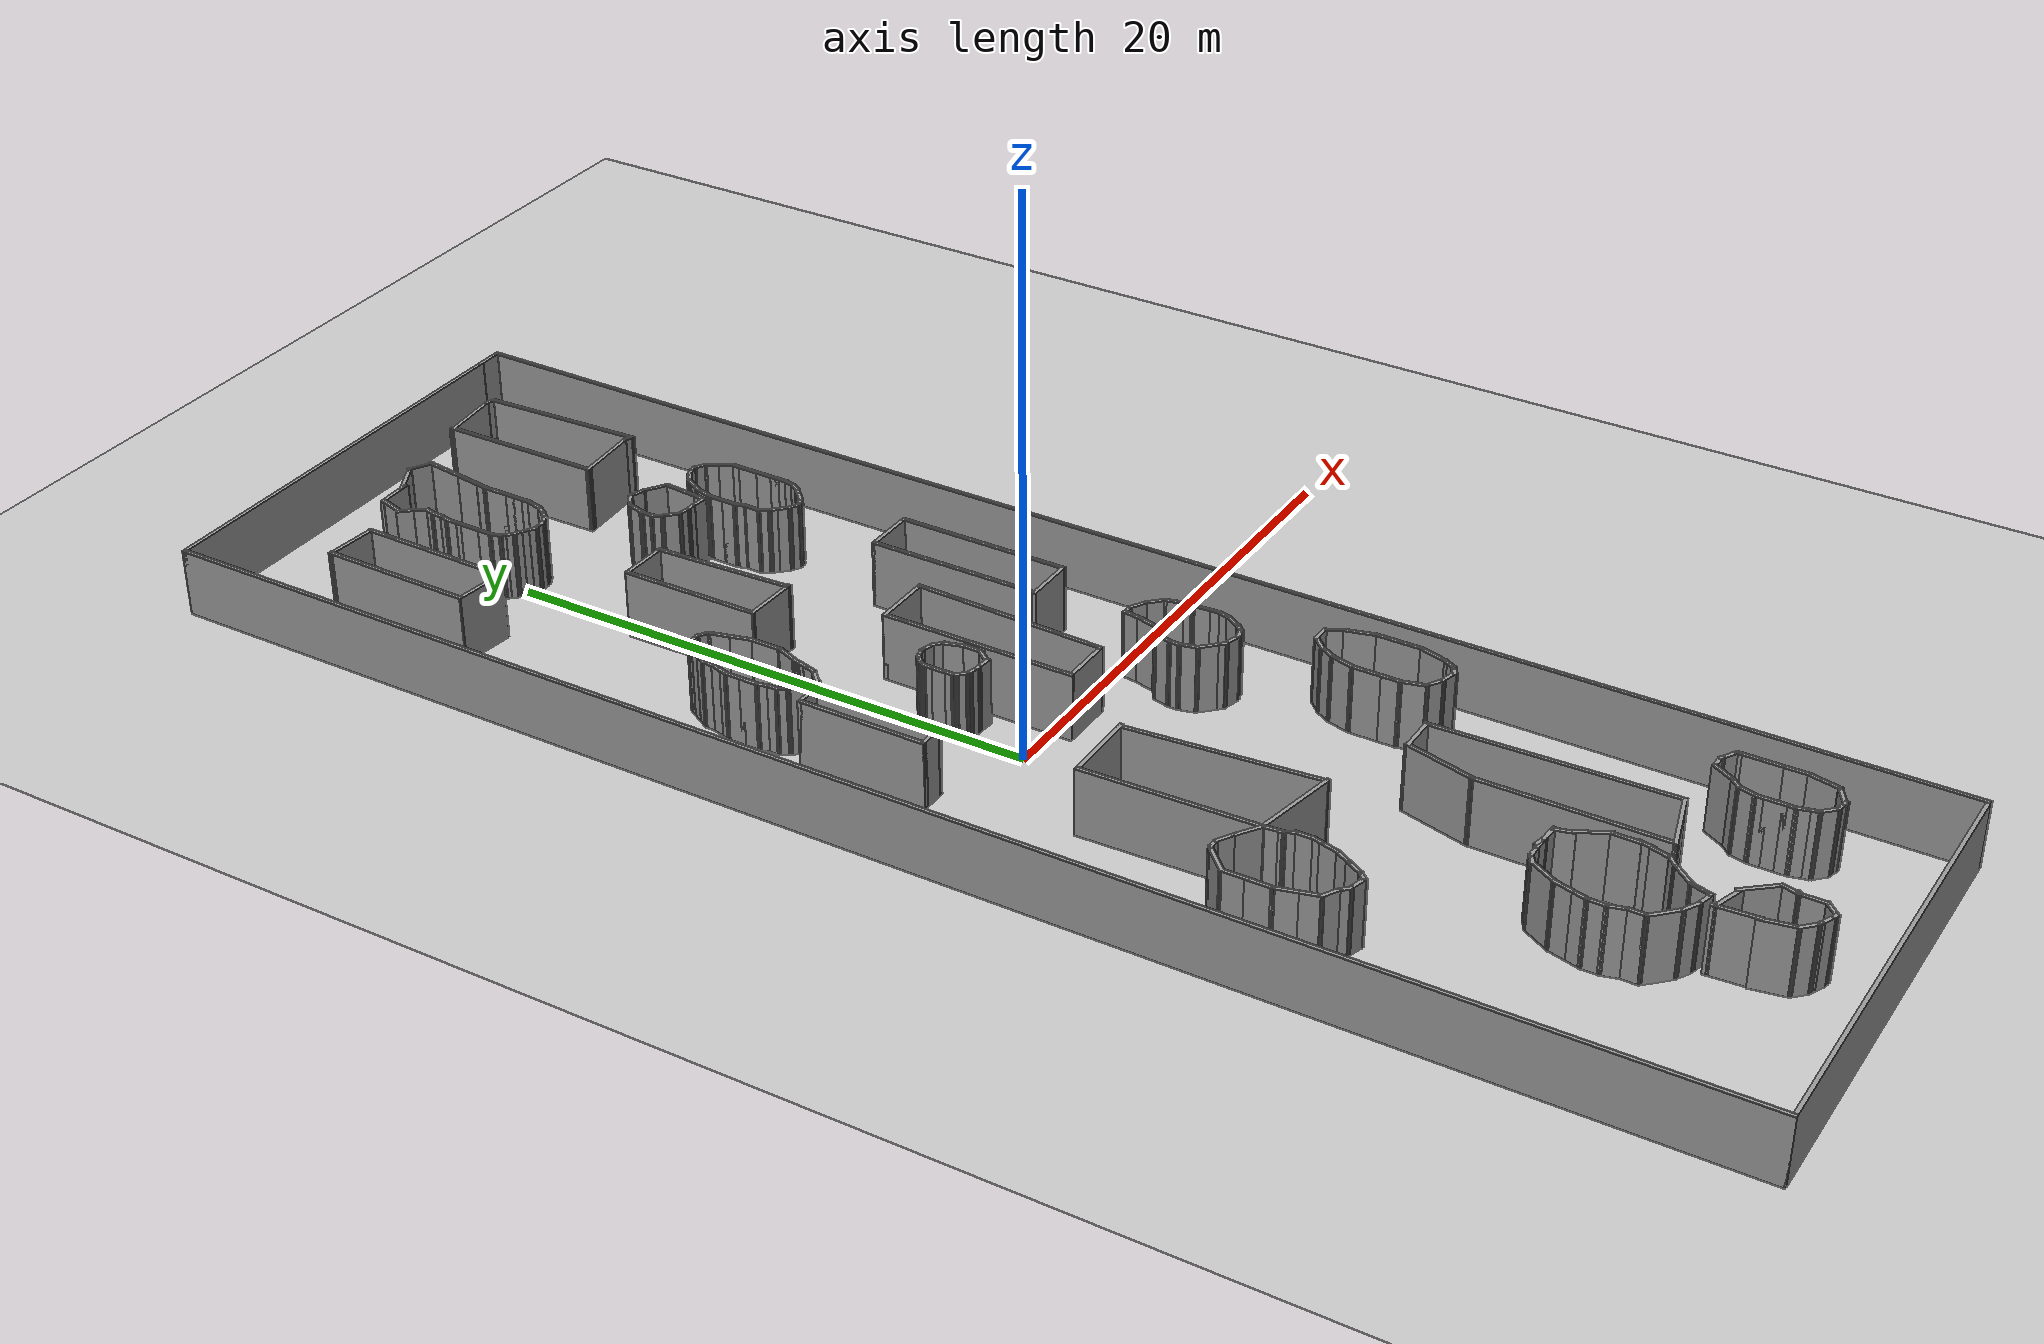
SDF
<sdf version="1.7">
 <world name="default">
  <light name="sun" type="directional">
   <pose>0 0 10 0 -0 0</pose>
   <diffuse>0.8 0.8 0.8 1</diffuse>
   <specular>0.2 0.2 0.2 1</specular>
   <attenuation>
    <range>1000</range>
    <constant>0.9</constant>
    <linear>0.01</linear>
    <quadratic>0.001</quadratic>
   </attenuation>
   <direction>-0.5 0.1 -0.9</direction>
   <spot><inner_angle>0</inner_angle><outer_angle>0</outer_angle><falloff>0</falloff></spot>
  </light>
  <model name="ground_plane">
   <static>1</static>
   <link name="link">
    <collision name="collision">
     <geometry><plane><normal>0 0 1</normal><size>100 100</size></plane></geometry>
     <surface><friction><ode><mu>100</mu><mu2>50</mu2></ode></friction></surface>
    </collision>
    <visual name="visual">
     <cast_shadows>0</cast_shadows>
     <geometry><plane><normal>0 0 1</normal><size>100 100</size></plane></geometry>
     <material>
      <script><uri>file://media/materials/scripts/gazebo.material</uri><name>Gazebo/Grey</name></script>
     </material>
    </visual>
   </link>
  </model>
  <gravity>0 0 -9.8</gravity>
  <magnetic_field>6e-06 2.3e-05 -4.2e-05</magnetic_field>
  <atmosphere type="adiabatic"/>
  <physics type="ode">
   <max_step_size>0.001</max_step_size>
   <real_time_factor>1</real_time_factor>
   <real_time_update_rate>1000</real_time_update_rate>
  </physics>
  <scene><ambient>0.4 0.4 0.4 1</ambient><background>0.7 0.7 0.7 1</background><shadows>1</shadows></scene>
  <spherical_coordinates>
   <surface_model>EARTH_WGS84</surface_model>
   <latitude_deg>0</latitude_deg>
   <longitude_deg>0</longitude_deg>
   <elevation>0</elevation>
   <heading_deg>0</heading_deg>
  </spherical_coordinates>
  <model name="complex_wall">
   <pose>1.5 0.5 0 0 0 -1.5708</pose>
   <link name="Wall_100">
    <collision name="Wall_100_Collision">
     <geometry><box><size>0.5 0.15 2.5</size></box></geometry>
     <pose>0 0 1.25 0 -0 0</pose>
    </collision>
    <visual name="Wall_100_Visual">
     <pose>0 0 1.25 0 -0 0</pose>
     <geometry><box><size>0.5 0.15 2.5</size></box></geometry>
     <material>
      <script><uri>file://media/materials/scripts/gazebo.material</uri><name>Gazebo/Grey</name></script>
      <ambient>1 1 1 1</ambient>
     </material>
     <meta><layer>0</layer></meta>
    </visual>
    <pose>-19.3948 -0.52786 0 0 -0 2.0944</pose>
   </link>
   <link name="Wall_101">
    <collision name="Wall_101_Collision">
     <geometry><box><size>0.5 0.15 2.5</size></box></geometry>
     <pose>0 0 1.25 0 -0 0</pose>
    </collision>
    <visual name="Wall_101_Visual">
     <pose>0 0 1.25 0 -0 0</pose>
     <geometry><box><size>0.5 0.15 2.5</size></box></geometry>
     <material>
      <script><uri>file://media/materials/scripts/gazebo.material</uri><name>Gazebo/Grey</name></script>
      <ambient>1 1 1 1</ambient>
     </material>
     <meta><layer>0</layer></meta>
    </visual>
    <pose>-19.606 -0.252562 0 0 -0 2.35619</pose>
   </link>
   <link name="Wall_102">
    <collision name="Wall_102_Collision">
     <geometry><box><size>0.5 0.15 2.5</size></box></geometry>
     <pose>0 0 1.25 0 -0 0</pose>
    </collision>
    <visual name="Wall_102_Visual">
     <pose>0 0 1.25 0 -0 0</pose>
     <geometry><box><size>0.5 0.15 2.5</size></box></geometry>
     <material>
      <script><uri>file://media/materials/scripts/gazebo.material</uri><name>Gazebo/Grey</name></script>
      <ambient>1 1 1 1</ambient>
     </material>
     <meta><layer>0</layer></meta>
    </visual>
    <pose>-19.8813 -0.041319 0 0 -0 2.61799</pose>
   </link>
   <link name="Wall_103">
    <collision name="Wall_103_Collision">
     <geometry><box><size>0.75 0.15 2.5</size></box></geometry>
     <pose>0 0 1.25 0 -0 0</pose>
    </collision>
    <visual name="Wall_103_Visual">
     <pose>0 0 1.25 0 -0 0</pose>
     <geometry><box><size>0.75 0.15 2.5</size></box></geometry>
     <material>
      <script><uri>file://media/materials/scripts/gazebo.material</uri><name>Gazebo/Grey</name></script>
      <ambient>1 1 1 1</ambient>
     </material>
     <meta><layer>0</layer></meta>
    </visual>
    <pose>-20.3227 0.123827 0 0 -0 2.87979</pose>
   </link>
   <link name="Wall_104">
    <collision name="Wall_104_Collision">
     <geometry><box><size>0.5 0.15 2.5</size></box></geometry>
     <pose>0 0 1.25 0 -0 0</pose>
    </collision>
    <visual name="Wall_104_Visual">
     <pose>0 0 1.25 0 -0 0</pose>
     <geometry><box><size>0.5 0.15 2.5</size></box></geometry>
     <material>
      <script><uri>file://media/materials/scripts/gazebo.material</uri><name>Gazebo/Grey</name></script>
      <ambient>1 1 1 1</ambient>
     </material>
     <meta><layer>0</layer></meta>
    </visual>
    <pose>-20.7874 0.201473 0 0 -0 3.14159</pose>
   </link>
   <link name="Wall_105">
    <collision name="Wall_105_Collision">
     <geometry><box><size>0.5 0.15 2.5</size></box></geometry>
     <pose>0 0 1.25 0 -0 0</pose>
    </collision>
    <visual name="Wall_105_Visual">
     <pose>0 0 1.25 0 -0 0</pose>
     <geometry><box><size>0.5 0.15 2.5</size></box></geometry>
     <material>
      <script><uri>file://media/materials/scripts/gazebo.material</uri><name>Gazebo/Grey</name></script>
      <ambient>1 1 1 1</ambient>
     </material>
     <meta><layer>0</layer></meta>
    </visual>
    <pose>-21.1374 0.201473 0 0 -0 3.14159</pose>
   </link>
   <link name="Wall_106">
    <collision name="Wall_106_Collision">
     <geometry><box><size>0.5 0.15 2.5</size></box></geometry>
     <pose>0 0 1.25 0 -0 0</pose>
    </collision>
    <visual name="Wall_106_Visual">
     <pose>0 0 1.25 0 -0 0</pose>
     <geometry><box><size>0.5 0.15 2.5</size></box></geometry>
     <material>
      <script><uri>file://media/materials/scripts/gazebo.material</uri><name>Gazebo/Grey</name></script>
      <ambient>1 1 1 1</ambient>
     </material>
     <meta><layer>0</layer></meta>
    </visual>
    <pose>-21.4874 0.201473 0 0 -0 3.14159</pose>
   </link>
   <link name="Wall_107">
    <collision name="Wall_107_Collision">
     <geometry><box><size>1 0.15 2.5</size></box></geometry>
     <pose>0 0 1.25 0 -0 0</pose>
    </collision>
    <visual name="Wall_107_Visual">
     <pose>0 0 1.25 0 -0 0</pose>
     <geometry><box><size>1 0.15 2.5</size></box></geometry>
     <material>
      <script><uri>file://media/materials/scripts/gazebo.material</uri><name>Gazebo/Grey</name></script>
      <ambient>1 1 1 1</ambient>
     </material>
     <meta><layer>0</layer></meta>
    </visual>
    <pose>-22.0874 0.201473 0 0 -0 3.14159</pose>
   </link>
   <link name="Wall_111">
    <collision name="Wall_111_Collision">
     <geometry><box><size>1.61529 0.15 2.5</size></box></geometry>
     <pose>0 0 1.25 0 -0 0</pose>
    </collision>
    <visual name="Wall_111_Visual">
     <pose>0 0 1.25 0 -0 0</pose>
     <geometry><box><size>1.61529 0.15 2.5</size></box></geometry>
     <material>
      <script><uri>file://media/materials/scripts/gazebo.material</uri><name>Gazebo/Grey</name></script>
      <ambient>1 1 1 1</ambient>
     </material>
     <meta><layer>0</layer></meta>
    </visual>
    <pose>-24.5927 0.497103 0 0 -0 3.00766</pose>
   </link>
   <link name="Wall_112">
    <collision name="Wall_112_Collision">
     <geometry><box><size>0.15 0.15 2.5</size></box></geometry>
     <pose>0 0 1.25 0 -0 0</pose>
    </collision>
    <visual name="Wall_112_Visual">
     <pose>0 0 1.25 0 -0 0</pose>
     <geometry><box><size>0.15 0.15 2.5</size></box></geometry>
     <material>
      <script><uri>file://media/materials/scripts/gazebo.material</uri><name>Gazebo/Grey</name></script>
      <ambient>1 1 1 1</ambient>
     </material>
     <meta><layer>0</layer></meta>
    </visual>
    <pose>-25.3187 0.594936 0 0 -0 0</pose>
   </link>
   <link name="Wall_113">
    <collision name="Wall_113_Collision">
     <geometry><box><size>1 0.15 2.5</size></box></geometry>
     <pose>0 0 1.25 0 -0 0</pose>
    </collision>
    <visual name="Wall_113_Visual">
     <pose>0 0 1.25 0 -0 0</pose>
     <geometry><box><size>1 0.15 2.5</size></box></geometry>
     <material>
      <script><uri>file://media/materials/scripts/gazebo.material</uri><name>Gazebo/Grey</name></script>
      <ambient>1 1 1 1</ambient>
     </material>
     <meta><layer>0</layer></meta>
    </visual>
    <pose>-25.4386 0.226876 0 0 -0 -2.0944</pose>
   </link>
   <link name="Wall_114">
    <collision name="Wall_114_Collision">
     <geometry><box><size>1.44528 0.15 2.5</size></box></geometry>
     <pose>0 0 1.25 0 -0 0</pose>
    </collision>
    <visual name="Wall_114_Visual">
     <pose>0 0 1.25 0 -0 0</pose>
     <geometry><box><size>1.44528 0.15 2.5</size></box></geometry>
     <material>
      <script><uri>file://media/materials/scripts/gazebo.material</uri><name>Gazebo/Grey</name></script>
      <ambient>1 1 1 1</ambient>
     </material>
     <meta><layer>0</layer></meta>
    </visual>
    <pose>-25.3438 -0.711293 0 0 -0 -1.07646</pose>
   </link>
   <link name="Wall_117">
    <collision name="Wall_117_Collision">
     <geometry><box><size>1.34808 0.15 2.5</size></box></geometry>
     <pose>0 0 1.25 0 -0 0</pose>
    </collision>
    <visual name="Wall_117_Visual">
     <pose>0 0 1.25 0 -0 0</pose>
     <geometry><box><size>1.34808 0.15 2.5</size></box></geometry>
     <material>
      <script><uri>file://media/materials/scripts/gazebo.material</uri><name>Gazebo/Grey</name></script>
      <ambient>1 1 1 1</ambient>
     </material>
     <meta><layer>0</layer></meta>
    </visual>
    <pose>-24.9902 -1.76917 0 0 -0 -1.55537</pose>
   </link>
   <link name="Wall_118">
    <collision name="Wall_118_Collision">
     <geometry><box><size>1.09701 0.15 2.5</size></box></geometry>
     <pose>0 0 1.25 0 -0 0</pose>
    </collision>
    <visual name="Wall_118_Visual">
     <pose>0 0 1.25 0 -0 0</pose>
     <geometry><box><size>1.09701 0.15 2.5</size></box></geometry>
     <material>
      <script><uri>file://media/materials/scripts/gazebo.material</uri><name>Gazebo/Grey</name></script>
      <ambient>1 1 1 1</ambient>
     </material>
     <meta><layer>0</layer></meta>
    </visual>
    <pose>-24.5284 -2.47011 0 0 -0 -0.298026</pose>
   </link>
   <link name="Wall_120">
    <collision name="Wall_120_Collision">
     <geometry><box><size>1.91735 0.15 2.5</size></box></geometry>
     <pose>0 0 1.25 0 -0 0</pose>
    </collision>
    <visual name="Wall_120_Visual">
     <pose>0 0 1.25 0 -0 0</pose>
     <geometry><box><size>1.91735 0.15 2.5</size></box></geometry>
     <material>
      <script><uri>file://media/materials/scripts/gazebo.material</uri><name>Gazebo/Grey</name></script>
      <ambient>1 1 1 1</ambient>
     </material>
     <meta><layer>0</layer></meta>
    </visual>
    <pose>-14.791 -0.964174 0 0 -0 -1.59854</pose>
   </link>
   <link name="Wall_121">
    <collision name="Wall_121_Collision">
     <geometry><box><size>5.20588 0.15 2.5</size></box></geometry>
     <pose>0 0 1.25 0 -0 0</pose>
    </collision>
    <visual name="Wall_121_Visual">
     <pose>0 0 1.25 0 -0 0</pose>
     <geometry><box><size>5.20588 0.15 2.5</size></box></geometry>
     <material>
      <script><uri>file://media/materials/scripts/gazebo.material</uri><name>Gazebo/Grey</name></script>
      <ambient>1 1 1 1</ambient>
     </material>
     <meta><layer>0</layer></meta>
    </visual>
    <pose>-12.2631 -1.84751 0 0 -0 0.009695</pose>
   </link>
   <link name="Wall_122">
    <collision name="Wall_122_Collision">
     <geometry><box><size>2.16727 0.15 2.5</size></box></geometry>
     <pose>0 0 1.25 0 -0 0</pose>
    </collision>
    <visual name="Wall_122_Visual">
     <pose>0 0 1.25 0 -0 0</pose>
     <geometry><box><size>2.16727 0.15 2.5</size></box></geometry>
     <material>
      <script><uri>file://media/materials/scripts/gazebo.material</uri><name>Gazebo/Grey</name></script>
      <ambient>1 1 1 1</ambient>
     </material>
     <meta><layer>0</layer></meta>
    </visual>
    <pose>-9.7106 -0.814664 0 0 -0 1.54649</pose>
   </link>
   <link name="Wall_123">
    <collision name="Wall_123_Collision">
     <geometry><box><size>5.21205 0.15 2.5</size></box></geometry>
     <pose>0 0 1.25 0 -0 0</pose>
    </collision>
    <visual name="Wall_123_Visual">
     <pose>0 0 1.25 0 -0 0</pose>
     <geometry><box><size>5.21205 0.15 2.5</size></box></geometry>
     <material>
      <script><uri>file://media/materials/scripts/gazebo.material</uri><name>Gazebo/Grey</name></script>
      <ambient>1 1 1 1</ambient>
     </material>
     <meta><layer>0</layer></meta>
    </visual>
    <pose>-12.214 0.019653 0 0 -0 -3.09219</pose>
   </link>
   <link name="Wall_129">
    <collision name="Wall_129_Collision">
     <geometry><box><size>0.25 0.15 2.5</size></box></geometry>
     <pose>0 0 1.25 0 -0 0</pose>
    </collision>
    <visual name="Wall_129_Visual">
     <pose>0 0 1.25 0 -0 0</pose>
     <geometry><box><size>0.25 0.15 2.5</size></box></geometry>
     <material>
      <script><uri>file://media/materials/scripts/gazebo.material</uri><name>Gazebo/Grey</name></script>
      <ambient>1 1 1 1</ambient>
     </material>
     <meta><layer>0</layer></meta>
    </visual>
    <pose>-17.8126 2.40032 0 0 -0 -1.5708</pose>
   </link>
   <link name="Wall_130">
    <collision name="Wall_130_Collision">
     <geometry><box><size>0.5 0.15 2.5</size></box></geometry>
     <pose>0 0 1.25 0 -0 0</pose>
    </collision>
    <visual name="Wall_130_Visual">
     <pose>0 0 1.25 0 -0 0</pose>
     <geometry><box><size>0.5 0.15 2.5</size></box></geometry>
     <material>
      <script><uri>file://media/materials/scripts/gazebo.material</uri><name>Gazebo/Grey</name></script>
      <ambient>1 1 1 1</ambient>
     </material>
     <meta><layer>0</layer></meta>
    </visual>
    <pose>-17.7251 2.19877 0 0 -0 -1.0472</pose>
   </link>
   <link name="Wall_131">
    <collision name="Wall_131_Collision">
     <geometry><box><size>0.5 0.15 2.5</size></box></geometry>
     <pose>0 0 1.25 0 -0 0</pose>
    </collision>
    <visual name="Wall_131_Visual">
     <pose>0 0 1.25 0 -0 0</pose>
     <geometry><box><size>0.5 0.15 2.5</size></box></geometry>
     <material>
      <script><uri>file://media/materials/scripts/gazebo.material</uri><name>Gazebo/Grey</name></script>
      <ambient>1 1 1 1</ambient>
     </material>
     <meta><layer>0</layer></meta>
    </visual>
    <pose>-17.5139 1.92347 0 0 -0 -0.785398</pose>
   </link>
   <link name="Wall_132">
    <collision name="Wall_132_Collision">
     <geometry><box><size>0.75 0.15 2.5</size></box></geometry>
     <pose>0 0 1.25 0 -0 0</pose>
    </collision>
    <visual name="Wall_132_Visual">
     <pose>0 0 1.25 0 -0 0</pose>
     <geometry><box><size>0.75 0.15 2.5</size></box></geometry>
     <material>
      <script><uri>file://media/materials/scripts/gazebo.material</uri><name>Gazebo/Grey</name></script>
      <ambient>1 1 1 1</ambient>
     </material>
     <meta><layer>0</layer></meta>
    </visual>
    <pose>-17.1003 1.72208 0 0 -0 -0.261799</pose>
   </link>
   <link name="Wall_133">
    <collision name="Wall_133_Collision">
     <geometry><box><size>0.25 0.15 2.5</size></box></geometry>
     <pose>0 0 1.25 0 -0 0</pose>
    </collision>
    <visual name="Wall_133_Visual">
     <pose>0 0 1.25 0 -0 0</pose>
     <geometry><box><size>0.25 0.15 2.5</size></box></geometry>
     <material>
      <script><uri>file://media/materials/scripts/gazebo.material</uri><name>Gazebo/Grey</name></script>
      <ambient>1 1 1 1</ambient>
     </material>
     <meta><layer>0</layer></meta>
    </visual>
    <pose>-16.7623 1.63149 0 0 -0 -0.261799</pose>
   </link>
   <link name="Wall_134">
    <collision name="Wall_134_Collision">
     <geometry><box><size>0.5 0.15 2.5</size></box></geometry>
     <pose>0 0 1.25 0 -0 0</pose>
    </collision>
    <visual name="Wall_134_Visual">
     <pose>0 0 1.25 0 -0 0</pose>
     <geometry><box><size>0.5 0.15 2.5</size></box></geometry>
     <material>
      <script><uri>file://media/materials/scripts/gazebo.material</uri><name>Gazebo/Grey</name></script>
      <ambient>1 1 1 1</ambient>
     </material>
     <meta><layer>0</layer></meta>
    </visual>
    <pose>-16.539 1.61855 0 0 -0 0</pose>
   </link>
   <link name="Wall_135">
    <collision name="Wall_135_Collision">
     <geometry><box><size>0.5 0.15 2.5</size></box></geometry>
     <pose>0 0 1.25 0 -0 0</pose>
    </collision>
    <visual name="Wall_135_Visual">
     <pose>0 0 1.25 0 -0 0</pose>
     <geometry><box><size>0.5 0.15 2.5</size></box></geometry>
     <material>
      <script><uri>file://media/materials/scripts/gazebo.material</uri><name>Gazebo/Grey</name></script>
      <ambient>1 1 1 1</ambient>
     </material>
     <meta><layer>0</layer></meta>
    </visual>
    <pose>-16.2124 1.70606 0 0 -0 0.523599</pose>
   </link>
   <link name="Wall_136">
    <collision name="Wall_136_Collision">
     <geometry><box><size>0.75 0.15 2.5</size></box></geometry>
     <pose>0 0 1.25 0 -0 0</pose>
    </collision>
    <visual name="Wall_136_Visual">
     <pose>0 0 1.25 0 -0 0</pose>
     <geometry><box><size>0.75 0.15 2.5</size></box></geometry>
     <material>
      <script><uri>file://media/materials/scripts/gazebo.material</uri><name>Gazebo/Grey</name></script>
      <ambient>1 1 1 1</ambient>
     </material>
     <meta><layer>0</layer></meta>
    </visual>
    <pose>-15.8487 2.00569 0 0 -0 0.785398</pose>
   </link>
   <link name="Wall_137">
    <collision name="Wall_137_Collision">
     <geometry><box><size>0.5 0.15 2.5</size></box></geometry>
     <pose>0 0 1.25 0 -0 0</pose>
    </collision>
    <visual name="Wall_137_Visual">
     <pose>0 0 1.25 0 -0 0</pose>
     <geometry><box><size>0.5 0.15 2.5</size></box></geometry>
     <material>
      <script><uri>file://media/materials/scripts/gazebo.material</uri><name>Gazebo/Grey</name></script>
      <ambient>1 1 1 1</ambient>
     </material>
     <meta><layer>0</layer></meta>
    </visual>
    <pose>-15.5913 2.38686 0 0 -0 1.309</pose>
   </link>
   <link name="Wall_138">
    <collision name="Wall_138_Collision">
     <geometry><box><size>0.5 0.15 2.5</size></box></geometry>
     <pose>0 0 1.25 0 -0 0</pose>
    </collision>
    <visual name="Wall_138_Visual">
     <pose>0 0 1.25 0 -0 0</pose>
     <geometry><box><size>0.5 0.15 2.5</size></box></geometry>
     <material>
      <script><uri>file://media/materials/scripts/gazebo.material</uri><name>Gazebo/Grey</name></script>
      <ambient>1 1 1 1</ambient>
     </material>
     <meta><layer>0</layer></meta>
    </visual>
    <pose>-15.546 2.73089 0 0 -0 1.5708</pose>
   </link>
   <link name="Wall_139">
    <collision name="Wall_139_Collision">
     <geometry><box><size>0.661181 0.15 2.5</size></box></geometry>
     <pose>0 0 1.25 0 -0 0</pose>
    </collision>
    <visual name="Wall_139_Visual">
     <pose>0 0 1.25 0 -0 0</pose>
     <geometry><box><size>0.661181 0.15 2.5</size></box></geometry>
     <material>
      <script><uri>file://media/materials/scripts/gazebo.material</uri><name>Gazebo/Grey</name></script>
      <ambient>1 1 1 1</ambient>
     </material>
     <meta><layer>0</layer></meta>
    </visual>
    <pose>-15.5203 3.16018 0 0 -0 1.46988</pose>
   </link>
   <link name="Wall_140">
    <collision name="Wall_140_Collision">
     <geometry><box><size>0.521727 0.15 2.5</size></box></geometry>
     <pose>0 0 1.25 0 -0 0</pose>
    </collision>
    <visual name="Wall_140_Visual">
     <pose>0 0 1.25 0 -0 0</pose>
     <geometry><box><size>0.521727 0.15 2.5</size></box></geometry>
     <material>
      <script><uri>file://media/materials/scripts/gazebo.material</uri><name>Gazebo/Grey</name></script>
      <ambient>1 1 1 1</ambient>
     </material>
     <meta><layer>0</layer></meta>
    </visual>
    <pose>-15.7062 3.47397 0 0 -0 2.97356</pose>
   </link>
   <link name="Wall_144">
    <collision name="Wall_144_Collision">
     <geometry><box><size>0.15 0.15 2.5</size></box></geometry>
     <pose>0 0 1.25 0 -0 0</pose>
    </collision>
    <visual name="Wall_144_Visual">
     <pose>0 0 1.25 0 -0 0</pose>
     <geometry><box><size>0.15 0.15 2.5</size></box></geometry>
     <material>
      <script><uri>file://media/materials/scripts/gazebo.material</uri><name>Gazebo/Grey</name></script>
      <ambient>1 1 1 1</ambient>
     </material>
     <meta><layer>0</layer></meta>
    </visual>
    <pose>-17.1676 3.6136 0 0 -0 0</pose>
   </link>
   <link name="Wall_148">
    <collision name="Wall_148_Collision">
     <geometry><box><size>2.29146 0.15 2.5</size></box></geometry>
     <pose>0 0 1.25 0 -0 0</pose>
    </collision>
    <visual name="Wall_148_Visual">
     <pose>0 0 1.25 0 -0 0</pose>
     <geometry><box><size>2.29146 0.15 2.5</size></box></geometry>
     <material>
      <script><uri>file://media/materials/scripts/gazebo.material</uri><name>Gazebo/Grey</name></script>
      <ambient>1 1 1 1</ambient>
     </material>
     <meta><layer>0</layer></meta>
    </visual>
    <pose>-26.3129 4.07044 0 0 -0 -1.46971</pose>
   </link>
   <link name="Wall_149">
    <collision name="Wall_149_Collision">
     <geometry><box><size>6.21671 0.15 2.5</size></box></geometry>
     <pose>0 0 1.25 0 -0 0</pose>
    </collision>
    <visual name="Wall_149_Visual">
     <pose>0 0 1.25 0 -0 0</pose>
     <geometry><box><size>6.21671 0.15 2.5</size></box></geometry>
     <material>
      <script><uri>file://media/materials/scripts/gazebo.material</uri><name>Gazebo/Grey</name></script>
      <ambient>1 1 1 1</ambient>
     </material>
     <meta><layer>0</layer></meta>
    </visual>
    <pose>-23.2582 3.04839 0 0 -0 0.014249</pose>
   </link>
   <link name="Wall_150">
    <collision name="Wall_150_Collision">
     <geometry><box><size>2.51228 0.15 2.5</size></box></geometry>
     <pose>0 0 1.25 0 -0 0</pose>
    </collision>
    <visual name="Wall_150_Visual">
     <pose>0 0 1.25 0 -0 0</pose>
     <geometry><box><size>2.51228 0.15 2.5</size></box></geometry>
     <material>
      <script><uri>file://media/materials/scripts/gazebo.material</uri><name>Gazebo/Grey</name></script>
      <ambient>1 1 1 1</ambient>
     </material>
     <meta><layer>0</layer></meta>
    </visual>
    <pose>-20.3116 4.26959 0 0 -0 1.64404</pose>
   </link>
   <link name="Wall_151">
    <collision name="Wall_151_Collision">
     <geometry><box><size>6.18095 0.15 2.5</size></box></geometry>
     <pose>0 0 1.25 0 -0 0</pose>
    </collision>
    <visual name="Wall_151_Visual">
     <pose>0 0 1.25 0 -0 0</pose>
     <geometry><box><size>6.18095 0.15 2.5</size></box></geometry>
     <material>
      <script><uri>file://media/materials/scripts/gazebo.material</uri><name>Gazebo/Grey</name></script>
      <ambient>1 1 1 1</ambient>
     </material>
     <meta><layer>0</layer></meta>
    </visual>
    <pose>-23.3231 5.59417 0 0 -0 -3.08986</pose>
   </link>
   <link name="Wall_153">
    <collision name="Wall_153_Collision">
     <geometry><box><size>0.5 0.15 2.5</size></box></geometry>
     <pose>0 0 1.25 0 -0 0</pose>
    </collision>
    <visual name="Wall_153_Visual">
     <pose>0 0 1.25 0 -0 0</pose>
     <geometry><box><size>0.5 0.15 2.5</size></box></geometry>
     <material>
      <script><uri>file://media/materials/scripts/gazebo.material</uri><name>Gazebo/Grey</name></script>
      <ambient>1 1 1 1</ambient>
     </material>
     <meta><layer>0</layer></meta>
    </visual>
    <pose>-16.5234 4.17445 0 0 -0 -0.523599</pose>
   </link>
   <link name="Wall_154">
    <collision name="Wall_154_Collision">
     <geometry><box><size>0.5 0.15 2.5</size></box></geometry>
     <pose>0 0 1.25 0 -0 0</pose>
    </collision>
    <visual name="Wall_154_Visual">
     <pose>0 0 1.25 0 -0 0</pose>
     <geometry><box><size>0.5 0.15 2.5</size></box></geometry>
     <material>
      <script><uri>file://media/materials/scripts/gazebo.material</uri><name>Gazebo/Grey</name></script>
      <ambient>1 1 1 1</ambient>
     </material>
     <meta><layer>0</layer></meta>
    </visual>
    <pose>-16.2203 3.99945 0 0 -0 -0.523599</pose>
   </link>
   <link name="Wall_155">
    <collision name="Wall_155_Collision">
     <geometry><box><size>0.75 0.15 2.5</size></box></geometry>
     <pose>0 0 1.25 0 -0 0</pose>
    </collision>
    <visual name="Wall_155_Visual">
     <pose>0 0 1.25 0 -0 0</pose>
     <geometry><box><size>0.75 0.15 2.5</size></box></geometry>
     <material>
      <script><uri>file://media/materials/scripts/gazebo.material</uri><name>Gazebo/Grey</name></script>
      <ambient>1 1 1 1</ambient>
     </material>
     <meta><layer>0</layer></meta>
    </visual>
    <pose>-15.7789 3.83431 0 0 -0 -0.261799</pose>
   </link>
   <link name="Wall_156">
    <collision name="Wall_156_Collision">
     <geometry><box><size>0.25 0.15 2.5</size></box></geometry>
     <pose>0 0 1.25 0 -0 0</pose>
    </collision>
    <visual name="Wall_156_Visual">
     <pose>0 0 1.25 0 -0 0</pose>
     <geometry><box><size>0.25 0.15 2.5</size></box></geometry>
     <material>
      <script><uri>file://media/materials/scripts/gazebo.material</uri><name>Gazebo/Grey</name></script>
      <ambient>1 1 1 1</ambient>
     </material>
     <meta><layer>0</layer></meta>
    </visual>
    <pose>-15.4408 3.74372 0 0 -0 -0.261799</pose>
   </link>
   <link name="Wall_157">
    <collision name="Wall_157_Collision">
     <geometry><box><size>0.75 0.15 2.5</size></box></geometry>
     <pose>0 0 1.25 0 -0 0</pose>
    </collision>
    <visual name="Wall_157_Visual">
     <pose>0 0 1.25 0 -0 0</pose>
     <geometry><box><size>0.75 0.15 2.5</size></box></geometry>
     <material>
      <script><uri>file://media/materials/scripts/gazebo.material</uri><name>Gazebo/Grey</name></script>
      <ambient>1 1 1 1</ambient>
     </material>
     <meta><layer>0</layer></meta>
    </visual>
    <pose>-15.0926 3.73078 0 0 -0 0</pose>
   </link>
   <link name="Wall_158">
    <collision name="Wall_158_Collision">
     <geometry><box><size>0.5 0.15 2.5</size></box></geometry>
     <pose>0 0 1.25 0 -0 0</pose>
    </collision>
    <visual name="Wall_158_Visual">
     <pose>0 0 1.25 0 -0 0</pose>
     <geometry><box><size>0.5 0.15 2.5</size></box></geometry>
     <material>
      <script><uri>file://media/materials/scripts/gazebo.material</uri><name>Gazebo/Grey</name></script>
      <ambient>1 1 1 1</ambient>
     </material>
     <meta><layer>0</layer></meta>
    </visual>
    <pose>-14.6176 3.73078 0 0 -0 0</pose>
   </link>
   <link name="Wall_159">
    <collision name="Wall_159_Collision">
     <geometry><box><size>0.25 0.15 2.5</size></box></geometry>
     <pose>0 0 1.25 0 -0 0</pose>
    </collision>
    <visual name="Wall_159_Visual">
     <pose>0 0 1.25 0 -0 0</pose>
     <geometry><box><size>0.25 0.15 2.5</size></box></geometry>
     <material>
      <script><uri>file://media/materials/scripts/gazebo.material</uri><name>Gazebo/Grey</name></script>
      <ambient>1 1 1 1</ambient>
     </material>
     <meta><layer>0</layer></meta>
    </visual>
    <pose>-14.3926 3.73078 0 0 -0 0</pose>
   </link>
   <link name="Wall_160">
    <collision name="Wall_160_Collision">
     <geometry><box><size>0.5 0.15 2.5</size></box></geometry>
     <pose>0 0 1.25 0 -0 0</pose>
    </collision>
    <visual name="Wall_160_Visual">
     <pose>0 0 1.25 0 -0 0</pose>
     <geometry><box><size>0.5 0.15 2.5</size></box></geometry>
     <material>
      <script><uri>file://media/materials/scripts/gazebo.material</uri><name>Gazebo/Grey</name></script>
      <ambient>1 1 1 1</ambient>
     </material>
     <meta><layer>0</layer></meta>
    </visual>
    <pose>-14.1735 3.77607 0 0 -0 0.261799</pose>
   </link>
   <link name="Wall_161">
    <collision name="Wall_161_Collision">
     <geometry><box><size>0.15 0.15 2.5</size></box></geometry>
     <pose>0 0 1.25 0 -0 0</pose>
    </collision>
    <visual name="Wall_161_Visual">
     <pose>0 0 1.25 0 -0 0</pose>
     <geometry><box><size>0.15 0.15 2.5</size></box></geometry>
     <material>
      <script><uri>file://media/materials/scripts/gazebo.material</uri><name>Gazebo/Grey</name></script>
      <ambient>1 1 1 1</ambient>
     </material>
     <meta><layer>0</layer></meta>
    </visual>
    <pose>-14.0045 3.82137 0 0 -0 0</pose>
   </link>
   <link name="Wall_162">
    <collision name="Wall_162_Collision">
     <geometry><box><size>0.75 0.15 2.5</size></box></geometry>
     <pose>0 0 1.25 0 -0 0</pose>
    </collision>
    <visual name="Wall_162_Visual">
     <pose>0 0 1.25 0 -0 0</pose>
     <geometry><box><size>0.75 0.15 2.5</size></box></geometry>
     <material>
      <script><uri>file://media/materials/scripts/gazebo.material</uri><name>Gazebo/Grey</name></script>
      <ambient>1 1 1 1</ambient>
     </material>
     <meta><layer>0</layer></meta>
    </visual>
    <pose>-13.7045 3.82137 0 0 -0 0</pose>
   </link>
   <link name="Wall_163">
    <collision name="Wall_163_Collision">
     <geometry><box><size>0.5 0.15 2.5</size></box></geometry>
     <pose>0 0 1.25 0 -0 0</pose>
    </collision>
    <visual name="Wall_163_Visual">
     <pose>0 0 1.25 0 -0 0</pose>
     <geometry><box><size>0.5 0.15 2.5</size></box></geometry>
     <material>
      <script><uri>file://media/materials/scripts/gazebo.material</uri><name>Gazebo/Grey</name></script>
      <ambient>1 1 1 1</ambient>
     </material>
     <meta><layer>0</layer></meta>
    </visual>
    <pose>-13.2529 3.90887 0 0 -0 0.523599</pose>
   </link>
   <link name="Wall_164">
    <collision name="Wall_164_Collision">
     <geometry><box><size>0.5 0.15 2.5</size></box></geometry>
     <pose>0 0 1.25 0 -0 0</pose>
    </collision>
    <visual name="Wall_164_Visual">
     <pose>0 0 1.25 0 -0 0</pose>
     <geometry><box><size>0.5 0.15 2.5</size></box></geometry>
     <material>
      <script><uri>file://media/materials/scripts/gazebo.material</uri><name>Gazebo/Grey</name></script>
      <ambient>1 1 1 1</ambient>
     </material>
     <meta><layer>0</layer></meta>
    </visual>
    <pose>-12.9776 4.12011 0 0 -0 0.785398</pose>
   </link>
   <link name="Wall_165">
    <collision name="Wall_165_Collision">
     <geometry><box><size>0.5 0.15 2.5</size></box></geometry>
     <pose>0 0 1.25 0 -0 0</pose>
    </collision>
    <visual name="Wall_165_Visual">
     <pose>0 0 1.25 0 -0 0</pose>
     <geometry><box><size>0.5 0.15 2.5</size></box></geometry>
     <material>
      <script><uri>file://media/materials/scripts/gazebo.material</uri><name>Gazebo/Grey</name></script>
      <ambient>1 1 1 1</ambient>
     </material>
     <meta><layer>0</layer></meta>
    </visual>
    <pose>-12.7301 4.3676 0 0 -0 0.785398</pose>
   </link>
   <link name="Wall_166">
    <collision name="Wall_166_Collision">
     <geometry><box><size>0.5 0.15 2.5</size></box></geometry>
     <pose>0 0 1.25 0 -0 0</pose>
    </collision>
    <visual name="Wall_166_Visual">
     <pose>0 0 1.25 0 -0 0</pose>
     <geometry><box><size>0.5 0.15 2.5</size></box></geometry>
     <material>
      <script><uri>file://media/materials/scripts/gazebo.material</uri><name>Gazebo/Grey</name></script>
      <ambient>1 1 1 1</ambient>
     </material>
     <meta><layer>0</layer></meta>
    </visual>
    <pose>-12.5189 4.6429 0 0 -0 1.0472</pose>
   </link>
   <link name="Wall_167">
    <collision name="Wall_167_Collision">
     <geometry><box><size>0.25 0.15 2.5</size></box></geometry>
     <pose>0 0 1.25 0 -0 0</pose>
    </collision>
    <visual name="Wall_167_Visual">
     <pose>0 0 1.25 0 -0 0</pose>
     <geometry><box><size>0.25 0.15 2.5</size></box></geometry>
     <material>
      <script><uri>file://media/materials/scripts/gazebo.material</uri><name>Gazebo/Grey</name></script>
      <ambient>1 1 1 1</ambient>
     </material>
     <meta><layer>0</layer></meta>
    </visual>
    <pose>-12.4314 4.84445 0 0 -0 1.5708</pose>
   </link>
   <link name="Wall_168">
    <collision name="Wall_168_Collision">
     <geometry><box><size>0.5 0.15 2.5</size></box></geometry>
     <pose>0 0 1.25 0 -0 0</pose>
    </collision>
    <visual name="Wall_168_Visual">
     <pose>0 0 1.25 0 -0 0</pose>
     <geometry><box><size>0.5 0.15 2.5</size></box></geometry>
     <material>
      <script><uri>file://media/materials/scripts/gazebo.material</uri><name>Gazebo/Grey</name></script>
      <ambient>1 1 1 1</ambient>
     </material>
     <meta><layer>0</layer></meta>
    </visual>
    <pose>-12.5189 5.04601 0 0 -0 2.0944</pose>
   </link>
   <link name="Wall_169">
    <collision name="Wall_169_Collision">
     <geometry><box><size>0.5 0.15 2.5</size></box></geometry>
     <pose>0 0 1.25 0 -0 0</pose>
    </collision>
    <visual name="Wall_169_Visual">
     <pose>0 0 1.25 0 -0 0</pose>
     <geometry><box><size>0.5 0.15 2.5</size></box></geometry>
     <material>
      <script><uri>file://media/materials/scripts/gazebo.material</uri><name>Gazebo/Grey</name></script>
      <ambient>1 1 1 1</ambient>
     </material>
     <meta><layer>0</layer></meta>
    </visual>
    <pose>-12.7301 5.3213 0 0 -0 2.35619</pose>
   </link>
   <link name="Wall_170">
    <collision name="Wall_170_Collision">
     <geometry><box><size>0.5 0.15 2.5</size></box></geometry>
     <pose>0 0 1.25 0 -0 0</pose>
    </collision>
    <visual name="Wall_170_Visual">
     <pose>0 0 1.25 0 -0 0</pose>
     <geometry><box><size>0.5 0.15 2.5</size></box></geometry>
     <material>
      <script><uri>file://media/materials/scripts/gazebo.material</uri><name>Gazebo/Grey</name></script>
      <ambient>1 1 1 1</ambient>
     </material>
     <meta><layer>0</layer></meta>
    </visual>
    <pose>-12.9776 5.56879 0 0 -0 2.35619</pose>
   </link>
   <link name="Wall_171">
    <collision name="Wall_171_Collision">
     <geometry><box><size>0.5 0.15 2.5</size></box></geometry>
     <pose>0 0 1.25 0 -0 0</pose>
    </collision>
    <visual name="Wall_171_Visual">
     <pose>0 0 1.25 0 -0 0</pose>
     <geometry><box><size>0.5 0.15 2.5</size></box></geometry>
     <material>
      <script><uri>file://media/materials/scripts/gazebo.material</uri><name>Gazebo/Grey</name></script>
      <ambient>1 1 1 1</ambient>
     </material>
     <meta><layer>0</layer></meta>
    </visual>
    <pose>-13.2529 5.78003 0 0 -0 2.61799</pose>
   </link>
   <link name="Wall_172">
    <collision name="Wall_172_Collision">
     <geometry><box><size>0.5 0.15 2.5</size></box></geometry>
     <pose>0 0 1.25 0 -0 0</pose>
    </collision>
    <visual name="Wall_172_Visual">
     <pose>0 0 1.25 0 -0 0</pose>
     <geometry><box><size>0.5 0.15 2.5</size></box></geometry>
     <material>
      <script><uri>file://media/materials/scripts/gazebo.material</uri><name>Gazebo/Grey</name></script>
      <ambient>1 1 1 1</ambient>
     </material>
     <meta><layer>0</layer></meta>
    </visual>
    <pose>-13.5735 5.91283 0 0 -0 2.87979</pose>
   </link>
   <link name="Wall_173">
    <collision name="Wall_173_Collision">
     <geometry><box><size>0.5 0.15 2.5</size></box></geometry>
     <pose>0 0 1.25 0 -0 0</pose>
    </collision>
    <visual name="Wall_173_Visual">
     <pose>0 0 1.25 0 -0 0</pose>
     <geometry><box><size>0.5 0.15 2.5</size></box></geometry>
     <material>
      <script><uri>file://media/materials/scripts/gazebo.material</uri><name>Gazebo/Grey</name></script>
      <ambient>1 1 1 1</ambient>
     </material>
     <meta><layer>0</layer></meta>
    </visual>
    <pose>-13.9176 5.95812 0 0 -0 3.14159</pose>
   </link>
   <link name="Wall_174">
    <collision name="Wall_174_Collision">
     <geometry><box><size>0.5 0.15 2.5</size></box></geometry>
     <pose>0 0 1.25 0 -0 0</pose>
    </collision>
    <visual name="Wall_174_Visual">
     <pose>0 0 1.25 0 -0 0</pose>
     <geometry><box><size>0.5 0.15 2.5</size></box></geometry>
     <material>
      <script><uri>file://media/materials/scripts/gazebo.material</uri><name>Gazebo/Grey</name></script>
      <ambient>1 1 1 1</ambient>
     </material>
     <meta><layer>0</layer></meta>
    </visual>
    <pose>-14.2676 5.95812 0 0 -0 3.14159</pose>
   </link>
   <link name="Wall_175">
    <collision name="Wall_175_Collision">
     <geometry><box><size>0.75 0.15 2.5</size></box></geometry>
     <pose>0 0 1.25 0 -0 0</pose>
    </collision>
    <visual name="Wall_175_Visual">
     <pose>0 0 1.25 0 -0 0</pose>
     <geometry><box><size>0.75 0.15 2.5</size></box></geometry>
     <material>
      <script><uri>file://media/materials/scripts/gazebo.material</uri><name>Gazebo/Grey</name></script>
      <ambient>1 1 1 1</ambient>
     </material>
     <meta><layer>0</layer></meta>
    </visual>
    <pose>-14.7426 5.95812 0 0 -0 3.14159</pose>
   </link>
   <link name="Wall_176">
    <collision name="Wall_176_Collision">
     <geometry><box><size>0.75 0.15 2.5</size></box></geometry>
     <pose>0 0 1.25 0 -0 0</pose>
    </collision>
    <visual name="Wall_176_Visual">
     <pose>0 0 1.25 0 -0 0</pose>
     <geometry><box><size>0.75 0.15 2.5</size></box></geometry>
     <material>
      <script><uri>file://media/materials/scripts/gazebo.material</uri><name>Gazebo/Grey</name></script>
      <ambient>1 1 1 1</ambient>
     </material>
     <meta><layer>0</layer></meta>
    </visual>
    <pose>-15.3426 5.95812 0 0 -0 3.14159</pose>
   </link>
   <link name="Wall_177">
    <collision name="Wall_177_Collision">
     <geometry><box><size>0.5 0.15 2.5</size></box></geometry>
     <pose>0 0 1.25 0 -0 0</pose>
    </collision>
    <visual name="Wall_177_Visual">
     <pose>0 0 1.25 0 -0 0</pose>
     <geometry><box><size>0.5 0.15 2.5</size></box></geometry>
     <material>
      <script><uri>file://media/materials/scripts/gazebo.material</uri><name>Gazebo/Grey</name></script>
      <ambient>1 1 1 1</ambient>
     </material>
     <meta><layer>0</layer></meta>
    </visual>
    <pose>-15.8176 5.95812 0 0 -0 3.14159</pose>
   </link>
   <link name="Wall_178">
    <collision name="Wall_178_Collision">
     <geometry><box><size>0.75 0.15 2.5</size></box></geometry>
     <pose>0 0 1.25 0 -0 0</pose>
    </collision>
    <visual name="Wall_178_Visual">
     <pose>0 0 1.25 0 -0 0</pose>
     <geometry><box><size>0.75 0.15 2.5</size></box></geometry>
     <material>
      <script><uri>file://media/materials/scripts/gazebo.material</uri><name>Gazebo/Grey</name></script>
      <ambient>1 1 1 1</ambient>
     </material>
     <meta><layer>0</layer></meta>
    </visual>
    <pose>-16.2524 5.80812 0 0 -0 -2.61799</pose>
   </link>
   <link name="Wall_179">
    <collision name="Wall_179_Collision">
     <geometry><box><size>0.5 0.15 2.5</size></box></geometry>
     <pose>0 0 1.25 0 -0 0</pose>
    </collision>
    <visual name="Wall_179_Visual">
     <pose>0 0 1.25 0 -0 0</pose>
     <geometry><box><size>0.5 0.15 2.5</size></box></geometry>
     <material>
      <script><uri>file://media/materials/scripts/gazebo.material</uri><name>Gazebo/Grey</name></script>
      <ambient>1 1 1 1</ambient>
     </material>
     <meta><layer>0</layer></meta>
    </visual>
    <pose>-16.6637 5.57062 0 0 -0 -2.61799</pose>
   </link>
   <link name="Wall_180">
    <collision name="Wall_180_Collision">
     <geometry><box><size>0.25 0.15 2.5</size></box></geometry>
     <pose>0 0 1.25 0 -0 0</pose>
    </collision>
    <visual name="Wall_180_Visual">
     <pose>0 0 1.25 0 -0 0</pose>
     <geometry><box><size>0.25 0.15 2.5</size></box></geometry>
     <material>
      <script><uri>file://media/materials/scripts/gazebo.material</uri><name>Gazebo/Grey</name></script>
      <ambient>1 1 1 1</ambient>
     </material>
     <meta><layer>0</layer></meta>
    </visual>
    <pose>-16.8506 5.44777 0 0 -0 -2.35619</pose>
   </link>
   <link name="Wall_181">
    <collision name="Wall_181_Collision">
     <geometry><box><size>0.5 0.15 2.5</size></box></geometry>
     <pose>0 0 1.25 0 -0 0</pose>
    </collision>
    <visual name="Wall_181_Visual">
     <pose>0 0 1.25 0 -0 0</pose>
     <geometry><box><size>0.5 0.15 2.5</size></box></geometry>
     <material>
      <script><uri>file://media/materials/scripts/gazebo.material</uri><name>Gazebo/Grey</name></script>
      <ambient>1 1 1 1</ambient>
     </material>
     <meta><layer>0</layer></meta>
    </visual>
    <pose>-16.9735 5.26086 0 0 -0 -2.0944</pose>
   </link>
   <link name="Wall_182">
    <collision name="Wall_182_Collision">
     <geometry><box><size>0.15 0.15 2.5</size></box></geometry>
     <pose>0 0 1.25 0 -0 0</pose>
    </collision>
    <visual name="Wall_182_Visual">
     <pose>0 0 1.25 0 -0 0</pose>
     <geometry><box><size>0.15 0.15 2.5</size></box></geometry>
     <material>
      <script><uri>file://media/materials/scripts/gazebo.material</uri><name>Gazebo/Grey</name></script>
      <ambient>1 1 1 1</ambient>
     </material>
     <meta><layer>0</layer></meta>
    </visual>
    <pose>-17.061 5.1093 0 0 -0 0</pose>
   </link>
   <link name="Wall_183">
    <collision name="Wall_183_Collision">
     <geometry><box><size>0.25 0.15 2.5</size></box></geometry>
     <pose>0 0 1.25 0 -0 0</pose>
    </collision>
    <visual name="Wall_183_Visual">
     <pose>0 0 1.25 0 -0 0</pose>
     <geometry><box><size>0.25 0.15 2.5</size></box></geometry>
     <material>
      <script><uri>file://media/materials/scripts/gazebo.material</uri><name>Gazebo/Grey</name></script>
      <ambient>1 1 1 1</ambient>
     </material>
     <meta><layer>0</layer></meta>
    </visual>
    <pose>-17.061 5.0593 0 0 -0 -1.5708</pose>
   </link>
   <link name="Wall_184">
    <collision name="Wall_184_Collision">
     <geometry><box><size>0.5 0.15 2.5</size></box></geometry>
     <pose>0 0 1.25 0 -0 0</pose>
    </collision>
    <visual name="Wall_184_Visual">
     <pose>0 0 1.25 0 -0 0</pose>
     <geometry><box><size>0.5 0.15 2.5</size></box></geometry>
     <material>
      <script><uri>file://media/materials/scripts/gazebo.material</uri><name>Gazebo/Grey</name></script>
      <ambient>1 1 1 1</ambient>
     </material>
     <meta><layer>0</layer></meta>
    </visual>
    <pose>-17.0157 4.84026 0 0 -0 -1.309</pose>
   </link>
   <link name="Wall_185">
    <collision name="Wall_185_Collision">
     <geometry><box><size>0.654792 0.15 2.5</size></box></geometry>
     <pose>0 0 1.25 0 -0 0</pose>
    </collision>
    <visual name="Wall_185_Visual">
     <pose>0 0 1.25 0 -0 0</pose>
     <geometry><box><size>0.654792 0.15 2.5</size></box></geometry>
     <material>
      <script><uri>file://media/materials/scripts/gazebo.material</uri><name>Gazebo/Grey</name></script>
      <ambient>1 1 1 1</ambient>
     </material>
     <meta><layer>0</layer></meta>
    </visual>
    <pose>-16.8227 4.46659 0 0 -0 -0.945479</pose>
   </link>
   <link name="Wall_187">
    <collision name="Wall_187_Collision">
     <geometry><box><size>2 0.15 2.5</size></box></geometry>
     <pose>0 0 1.25 0 -0 0</pose>
    </collision>
    <visual name="Wall_187_Visual">
     <pose>0 0 1.25 0 -0 0</pose>
     <geometry><box><size>2 0.15 2.5</size></box></geometry>
     <material>
      <script><uri>file://media/materials/scripts/gazebo.material</uri><name>Gazebo/Grey</name></script>
      <ambient>1 1 1 1</ambient>
     </material>
     <meta><layer>0</layer></meta>
    </visual>
    <pose>-8.7492 4.94555 0 0 -0 -1.5708</pose>
   </link>
   <link name="Wall_188">
    <collision name="Wall_188_Collision">
     <geometry><box><size>6.5 0.15 2.5</size></box></geometry>
     <pose>0 0 1.25 0 -0 0</pose>
    </collision>
    <visual name="Wall_188_Visual">
     <pose>0 0 1.25 0 -0 0</pose>
     <geometry><box><size>6.5 0.15 2.5</size></box></geometry>
     <material>
      <script><uri>file://media/materials/scripts/gazebo.material</uri><name>Gazebo/Grey</name></script>
      <ambient>1 1 1 1</ambient>
     </material>
     <meta><layer>0</layer></meta>
    </visual>
    <pose>-5.5742 4.02055 0 0 -0 0</pose>
   </link>
   <link name="Wall_189">
    <collision name="Wall_189_Collision">
     <geometry><box><size>2 0.15 2.5</size></box></geometry>
     <pose>0 0 1.25 0 -0 0</pose>
    </collision>
    <visual name="Wall_189_Visual">
     <pose>0 0 1.25 0 -0 0</pose>
     <geometry><box><size>2 0.15 2.5</size></box></geometry>
     <material>
      <script><uri>file://media/materials/scripts/gazebo.material</uri><name>Gazebo/Grey</name></script>
      <ambient>1 1 1 1</ambient>
     </material>
     <meta><layer>0</layer></meta>
    </visual>
    <pose>-2.3992 4.94555 0 0 -0 1.5708</pose>
   </link>
   <link name="Wall_190">
    <collision name="Wall_190_Collision">
     <geometry><box><size>6.5 0.15 2.5</size></box></geometry>
     <pose>0 0 1.25 0 -0 0</pose>
    </collision>
    <visual name="Wall_190_Visual">
     <pose>0 0 1.25 0 -0 0</pose>
     <geometry><box><size>6.5 0.15 2.5</size></box></geometry>
     <material>
      <script><uri>file://media/materials/scripts/gazebo.material</uri><name>Gazebo/Grey</name></script>
      <ambient>1 1 1 1</ambient>
     </material>
     <meta><layer>0</layer></meta>
    </visual>
    <pose>-5.5742 5.87056 0 0 -0 3.14159</pose>
   </link>
   <link name="Wall_192">
    <collision name="Wall_192_Collision">
     <geometry><box><size>2.25149 0.15 2.5</size></box></geometry>
     <pose>0 0 1.25 0 -0 0</pose>
    </collision>
    <visual name="Wall_192_Visual">
     <pose>0 0 1.25 0 -0 0</pose>
     <geometry><box><size>2.25149 0.15 2.5</size></box></geometry>
     <material>
      <script><uri>file://media/materials/scripts/gazebo.material</uri><name>Gazebo/Grey</name></script>
      <ambient>1 1 1 1</ambient>
     </material>
     <meta><layer>0</layer></meta>
    </visual>
    <pose>-5.91739 1.3541 0 0 -0 -1.5708</pose>
   </link>
   <link name="Wall_193">
    <collision name="Wall_193_Collision">
     <geometry><box><size>7.25 0.15 2.5</size></box></geometry>
     <pose>0 0 1.25 0 -0 0</pose>
    </collision>
    <visual name="Wall_193_Visual">
     <pose>0 0 1.25 0 -0 0</pose>
     <geometry><box><size>7.25 0.15 2.5</size></box></geometry>
     <material>
      <script><uri>file://media/materials/scripts/gazebo.material</uri><name>Gazebo/Grey</name></script>
      <ambient>1 1 1 1</ambient>
     </material>
     <meta><layer>0</layer></meta>
    </visual>
    <pose>-2.36739 0.303352 0 0 -0 0</pose>
   </link>
   <link name="Wall_194">
    <collision name="Wall_194_Collision">
     <geometry><box><size>2.00149 0.15 2.5</size></box></geometry>
     <pose>0 0 1.25 0 -0 0</pose>
    </collision>
    <visual name="Wall_194_Visual">
     <pose>0 0 1.25 0 -0 0</pose>
     <geometry><box><size>2.00149 0.15 2.5</size></box></geometry>
     <material>
      <script><uri>file://media/materials/scripts/gazebo.material</uri><name>Gazebo/Grey</name></script>
      <ambient>1 1 1 1</ambient>
     </material>
     <meta><layer>0</layer></meta>
    </visual>
    <pose>1.18261 1.2291 0 0 -0 1.5708</pose>
   </link>
   <link name="Wall_195">
    <collision name="Wall_195_Collision">
     <geometry><box><size>7.2544 0.15 2.5</size></box></geometry>
     <pose>0 0 1.25 0 -0 0</pose>
    </collision>
    <visual name="Wall_195_Visual">
     <pose>0 0 1.25 0 -0 0</pose>
     <geometry><box><size>7.2544 0.15 2.5</size></box></geometry>
     <material>
      <script><uri>file://media/materials/scripts/gazebo.material</uri><name>Gazebo/Grey</name></script>
      <ambient>1 1 1 1</ambient>
     </material>
     <meta><layer>0</layer></meta>
    </visual>
    <pose>-2.36739 2.30469 0 0 -0 3.1064</pose>
   </link>
   <link name="Wall_197">
    <collision name="Wall_197_Collision">
     <geometry><box><size>0.835395 0.15 2.5</size></box></geometry>
     <pose>0 0 1.25 0 -0 0</pose>
    </collision>
    <visual name="Wall_197_Visual">
     <pose>0 0 1.25 0 -0 0</pose>
     <geometry><box><size>0.835395 0.15 2.5</size></box></geometry>
     <material>
      <script><uri>file://media/materials/scripts/gazebo.material</uri><name>Gazebo/Grey</name></script>
      <ambient>1 1 1 1</ambient>
     </material>
     <meta><layer>0</layer></meta>
    </visual>
    <pose>-3.01908 -0.08228 0 0 -0 -2.8381</pose>
   </link>
   <link name="Wall_198">
    <collision name="Wall_198_Collision">
     <geometry><box><size>0.524368 0.15 2.5</size></box></geometry>
     <pose>0 0 1.25 0 -0 0</pose>
    </collision>
    <visual name="Wall_198_Visual">
     <pose>0 0 1.25 0 -0 0</pose>
     <geometry><box><size>0.524368 0.15 2.5</size></box></geometry>
     <material>
      <script><uri>file://media/materials/scripts/gazebo.material</uri><name>Gazebo/Grey</name></script>
      <ambient>1 1 1 1</ambient>
     </material>
     <meta><layer>0</layer></meta>
    </visual>
    <pose>-3.47894 -0.315381 0 0 -0 -2.27135</pose>
   </link>
   <link name="Wall_199">
    <collision name="Wall_199_Collision">
     <geometry><box><size>0.5 0.15 2.5</size></box></geometry>
     <pose>0 0 1.25 0 -0 0</pose>
    </collision>
    <visual name="Wall_199_Visual">
     <pose>0 0 1.25 0 -0 0</pose>
     <geometry><box><size>0.5 0.15 2.5</size></box></geometry>
     <material>
      <script><uri>file://media/materials/scripts/gazebo.material</uri><name>Gazebo/Grey</name></script>
      <ambient>1 1 1 1</ambient>
     </material>
     <meta><layer>0</layer></meta>
    </visual>
    <pose>-3.6449 -0.627518 0 0 -0 -1.8326</pose>
   </link>
   <link name="Wall_200">
    <collision name="Wall_200_Collision">
     <geometry><box><size>0.25 0.15 2.5</size></box></geometry>
     <pose>0 0 1.25 0 -0 0</pose>
    </collision>
    <visual name="Wall_200_Visual">
     <pose>0 0 1.25 0 -0 0</pose>
     <geometry><box><size>0.25 0.15 2.5</size></box></geometry>
     <material>
      <script><uri>file://media/materials/scripts/gazebo.material</uri><name>Gazebo/Grey</name></script>
      <ambient>1 1 1 1</ambient>
     </material>
     <meta><layer>0</layer></meta>
    </visual>
    <pose>-3.70314 -0.844851 0 0 -0 -1.8326</pose>
   </link>
   <link name="Wall_201">
    <collision name="Wall_201_Collision">
     <geometry><box><size>0.5 0.15 2.5</size></box></geometry>
     <pose>0 0 1.25 0 -0 0</pose>
    </collision>
    <visual name="Wall_201_Visual">
     <pose>0 0 1.25 0 -0 0</pose>
     <geometry><box><size>0.5 0.15 2.5</size></box></geometry>
     <material>
      <script><uri>file://media/materials/scripts/gazebo.material</uri><name>Gazebo/Grey</name></script>
      <ambient>1 1 1 1</ambient>
     </material>
     <meta><layer>0</layer></meta>
    </visual>
    <pose>-3.67078 -1.06218 0 0 -0 -1.309</pose>
   </link>
   <link name="Wall_202">
    <collision name="Wall_202_Collision">
     <geometry><box><size>0.25 0.15 2.5</size></box></geometry>
     <pose>0 0 1.25 0 -0 0</pose>
    </collision>
    <visual name="Wall_202_Visual">
     <pose>0 0 1.25 0 -0 0</pose>
     <geometry><box><size>0.25 0.15 2.5</size></box></geometry>
     <material>
      <script><uri>file://media/materials/scripts/gazebo.material</uri><name>Gazebo/Grey</name></script>
      <ambient>1 1 1 1</ambient>
     </material>
     <meta><layer>0</layer></meta>
    </visual>
    <pose>-3.60049 -1.27452 0 0 -0 -1.0472</pose>
   </link>
   <link name="Wall_203">
    <collision name="Wall_203_Collision">
     <geometry><box><size>0.5 0.15 2.5</size></box></geometry>
     <pose>0 0 1.25 0 -0 0</pose>
    </collision>
    <visual name="Wall_203_Visual">
     <pose>0 0 1.25 0 -0 0</pose>
     <geometry><box><size>0.5 0.15 2.5</size></box></geometry>
     <material>
      <script><uri>file://media/materials/scripts/gazebo.material</uri><name>Gazebo/Grey</name></script>
      <ambient>1 1 1 1</ambient>
     </material>
     <meta><layer>0</layer></meta>
    </visual>
    <pose>-3.45175 -1.44157 0 0 -0 -0.785398</pose>
   </link>
   <link name="Wall_204">
    <collision name="Wall_204_Collision">
     <geometry><box><size>0.25 0.15 2.5</size></box></geometry>
     <pose>0 0 1.25 0 -0 0</pose>
    </collision>
    <visual name="Wall_204_Visual">
     <pose>0 0 1.25 0 -0 0</pose>
     <geometry><box><size>0.25 0.15 2.5</size></box></geometry>
     <material>
      <script><uri>file://media/materials/scripts/gazebo.material</uri><name>Gazebo/Grey</name></script>
      <ambient>1 1 1 1</ambient>
     </material>
     <meta><layer>0</layer></meta>
    </visual>
    <pose>-3.27971 -1.57825 0 0 -0 -0.261799</pose>
   </link>
   <link name="Wall_205">
    <collision name="Wall_205_Collision">
     <geometry><box><size>0.25 0.15 2.5</size></box></geometry>
     <pose>0 0 1.25 0 -0 0</pose>
    </collision>
    <visual name="Wall_205_Visual">
     <pose>0 0 1.25 0 -0 0</pose>
     <geometry><box><size>0.25 0.15 2.5</size></box></geometry>
     <material>
      <script><uri>file://media/materials/scripts/gazebo.material</uri><name>Gazebo/Grey</name></script>
      <ambient>1 1 1 1</ambient>
     </material>
     <meta><layer>0</layer></meta>
    </visual>
    <pose>-3.18311 -1.60413 0 0 -0 -0.261799</pose>
   </link>
   <link name="Wall_206">
    <collision name="Wall_206_Collision">
     <geometry><box><size>0.5 0.15 2.5</size></box></geometry>
     <pose>0 0 1.25 0 -0 0</pose>
    </collision>
    <visual name="Wall_206_Visual">
     <pose>0 0 1.25 0 -0 0</pose>
     <geometry><box><size>0.5 0.15 2.5</size></box></geometry>
     <material>
      <script><uri>file://media/materials/scripts/gazebo.material</uri><name>Gazebo/Grey</name></script>
      <ambient>1 1 1 1</ambient>
     </material>
     <meta><layer>0</layer></meta>
    </visual>
    <pose>-2.95982 -1.61708 0 0 -0 0</pose>
   </link>
   <link name="Wall_207">
    <collision name="Wall_207_Collision">
     <geometry><box><size>0.5 0.15 2.5</size></box></geometry>
     <pose>0 0 1.25 0 -0 0</pose>
    </collision>
    <visual name="Wall_207_Visual">
     <pose>0 0 1.25 0 -0 0</pose>
     <geometry><box><size>0.5 0.15 2.5</size></box></geometry>
     <material>
      <script><uri>file://media/materials/scripts/gazebo.material</uri><name>Gazebo/Grey</name></script>
      <ambient>1 1 1 1</ambient>
     </material>
     <meta><layer>0</layer></meta>
    </visual>
    <pose>-2.60982 -1.61708 0 0 -0 0</pose>
   </link>
   <link name="Wall_208">
    <collision name="Wall_208_Collision">
     <geometry><box><size>0.5 0.15 2.5</size></box></geometry>
     <pose>0 0 1.25 0 -0 0</pose>
    </collision>
    <visual name="Wall_208_Visual">
     <pose>0 0 1.25 0 -0 0</pose>
     <geometry><box><size>0.5 0.15 2.5</size></box></geometry>
     <material>
      <script><uri>file://media/materials/scripts/gazebo.material</uri><name>Gazebo/Grey</name></script>
      <ambient>1 1 1 1</ambient>
     </material>
     <meta><layer>0</layer></meta>
    </visual>
    <pose>-2.25982 -1.61708 0 0 -0 0</pose>
   </link>
   <link name="Wall_209">
    <collision name="Wall_209_Collision">
     <geometry><box><size>0.25 0.15 2.5</size></box></geometry>
     <pose>0 0 1.25 0 -0 0</pose>
    </collision>
    <visual name="Wall_209_Visual">
     <pose>0 0 1.25 0 -0 0</pose>
     <geometry><box><size>0.25 0.15 2.5</size></box></geometry>
     <material>
      <script><uri>file://media/materials/scripts/gazebo.material</uri><name>Gazebo/Grey</name></script>
      <ambient>1 1 1 1</ambient>
     </material>
     <meta><layer>0</layer></meta>
    </visual>
    <pose>-2.04152 -1.59207 0 0 -0 0.523599</pose>
   </link>
   <link name="Wall_210">
    <collision name="Wall_210_Collision">
     <geometry><box><size>0.5 0.15 2.5</size></box></geometry>
     <pose>0 0 1.25 0 -0 0</pose>
    </collision>
    <visual name="Wall_210_Visual">
     <pose>0 0 1.25 0 -0 0</pose>
     <geometry><box><size>0.5 0.15 2.5</size></box></geometry>
     <material>
      <script><uri>file://media/materials/scripts/gazebo.material</uri><name>Gazebo/Grey</name></script>
      <ambient>1 1 1 1</ambient>
     </material>
     <meta><layer>0</layer></meta>
    </visual>
    <pose>-1.87447 -1.44333 0 0 -0 0.785398</pose>
   </link>
   <link name="Wall_211">
    <collision name="Wall_211_Collision">
     <geometry><box><size>0.25 0.15 2.5</size></box></geometry>
     <pose>0 0 1.25 0 -0 0</pose>
    </collision>
    <visual name="Wall_211_Visual">
     <pose>0 0 1.25 0 -0 0</pose>
     <geometry><box><size>0.25 0.15 2.5</size></box></geometry>
     <material>
      <script><uri>file://media/materials/scripts/gazebo.material</uri><name>Gazebo/Grey</name></script>
      <ambient>1 1 1 1</ambient>
     </material>
     <meta><layer>0</layer></meta>
    </visual>
    <pose>-1.72573 -1.27629 0 0 -0 1.0472</pose>
   </link>
   <link name="Wall_212">
    <collision name="Wall_212_Collision">
     <geometry><box><size>0.5 0.15 2.5</size></box></geometry>
     <pose>0 0 1.25 0 -0 0</pose>
    </collision>
    <visual name="Wall_212_Visual">
     <pose>0 0 1.25 0 -0 0</pose>
     <geometry><box><size>0.5 0.15 2.5</size></box></geometry>
     <material>
      <script><uri>file://media/materials/scripts/gazebo.material</uri><name>Gazebo/Grey</name></script>
      <ambient>1 1 1 1</ambient>
     </material>
     <meta><layer>0</layer></meta>
    </visual>
    <pose>-1.65543 -1.06395 0 0 -0 1.309</pose>
   </link>
   <link name="Wall_213">
    <collision name="Wall_213_Collision">
     <geometry><box><size>0.15 0.15 2.5</size></box></geometry>
     <pose>0 0 1.25 0 -0 0</pose>
    </collision>
    <visual name="Wall_213_Visual">
     <pose>0 0 1.25 0 -0 0</pose>
     <geometry><box><size>0.15 0.15 2.5</size></box></geometry>
     <material>
      <script><uri>file://media/materials/scripts/gazebo.material</uri><name>Gazebo/Grey</name></script>
      <ambient>1 1 1 1</ambient>
     </material>
     <meta><layer>0</layer></meta>
    </visual>
    <pose>-1.61014 -0.894911 0 0 -0 0</pose>
   </link>
   <link name="Wall_214">
    <collision name="Wall_214_Collision">
     <geometry><box><size>0.25 0.15 2.5</size></box></geometry>
     <pose>0 0 1.25 0 -0 0</pose>
    </collision>
    <visual name="Wall_214_Visual">
     <pose>0 0 1.25 0 -0 0</pose>
     <geometry><box><size>0.25 0.15 2.5</size></box></geometry>
     <material>
      <script><uri>file://media/materials/scripts/gazebo.material</uri><name>Gazebo/Grey</name></script>
      <ambient>1 1 1 1</ambient>
     </material>
     <meta><layer>0</layer></meta>
    </visual>
    <pose>-1.61014 -0.844911 0 0 -0 1.5708</pose>
   </link>
   <link name="Wall_215">
    <collision name="Wall_215_Collision">
     <geometry><box><size>0.612805 0.15 2.5</size></box></geometry>
     <pose>0 0 1.25 0 -0 0</pose>
    </collision>
    <visual name="Wall_215_Visual">
     <pose>0 0 1.25 0 -0 0</pose>
     <geometry><box><size>0.612805 0.15 2.5</size></box></geometry>
     <material>
      <script><uri>file://media/materials/scripts/gazebo.material</uri><name>Gazebo/Grey</name></script>
      <ambient>1 1 1 1</ambient>
     </material>
     <meta><layer>0</layer></meta>
    </visual>
    <pose>-1.59366 -0.564096 0 0 -0 1.4995</pose>
   </link>
   <link name="Wall_216">
    <collision name="Wall_216_Collision">
     <geometry><box><size>0.698828 0.15 2.5</size></box></geometry>
     <pose>0 0 1.25 0 -0 0</pose>
    </collision>
    <visual name="Wall_216_Visual">
     <pose>0 0 1.25 0 -0 0</pose>
     <geometry><box><size>0.698828 0.15 2.5</size></box></geometry>
     <material>
      <script><uri>file://media/materials/scripts/gazebo.material</uri><name>Gazebo/Grey</name></script>
      <ambient>1 1 1 1</ambient>
     </material>
     <meta><layer>0</layer></meta>
    </visual>
    <pose>-1.8308 -0.177104 0 0 -0 2.48028</pose>
   </link>
   <link name="Wall_217">
    <collision name="Wall_217_Collision">
     <geometry><box><size>0.84448 0.15 2.5</size></box></geometry>
     <pose>0 0 1.25 0 -0 0</pose>
    </collision>
    <visual name="Wall_217_Visual">
     <pose>0 0 1.25 0 -0 0</pose>
     <geometry><box><size>0.84448 0.15 2.5</size></box></geometry>
     <material>
      <script><uri>file://media/materials/scripts/gazebo.material</uri><name>Gazebo/Grey</name></script>
      <ambient>1 1 1 1</ambient>
     </material>
     <meta><layer>0</layer></meta>
    </visual>
    <pose>-2.35744 0.011931 0 0 -0 3.11813</pose>
   </link>
   <link name="Wall_218">
    <collision name="Wall_218_Collision">
     <geometry><box><size>0.15 0.15 2.5</size></box></geometry>
     <pose>0 0 1.25 0 -0 0</pose>
    </collision>
    <visual name="Wall_218_Visual">
     <pose>0 0 1.25 0 -0 0</pose>
     <geometry><box><size>0.15 0.15 2.5</size></box></geometry>
     <material>
      <script><uri>file://media/materials/scripts/gazebo.material</uri><name>Gazebo/Grey</name></script>
      <ambient>1 1 1 1</ambient>
     </material>
     <meta><layer>0</layer></meta>
    </visual>
    <pose>-2.69223 0.020077 0 0 -0 0</pose>
   </link>
   <link name="Wall_220">
    <collision name="Wall_220_Collision">
     <geometry><box><size>1.25 0.15 2.5</size></box></geometry>
     <pose>0 0 1.25 0 -0 0</pose>
    </collision>
    <visual name="Wall_220_Visual">
     <pose>0 0 1.25 0 -0 0</pose>
     <geometry><box><size>1.25 0.15 2.5</size></box></geometry>
     <material>
      <script><uri>file://media/materials/scripts/gazebo.material</uri><name>Gazebo/Grey</name></script>
      <ambient>1 1 1 1</ambient>
     </material>
     <meta><layer>0</layer></meta>
    </visual>
    <pose>-8.24356 -3.19459 0 0 -0 3.14159</pose>
   </link>
   <link name="Wall_221">
    <collision name="Wall_221_Collision">
     <geometry><box><size>1 0.15 2.5</size></box></geometry>
     <pose>0 0 1.25 0 -0 0</pose>
    </collision>
    <visual name="Wall_221_Visual">
     <pose>0 0 1.25 0 -0 0</pose>
     <geometry><box><size>1 0.15 2.5</size></box></geometry>
     <material>
      <script><uri>file://media/materials/scripts/gazebo.material</uri><name>Gazebo/Grey</name></script>
      <ambient>1 1 1 1</ambient>
     </material>
     <meta><layer>0</layer></meta>
    </visual>
    <pose>-9.20407 -3.30458 0 0 -0 -2.87979</pose>
   </link>
   <link name="Wall_222">
    <collision name="Wall_222_Collision">
     <geometry><box><size>0.75 0.15 2.5</size></box></geometry>
     <pose>0 0 1.25 0 -0 0</pose>
    </collision>
    <visual name="Wall_222_Visual">
     <pose>0 0 1.25 0 -0 0</pose>
     <geometry><box><size>0.75 0.15 2.5</size></box></geometry>
     <material>
      <script><uri>file://media/materials/scripts/gazebo.material</uri><name>Gazebo/Grey</name></script>
      <ambient>1 1 1 1</ambient>
     </material>
     <meta><layer>0</layer></meta>
    </visual>
    <pose>-9.90437 -3.49223 0 0 -0 -2.87979</pose>
   </link>
   <link name="Wall_223">
    <collision name="Wall_223_Collision">
     <geometry><box><size>0.25 0.15 2.5</size></box></geometry>
     <pose>0 0 1.25 0 -0 0</pose>
    </collision>
    <visual name="Wall_223_Visual">
     <pose>0 0 1.25 0 -0 0</pose>
     <geometry><box><size>0.25 0.15 2.5</size></box></geometry>
     <material>
      <script><uri>file://media/materials/scripts/gazebo.material</uri><name>Gazebo/Grey</name></script>
      <ambient>1 1 1 1</ambient>
     </material>
     <meta><layer>0</layer></meta>
    </visual>
    <pose>-10.2375 -3.59487 0 0 -0 -2.61799</pose>
   </link>
   <link name="Wall_224">
    <collision name="Wall_224_Collision">
     <geometry><box><size>0.5 0.15 2.5</size></box></geometry>
     <pose>0 0 1.25 0 -0 0</pose>
    </collision>
    <visual name="Wall_224_Visual">
     <pose>0 0 1.25 0 -0 0</pose>
     <geometry><box><size>0.5 0.15 2.5</size></box></geometry>
     <material>
      <script><uri>file://media/materials/scripts/gazebo.material</uri><name>Gazebo/Grey</name></script>
      <ambient>1 1 1 1</ambient>
     </material>
     <meta><layer>0</layer></meta>
    </visual>
    <pose>-10.3683 -3.77143 0 0 -0 -2.0944</pose>
   </link>
   <link name="Wall_225">
    <collision name="Wall_225_Collision">
     <geometry><box><size>0.15 0.15 2.5</size></box></geometry>
     <pose>0 0 1.25 0 -0 0</pose>
    </collision>
    <visual name="Wall_225_Visual">
     <pose>0 0 1.25 0 -0 0</pose>
     <geometry><box><size>0.15 0.15 2.5</size></box></geometry>
     <material>
      <script><uri>file://media/materials/scripts/gazebo.material</uri><name>Gazebo/Grey</name></script>
      <ambient>1 1 1 1</ambient>
     </material>
     <meta><layer>0</layer></meta>
    </visual>
    <pose>-10.4558 -3.92298 0 0 -0 0</pose>
   </link>
   <link name="Wall_226">
    <collision name="Wall_226_Collision">
     <geometry><box><size>0.5 0.15 2.5</size></box></geometry>
     <pose>0 0 1.25 0 -0 0</pose>
    </collision>
    <visual name="Wall_226_Visual">
     <pose>0 0 1.25 0 -0 0</pose>
     <geometry><box><size>0.5 0.15 2.5</size></box></geometry>
     <material>
      <script><uri>file://media/materials/scripts/gazebo.material</uri><name>Gazebo/Grey</name></script>
      <ambient>1 1 1 1</ambient>
     </material>
     <meta><layer>0</layer></meta>
    </visual>
    <pose>-10.4558 -4.09798 0 0 -0 -1.5708</pose>
   </link>
   <link name="Wall_227">
    <collision name="Wall_227_Collision">
     <geometry><box><size>0.5 0.15 2.5</size></box></geometry>
     <pose>0 0 1.25 0 -0 0</pose>
    </collision>
    <visual name="Wall_227_Visual">
     <pose>0 0 1.25 0 -0 0</pose>
     <geometry><box><size>0.5 0.15 2.5</size></box></geometry>
     <material>
      <script><uri>file://media/materials/scripts/gazebo.material</uri><name>Gazebo/Grey</name></script>
      <ambient>1 1 1 1</ambient>
     </material>
     <meta><layer>0</layer></meta>
    </visual>
    <pose>-10.3683 -4.42454 0 0 -0 -1.0472</pose>
   </link>
   <link name="Wall_228">
    <collision name="Wall_228_Collision">
     <geometry><box><size>0.5 0.15 2.5</size></box></geometry>
     <pose>0 0 1.25 0 -0 0</pose>
    </collision>
    <visual name="Wall_228_Visual">
     <pose>0 0 1.25 0 -0 0</pose>
     <geometry><box><size>0.5 0.15 2.5</size></box></geometry>
     <material>
      <script><uri>file://media/materials/scripts/gazebo.material</uri><name>Gazebo/Grey</name></script>
      <ambient>1 1 1 1</ambient>
     </material>
     <meta><layer>0</layer></meta>
    </visual>
    <pose>-10.1292 -4.66359 0 0 -0 -0.523599</pose>
   </link>
   <link name="Wall_229">
    <collision name="Wall_229_Collision">
     <geometry><box><size>0.5 0.15 2.5</size></box></geometry>
     <pose>0 0 1.25 0 -0 0</pose>
    </collision>
    <visual name="Wall_229_Visual">
     <pose>0 0 1.25 0 -0 0</pose>
     <geometry><box><size>0.5 0.15 2.5</size></box></geometry>
     <material>
      <script><uri>file://media/materials/scripts/gazebo.material</uri><name>Gazebo/Grey</name></script>
      <ambient>1 1 1 1</ambient>
     </material>
     <meta><layer>0</layer></meta>
    </visual>
    <pose>-9.82609 -4.83859 0 0 -0 -0.523599</pose>
   </link>
   <link name="Wall_230">
    <collision name="Wall_230_Collision">
     <geometry><box><size>0.5 0.15 2.5</size></box></geometry>
     <pose>0 0 1.25 0 -0 0</pose>
    </collision>
    <visual name="Wall_230_Visual">
     <pose>0 0 1.25 0 -0 0</pose>
     <geometry><box><size>0.5 0.15 2.5</size></box></geometry>
     <material>
      <script><uri>file://media/materials/scripts/gazebo.material</uri><name>Gazebo/Grey</name></script>
      <ambient>1 1 1 1</ambient>
     </material>
     <meta><layer>0</layer></meta>
    </visual>
    <pose>-9.52298 -5.01359 0 0 -0 -0.523599</pose>
   </link>
   <link name="Wall_231">
    <collision name="Wall_231_Collision">
     <geometry><box><size>0.5 0.15 2.5</size></box></geometry>
     <pose>0 0 1.25 0 -0 0</pose>
    </collision>
    <visual name="Wall_231_Visual">
     <pose>0 0 1.25 0 -0 0</pose>
     <geometry><box><size>0.5 0.15 2.5</size></box></geometry>
     <material>
      <script><uri>file://media/materials/scripts/gazebo.material</uri><name>Gazebo/Grey</name></script>
      <ambient>1 1 1 1</ambient>
     </material>
     <meta><layer>0</layer></meta>
    </visual>
    <pose>-9.19642 -5.10109 0 0 -0 0</pose>
   </link>
   <link name="Wall_232">
    <collision name="Wall_232_Collision">
     <geometry><box><size>0.5 0.15 2.5</size></box></geometry>
     <pose>0 0 1.25 0 -0 0</pose>
    </collision>
    <visual name="Wall_232_Visual">
     <pose>0 0 1.25 0 -0 0</pose>
     <geometry><box><size>0.5 0.15 2.5</size></box></geometry>
     <material>
      <script><uri>file://media/materials/scripts/gazebo.material</uri><name>Gazebo/Grey</name></script>
      <ambient>1 1 1 1</ambient>
     </material>
     <meta><layer>0</layer></meta>
    </visual>
    <pose>-8.85239 -5.14639 0 0 -0 -0.261799</pose>
   </link>
   <link name="Wall_233">
    <collision name="Wall_233_Collision">
     <geometry><box><size>0.5 0.15 2.5</size></box></geometry>
     <pose>0 0 1.25 0 -0 0</pose>
    </collision>
    <visual name="Wall_233_Visual">
     <pose>0 0 1.25 0 -0 0</pose>
     <geometry><box><size>0.5 0.15 2.5</size></box></geometry>
     <material>
      <script><uri>file://media/materials/scripts/gazebo.material</uri><name>Gazebo/Grey</name></script>
      <ambient>1 1 1 1</ambient>
     </material>
     <meta><layer>0</layer></meta>
    </visual>
    <pose>-8.51431 -5.23697 0 0 -0 -0.261799</pose>
   </link>
   <link name="Wall_234">
    <collision name="Wall_234_Collision">
     <geometry><box><size>0.75 0.15 2.5</size></box></geometry>
     <pose>0 0 1.25 0 -0 0</pose>
    </collision>
    <visual name="Wall_234_Visual">
     <pose>0 0 1.25 0 -0 0</pose>
     <geometry><box><size>0.75 0.15 2.5</size></box></geometry>
     <material>
      <script><uri>file://media/materials/scripts/gazebo.material</uri><name>Gazebo/Grey</name></script>
      <ambient>1 1 1 1</ambient>
     </material>
     <meta><layer>0</layer></meta>
    </visual>
    <pose>-8.04528 -5.28226 0 0 -0 0</pose>
   </link>
   <link name="Wall_235">
    <collision name="Wall_235_Collision">
     <geometry><box><size>0.75 0.15 2.5</size></box></geometry>
     <pose>0 0 1.25 0 -0 0</pose>
    </collision>
    <visual name="Wall_235_Visual">
     <pose>0 0 1.25 0 -0 0</pose>
     <geometry><box><size>0.75 0.15 2.5</size></box></geometry>
     <material>
      <script><uri>file://media/materials/scripts/gazebo.material</uri><name>Gazebo/Grey</name></script>
      <ambient>1 1 1 1</ambient>
     </material>
     <meta><layer>0</layer></meta>
    </visual>
    <pose>-7.44528 -5.28226 0 0 -0 0</pose>
   </link>
   <link name="Wall_236">
    <collision name="Wall_236_Collision">
     <geometry><box><size>0.5 0.15 2.5</size></box></geometry>
     <pose>0 0 1.25 0 -0 0</pose>
    </collision>
    <visual name="Wall_236_Visual">
     <pose>0 0 1.25 0 -0 0</pose>
     <geometry><box><size>0.5 0.15 2.5</size></box></geometry>
     <material>
      <script><uri>file://media/materials/scripts/gazebo.material</uri><name>Gazebo/Grey</name></script>
      <ambient>1 1 1 1</ambient>
     </material>
     <meta><layer>0</layer></meta>
    </visual>
    <pose>-6.97624 -5.23697 0 0 -0 0.261799</pose>
   </link>
   <link name="Wall_237">
    <collision name="Wall_237_Collision">
     <geometry><box><size>0.5 0.15 2.5</size></box></geometry>
     <pose>0 0 1.25 0 -0 0</pose>
    </collision>
    <visual name="Wall_237_Visual">
     <pose>0 0 1.25 0 -0 0</pose>
     <geometry><box><size>0.5 0.15 2.5</size></box></geometry>
     <material>
      <script><uri>file://media/materials/scripts/gazebo.material</uri><name>Gazebo/Grey</name></script>
      <ambient>1 1 1 1</ambient>
     </material>
     <meta><layer>0</layer></meta>
    </visual>
    <pose>-6.6322 -5.19168 0 0 -0 0</pose>
   </link>
   <link name="Wall_238">
    <collision name="Wall_238_Collision">
     <geometry><box><size>0.5 0.15 2.5</size></box></geometry>
     <pose>0 0 1.25 0 -0 0</pose>
    </collision>
    <visual name="Wall_238_Visual">
     <pose>0 0 1.25 0 -0 0</pose>
     <geometry><box><size>0.5 0.15 2.5</size></box></geometry>
     <material>
      <script><uri>file://media/materials/scripts/gazebo.material</uri><name>Gazebo/Grey</name></script>
      <ambient>1 1 1 1</ambient>
     </material>
     <meta><layer>0</layer></meta>
    </visual>
    <pose>-6.30565 -5.10418 0 0 -0 0.523599</pose>
   </link>
   <link name="Wall_239">
    <collision name="Wall_239_Collision">
     <geometry><box><size>0.75 0.15 2.5</size></box></geometry>
     <pose>0 0 1.25 0 -0 0</pose>
    </collision>
    <visual name="Wall_239_Visual">
     <pose>0 0 1.25 0 -0 0</pose>
     <geometry><box><size>0.75 0.15 2.5</size></box></geometry>
     <material>
      <script><uri>file://media/materials/scripts/gazebo.material</uri><name>Gazebo/Grey</name></script>
      <ambient>1 1 1 1</ambient>
     </material>
     <meta><layer>0</layer></meta>
    </visual>
    <pose>-5.94196 -4.80455 0 0 -0 0.785398</pose>
   </link>
   <link name="Wall_240">
    <collision name="Wall_240_Collision">
     <geometry><box><size>0.5 0.15 2.5</size></box></geometry>
     <pose>0 0 1.25 0 -0 0</pose>
    </collision>
    <visual name="Wall_240_Visual">
     <pose>0 0 1.25 0 -0 0</pose>
     <geometry><box><size>0.5 0.15 2.5</size></box></geometry>
     <material>
      <script><uri>file://media/materials/scripts/gazebo.material</uri><name>Gazebo/Grey</name></script>
      <ambient>1 1 1 1</ambient>
     </material>
     <meta><layer>0</layer></meta>
    </visual>
    <pose>-5.68454 -4.42338 0 0 -0 1.309</pose>
   </link>
   <link name="Wall_241">
    <collision name="Wall_241_Collision">
     <geometry><box><size>0.25 0.15 2.5</size></box></geometry>
     <pose>0 0 1.25 0 -0 0</pose>
    </collision>
    <visual name="Wall_241_Visual">
     <pose>0 0 1.25 0 -0 0</pose>
     <geometry><box><size>0.25 0.15 2.5</size></box></geometry>
     <material>
      <script><uri>file://media/materials/scripts/gazebo.material</uri><name>Gazebo/Grey</name></script>
      <ambient>1 1 1 1</ambient>
     </material>
     <meta><layer>0</layer></meta>
    </visual>
    <pose>-5.6263 -4.20604 0 0 -0 1.309</pose>
   </link>
   <link name="Wall_242">
    <collision name="Wall_242_Collision">
     <geometry><box><size>0.75 0.15 2.5</size></box></geometry>
     <pose>0 0 1.25 0 -0 0</pose>
    </collision>
    <visual name="Wall_242_Visual">
     <pose>0 0 1.25 0 -0 0</pose>
     <geometry><box><size>0.75 0.15 2.5</size></box></geometry>
     <material>
      <script><uri>file://media/materials/scripts/gazebo.material</uri><name>Gazebo/Grey</name></script>
      <ambient>1 1 1 1</ambient>
     </material>
     <meta><layer>0</layer></meta>
    </visual>
    <pose>-5.82549 -3.94562 0 0 -0 2.35619</pose>
   </link>
   <link name="Wall_243">
    <collision name="Wall_243_Collision">
     <geometry><box><size>0.5 0.15 2.5</size></box></geometry>
     <pose>0 0 1.25 0 -0 0</pose>
    </collision>
    <visual name="Wall_243_Visual">
     <pose>0 0 1.25 0 -0 0</pose>
     <geometry><box><size>0.5 0.15 2.5</size></box></geometry>
     <material>
      <script><uri>file://media/materials/scripts/gazebo.material</uri><name>Gazebo/Grey</name></script>
      <ambient>1 1 1 1</ambient>
     </material>
     <meta><layer>0</layer></meta>
    </visual>
    <pose>-6.20666 -3.68819 0 0 -0 2.87979</pose>
   </link>
   <link name="Wall_244">
    <collision name="Wall_244_Collision">
     <geometry><box><size>0.5 0.15 2.5</size></box></geometry>
     <pose>0 0 1.25 0 -0 0</pose>
    </collision>
    <visual name="Wall_244_Visual">
     <pose>0 0 1.25 0 -0 0</pose>
     <geometry><box><size>0.5 0.15 2.5</size></box></geometry>
     <material>
      <script><uri>file://media/materials/scripts/gazebo.material</uri><name>Gazebo/Grey</name></script>
      <ambient>1 1 1 1</ambient>
     </material>
     <meta><layer>0</layer></meta>
    </visual>
    <pose>-6.54474 -3.5976 0 0 -0 2.87979</pose>
   </link>
   <link name="Wall_245">
    <collision name="Wall_245_Collision">
     <geometry><box><size>0.25 0.15 2.5</size></box></geometry>
     <pose>0 0 1.25 0 -0 0</pose>
    </collision>
    <visual name="Wall_245_Visual">
     <pose>0 0 1.25 0 -0 0</pose>
     <geometry><box><size>0.25 0.15 2.5</size></box></geometry>
     <material>
      <script><uri>file://media/materials/scripts/gazebo.material</uri><name>Gazebo/Grey</name></script>
      <ambient>1 1 1 1</ambient>
     </material>
     <meta><layer>0</layer></meta>
    </visual>
    <pose>-6.76207 -3.53937 0 0 -0 2.87979</pose>
   </link>
   <link name="Wall_246">
    <collision name="Wall_246_Collision">
     <geometry><box><size>0.25 0.15 2.5</size></box></geometry>
     <pose>0 0 1.25 0 -0 0</pose>
    </collision>
    <visual name="Wall_246_Visual">
     <pose>0 0 1.25 0 -0 0</pose>
     <geometry><box><size>0.25 0.15 2.5</size></box></geometry>
     <material>
      <script><uri>file://media/materials/scripts/gazebo.material</uri><name>Gazebo/Grey</name></script>
      <ambient>1 1 1 1</ambient>
     </material>
     <meta><layer>0</layer></meta>
    </visual>
    <pose>-6.85866 -3.51349 0 0 -0 2.87979</pose>
   </link>
   <link name="Wall_247">
    <collision name="Wall_247_Collision">
     <geometry><box><size>0.994007 0.15 2.5</size></box></geometry>
     <pose>0 0 1.25 0 -0 0</pose>
    </collision>
    <visual name="Wall_247_Visual">
     <pose>0 0 1.25 0 -0 0</pose>
     <geometry><box><size>0.994007 0.15 2.5</size></box></geometry>
     <material>
      <script><uri>file://media/materials/scripts/gazebo.material</uri><name>Gazebo/Grey</name></script>
      <ambient>1 1 1 1</ambient>
     </material>
     <meta><layer>0</layer></meta>
    </visual>
    <pose>-7.30026 -3.34757 0 0 -0 2.77063</pose>
   </link>
   <link name="Wall_248">
    <collision name="Wall_248_Collision">
     <geometry><box><size>0.15 0.15 2.5</size></box></geometry>
     <pose>0 0 1.25 0 -0 0</pose>
    </collision>
    <visual name="Wall_248_Visual">
     <pose>0 0 1.25 0 -0 0</pose>
     <geometry><box><size>0.15 0.15 2.5</size></box></geometry>
     <material>
      <script><uri>file://media/materials/scripts/gazebo.material</uri><name>Gazebo/Grey</name></script>
      <ambient>1 1 1 1</ambient>
     </material>
     <meta><layer>0</layer></meta>
    </visual>
    <pose>-7.69356 -3.19459 0 0 -0 0</pose>
   </link>
   <link name="Wall_251">
    <collision name="Wall_251_Collision">
     <geometry><box><size>1 0.15 2.5</size></box></geometry>
     <pose>0 0 1.25 0 -0 0</pose>
    </collision>
    <visual name="Wall_251_Visual">
     <pose>0 0 1.25 0 -0 0</pose>
     <geometry><box><size>1 0.15 2.5</size></box></geometry>
     <material>
      <script><uri>file://media/materials/scripts/gazebo.material</uri><name>Gazebo/Grey</name></script>
      <ambient>1 1 1 1</ambient>
     </material>
     <meta><layer>0</layer></meta>
    </visual>
    <pose>-5.4147 -4.97684 0 0 -0 -1.5708</pose>
   </link>
   <link name="Wall_252">
    <collision name="Wall_252_Collision">
     <geometry><box><size>4.75 0.15 2.5</size></box></geometry>
     <pose>0 0 1.25 0 -0 0</pose>
    </collision>
    <visual name="Wall_252_Visual">
     <pose>0 0 1.25 0 -0 0</pose>
     <geometry><box><size>4.75 0.15 2.5</size></box></geometry>
     <material>
      <script><uri>file://media/materials/scripts/gazebo.material</uri><name>Gazebo/Grey</name></script>
      <ambient>1 1 1 1</ambient>
     </material>
     <meta><layer>0</layer></meta>
    </visual>
    <pose>-3.1147 -5.40184 0 0 -0 0</pose>
   </link>
   <link name="Wall_253">
    <collision name="Wall_253_Collision">
     <geometry><box><size>1 0.15 2.5</size></box></geometry>
     <pose>0 0 1.25 0 -0 0</pose>
    </collision>
    <visual name="Wall_253_Visual">
     <pose>0 0 1.25 0 -0 0</pose>
     <geometry><box><size>1 0.15 2.5</size></box></geometry>
     <material>
      <script><uri>file://media/materials/scripts/gazebo.material</uri><name>Gazebo/Grey</name></script>
      <ambient>1 1 1 1</ambient>
     </material>
     <meta><layer>0</layer></meta>
    </visual>
    <pose>-0.814704 -4.97684 0 0 -0 1.5708</pose>
   </link>
   <link name="Wall_254">
    <collision name="Wall_254_Collision">
     <geometry><box><size>4.75 0.15 2.5</size></box></geometry>
     <pose>0 0 1.25 0 -0 0</pose>
    </collision>
    <visual name="Wall_254_Visual">
     <pose>0 0 1.25 0 -0 0</pose>
     <geometry><box><size>4.75 0.15 2.5</size></box></geometry>
     <material>
      <script><uri>file://media/materials/scripts/gazebo.material</uri><name>Gazebo/Grey</name></script>
      <ambient>1 1 1 1</ambient>
     </material>
     <meta><layer>0</layer></meta>
    </visual>
    <pose>-3.1147 -4.55184 0 0 -0 3.14159</pose>
   </link>
   <link name="Wall_256">
    <collision name="Wall_256_Collision">
     <geometry><box><size>2.85471 0.15 2.5</size></box></geometry>
     <pose>0 0 1.25 0 -0 0</pose>
    </collision>
    <visual name="Wall_256_Visual">
     <pose>0 0 1.25 0 -0 0</pose>
     <geometry><box><size>2.85471 0.15 2.5</size></box></geometry>
     <material>
      <script><uri>file://media/materials/scripts/gazebo.material</uri><name>Gazebo/Grey</name></script>
      <ambient>1 1 1 1</ambient>
     </material>
     <meta><layer>0</layer></meta>
    </visual>
    <pose>3.97814 -2.74654 0 0 -0 -1.55865</pose>
   </link>
   <link name="Wall_257">
    <collision name="Wall_257_Collision">
     <geometry><box><size>6.44796 0.15 2.5</size></box></geometry>
     <pose>0 0 1.25 0 -0 0</pose>
    </collision>
    <visual name="Wall_257_Visual">
     <pose>0 0 1.25 0 -0 0</pose>
     <geometry><box><size>6.44796 0.15 2.5</size></box></geometry>
     <material>
      <script><uri>file://media/materials/scripts/gazebo.material</uri><name>Gazebo/Grey</name></script>
      <ambient>1 1 1 1</ambient>
     </material>
     <meta><layer>0</layer></meta>
    </visual>
    <pose>7.14138 -4.0526 0 0 -0 0.032582</pose>
   </link>
   <link name="Wall_258">
    <collision name="Wall_258_Collision">
     <geometry><box><size>3.32697 0.15 2.5</size></box></geometry>
     <pose>0 0 1.25 0 -0 0</pose>
    </collision>
    <visual name="Wall_258_Visual">
     <pose>0 0 1.25 0 -0 0</pose>
     <geometry><box><size>3.32697 0.15 2.5</size></box></geometry>
     <material>
      <script><uri>file://media/materials/scripts/gazebo.material</uri><name>Gazebo/Grey</name></script>
      <ambient>1 1 1 1</ambient>
     </material>
     <meta><layer>0</layer></meta>
    </visual>
    <pose>10.5759 -2.35923 0 0 -0 1.38869</pose>
   </link>
   <link name="Wall_259">
    <collision name="Wall_259_Collision">
     <geometry><box><size>7.0801 0.15 2.5</size></box></geometry>
     <pose>0 0 1.25 0 -0 0</pose>
    </collision>
    <visual name="Wall_259_Visual">
     <pose>0 0 1.25 0 -0 0</pose>
     <geometry><box><size>7.0801 0.15 2.5</size></box></geometry>
     <material>
      <script><uri>file://media/materials/scripts/gazebo.material</uri><name>Gazebo/Grey</name></script>
      <ambient>1 1 1 1</ambient>
     </material>
     <meta><layer>0</layer></meta>
    </visual>
    <pose>7.41263 -1.13812 0 0 -0 -3.05127</pose>
   </link>
   <link name="Wall_261">
    <collision name="Wall_261_Collision">
     <geometry><box><size>1.15263 0.15 2.5</size></box></geometry>
     <pose>0 0 1.25 0 -0 0</pose>
    </collision>
    <visual name="Wall_261_Visual">
     <pose>0 0 1.25 0 -0 0</pose>
     <geometry><box><size>1.15263 0.15 2.5</size></box></geometry>
     <material>
      <script><uri>file://media/materials/scripts/gazebo.material</uri><name>Gazebo/Grey</name></script>
      <ambient>1 1 1 1</ambient>
     </material>
     <meta><layer>0</layer></meta>
    </visual>
    <pose>10.0132 -4.36919 0 0 -0 -2.15143</pose>
   </link>
   <link name="Wall_262">
    <collision name="Wall_262_Collision">
     <geometry><box><size>0.75 0.15 2.5</size></box></geometry>
     <pose>0 0 1.25 0 -0 0</pose>
    </collision>
    <visual name="Wall_262_Visual">
     <pose>0 0 1.25 0 -0 0</pose>
     <geometry><box><size>0.75 0.15 2.5</size></box></geometry>
     <material>
      <script><uri>file://media/materials/scripts/gazebo.material</uri><name>Gazebo/Grey</name></script>
      <ambient>1 1 1 1</ambient>
     </material>
     <meta><layer>0</layer></meta>
    </visual>
    <pose>9.5882 -5.04815 0 0 -0 -2.0944</pose>
   </link>
   <link name="Wall_263">
    <collision name="Wall_263_Collision">
     <geometry><box><size>0.5 0.15 2.5</size></box></geometry>
     <pose>0 0 1.25 0 -0 0</pose>
    </collision>
    <visual name="Wall_263_Visual">
     <pose>0 0 1.25 0 -0 0</pose>
     <geometry><box><size>0.5 0.15 2.5</size></box></geometry>
     <material>
      <script><uri>file://media/materials/scripts/gazebo.material</uri><name>Gazebo/Grey</name></script>
      <ambient>1 1 1 1</ambient>
     </material>
     <meta><layer>0</layer></meta>
    </visual>
    <pose>9.43819 -5.48296 0 0 -0 -1.5708</pose>
   </link>
   <link name="Wall_264">
    <collision name="Wall_264_Collision">
     <geometry><box><size>0.25 0.15 2.5</size></box></geometry>
     <pose>0 0 1.25 0 -0 0</pose>
    </collision>
    <visual name="Wall_264_Visual">
     <pose>0 0 1.25 0 -0 0</pose>
     <geometry><box><size>0.25 0.15 2.5</size></box></geometry>
     <material>
      <script><uri>file://media/materials/scripts/gazebo.material</uri><name>Gazebo/Grey</name></script>
      <ambient>1 1 1 1</ambient>
     </material>
     <meta><layer>0</layer></meta>
    </visual>
    <pose>9.4632 -5.70126 0 0 -0 -1.0472</pose>
   </link>
   <link name="Wall_265">
    <collision name="Wall_265_Collision">
     <geometry><box><size>1.25 0.15 2.5</size></box></geometry>
     <pose>0 0 1.25 0 -0 0</pose>
    </collision>
    <visual name="Wall_265_Visual">
     <pose>0 0 1.25 0 -0 0</pose>
     <geometry><box><size>1.25 0.15 2.5</size></box></geometry>
     <material>
      <script><uri>file://media/materials/scripts/gazebo.material</uri><name>Gazebo/Grey</name></script>
      <ambient>1 1 1 1</ambient>
     </material>
     <meta><layer>0</layer></meta>
    </visual>
    <pose>9.8771 -6.13347 0 0 -0 -0.785398</pose>
   </link>
   <link name="Wall_266">
    <collision name="Wall_266_Collision">
     <geometry><box><size>1 0.15 2.5</size></box></geometry>
     <pose>0 0 1.25 0 -0 0</pose>
    </collision>
    <visual name="Wall_266_Visual">
     <pose>0 0 1.25 0 -0 0</pose>
     <geometry><box><size>1 0.15 2.5</size></box></geometry>
     <material>
      <script><uri>file://media/materials/scripts/gazebo.material</uri><name>Gazebo/Grey</name></script>
      <ambient>1 1 1 1</ambient>
     </material>
     <meta><layer>0</layer></meta>
    </visual>
    <pose>10.691 -6.52238 0 0 -0 0</pose>
   </link>
   <link name="Wall_267">
    <collision name="Wall_267_Collision">
     <geometry><box><size>1 0.15 2.5</size></box></geometry>
     <pose>0 0 1.25 0 -0 0</pose>
    </collision>
    <visual name="Wall_267_Visual">
     <pose>0 0 1.25 0 -0 0</pose>
     <geometry><box><size>1 0.15 2.5</size></box></geometry>
     <material>
      <script><uri>file://media/materials/scripts/gazebo.material</uri><name>Gazebo/Grey</name></script>
      <ambient>1 1 1 1</ambient>
     </material>
     <meta><layer>0</layer></meta>
    </visual>
    <pose>11.541 -6.52238 0 0 -0 0</pose>
   </link>
   <link name="Wall_268">
    <collision name="Wall_268_Collision">
     <geometry><box><size>1 0.15 2.5</size></box></geometry>
     <pose>0 0 1.25 0 -0 0</pose>
    </collision>
    <visual name="Wall_268_Visual">
     <pose>0 0 1.25 0 -0 0</pose>
     <geometry><box><size>1 0.15 2.5</size></box></geometry>
     <material>
      <script><uri>file://media/materials/scripts/gazebo.material</uri><name>Gazebo/Grey</name></script>
      <ambient>1 1 1 1</ambient>
     </material>
     <meta><layer>0</layer></meta>
    </visual>
    <pose>12.3765 -6.41238 0 0 -0 0.261799</pose>
   </link>
   <link name="Wall_269">
    <collision name="Wall_269_Collision">
     <geometry><box><size>0.75 0.15 2.5</size></box></geometry>
     <pose>0 0 1.25 0 -0 0</pose>
    </collision>
    <visual name="Wall_269_Visual">
     <pose>0 0 1.25 0 -0 0</pose>
     <geometry><box><size>0.75 0.15 2.5</size></box></geometry>
     <material>
      <script><uri>file://media/materials/scripts/gazebo.material</uri><name>Gazebo/Grey</name></script>
      <ambient>1 1 1 1</ambient>
     </material>
     <meta><layer>0</layer></meta>
    </visual>
    <pose>13.0768 -6.22474 0 0 -0 0.261799</pose>
   </link>
   <link name="Wall_270">
    <collision name="Wall_270_Collision">
     <geometry><box><size>0.75 0.15 2.5</size></box></geometry>
     <pose>0 0 1.25 0 -0 0</pose>
    </collision>
    <visual name="Wall_270_Visual">
     <pose>0 0 1.25 0 -0 0</pose>
     <geometry><box><size>0.75 0.15 2.5</size></box></geometry>
     <material>
      <script><uri>file://media/materials/scripts/gazebo.material</uri><name>Gazebo/Grey</name></script>
      <ambient>1 1 1 1</ambient>
     </material>
     <meta><layer>0</layer></meta>
    </visual>
    <pose>13.5166 -5.88729 0 0 -0 1.0472</pose>
   </link>
   <link name="Wall_271">
    <collision name="Wall_271_Collision">
     <geometry><box><size>0.5 0.15 2.5</size></box></geometry>
     <pose>0 0 1.25 0 -0 0</pose>
    </collision>
    <visual name="Wall_271_Visual">
     <pose>0 0 1.25 0 -0 0</pose>
     <geometry><box><size>0.5 0.15 2.5</size></box></geometry>
     <material>
      <script><uri>file://media/materials/scripts/gazebo.material</uri><name>Gazebo/Grey</name></script>
      <ambient>1 1 1 1</ambient>
     </material>
     <meta><layer>0</layer></meta>
    </visual>
    <pose>13.7903 -5.50373 0 0 -0 0.785398</pose>
   </link>
   <link name="Wall_272">
    <collision name="Wall_272_Collision">
     <geometry><box><size>0.75 0.15 2.5</size></box></geometry>
     <pose>0 0 1.25 0 -0 0</pose>
    </collision>
    <visual name="Wall_272_Visual">
     <pose>0 0 1.25 0 -0 0</pose>
     <geometry><box><size>0.75 0.15 2.5</size></box></geometry>
     <material>
      <script><uri>file://media/materials/scripts/gazebo.material</uri><name>Gazebo/Grey</name></script>
      <ambient>1 1 1 1</ambient>
     </material>
     <meta><layer>0</layer></meta>
    </visual>
    <pose>13.9917 -5.09021 0 0 -0 1.309</pose>
   </link>
   <link name="Wall_273">
    <collision name="Wall_273_Collision">
     <geometry><box><size>0.5 0.15 2.5</size></box></geometry>
     <pose>0 0 1.25 0 -0 0</pose>
    </collision>
    <visual name="Wall_273_Visual">
     <pose>0 0 1.25 0 -0 0</pose>
     <geometry><box><size>0.5 0.15 2.5</size></box></geometry>
     <material>
      <script><uri>file://media/materials/scripts/gazebo.material</uri><name>Gazebo/Grey</name></script>
      <ambient>1 1 1 1</ambient>
     </material>
     <meta><layer>0</layer></meta>
    </visual>
    <pose>13.9456 -4.67669 0 0 -0 2.35619</pose>
   </link>
   <link name="Wall_274">
    <collision name="Wall_274_Collision">
     <geometry><box><size>0.75 0.15 2.5</size></box></geometry>
     <pose>0 0 1.25 0 -0 0</pose>
    </collision>
    <visual name="Wall_274_Visual">
     <pose>0 0 1.25 0 -0 0</pose>
     <geometry><box><size>0.75 0.15 2.5</size></box></geometry>
     <material>
      <script><uri>file://media/materials/scripts/gazebo.material</uri><name>Gazebo/Grey</name></script>
      <ambient>1 1 1 1</ambient>
     </material>
     <meta><layer>0</layer></meta>
    </visual>
    <pose>13.5621 -4.40295 0 0 -0 2.61799</pose>
   </link>
   <link name="Wall_275">
    <collision name="Wall_275_Collision">
     <geometry><box><size>0.75 0.15 2.5</size></box></geometry>
     <pose>0 0 1.25 0 -0 0</pose>
    </collision>
    <visual name="Wall_275_Visual">
     <pose>0 0 1.25 0 -0 0</pose>
     <geometry><box><size>0.75 0.15 2.5</size></box></geometry>
     <material>
      <script><uri>file://media/materials/scripts/gazebo.material</uri><name>Gazebo/Grey</name></script>
      <ambient>1 1 1 1</ambient>
     </material>
     <meta><layer>0</layer></meta>
    </visual>
    <pose>13.0425 -4.10295 0 0 -0 2.61799</pose>
   </link>
   <link name="Wall_276">
    <collision name="Wall_276_Collision">
     <geometry><box><size>0.75 0.15 2.5</size></box></geometry>
     <pose>0 0 1.25 0 -0 0</pose>
    </collision>
    <visual name="Wall_276_Visual">
     <pose>0 0 1.25 0 -0 0</pose>
     <geometry><box><size>0.75 0.15 2.5</size></box></geometry>
     <material>
      <script><uri>file://media/materials/scripts/gazebo.material</uri><name>Gazebo/Grey</name></script>
      <ambient>1 1 1 1</ambient>
     </material>
     <meta><layer>0</layer></meta>
    </visual>
    <pose>12.4929 -3.8753 0 0 -0 2.87979</pose>
   </link>
   <link name="Wall_277">
    <collision name="Wall_277_Collision">
     <geometry><box><size>0.5 0.15 2.5</size></box></geometry>
     <pose>0 0 1.25 0 -0 0</pose>
    </collision>
    <visual name="Wall_277_Visual">
     <pose>0 0 1.25 0 -0 0</pose>
     <geometry><box><size>0.5 0.15 2.5</size></box></geometry>
     <material>
      <script><uri>file://media/materials/scripts/gazebo.material</uri><name>Gazebo/Grey</name></script>
      <ambient>1 1 1 1</ambient>
     </material>
     <meta><layer>0</layer></meta>
    </visual>
    <pose>12.0341 -3.75236 0 0 -0 2.87979</pose>
   </link>
   <link name="Wall_278">
    <collision name="Wall_278_Collision">
     <geometry><box><size>0.75 0.15 2.5</size></box></geometry>
     <pose>0 0 1.25 0 -0 0</pose>
    </collision>
    <visual name="Wall_278_Visual">
     <pose>0 0 1.25 0 -0 0</pose>
     <geometry><box><size>0.75 0.15 2.5</size></box></geometry>
     <material>
      <script><uri>file://media/materials/scripts/gazebo.material</uri><name>Gazebo/Grey</name></script>
      <ambient>1 1 1 1</ambient>
     </material>
     <meta><layer>0</layer></meta>
    </visual>
    <pose>11.565 -3.70707 0 0 -0 3.14159</pose>
   </link>
   <link name="Wall_279">
    <collision name="Wall_279_Collision">
     <geometry><box><size>0.5 0.15 2.5</size></box></geometry>
     <pose>0 0 1.25 0 -0 0</pose>
    </collision>
    <visual name="Wall_279_Visual">
     <pose>0 0 1.25 0 -0 0</pose>
     <geometry><box><size>0.5 0.15 2.5</size></box></geometry>
     <material>
      <script><uri>file://media/materials/scripts/gazebo.material</uri><name>Gazebo/Grey</name></script>
      <ambient>1 1 1 1</ambient>
     </material>
     <meta><layer>0</layer></meta>
    </visual>
    <pose>11.1135 -3.79457 0 0 -0 -2.61799</pose>
   </link>
   <link name="Wall_280">
    <collision name="Wall_280_Collision">
     <geometry><box><size>0.25 0.15 2.5</size></box></geometry>
     <pose>0 0 1.25 0 -0 0</pose>
    </collision>
    <visual name="Wall_280_Visual">
     <pose>0 0 1.25 0 -0 0</pose>
     <geometry><box><size>0.25 0.15 2.5</size></box></geometry>
     <material>
      <script><uri>file://media/materials/scripts/gazebo.material</uri><name>Gazebo/Grey</name></script>
      <ambient>1 1 1 1</ambient>
     </material>
     <meta><layer>0</layer></meta>
    </visual>
    <pose>10.9136 -3.89501 0 0 -0 -2.87979</pose>
   </link>
   <link name="Wall_282">
    <collision name="Wall_282_Collision">
     <geometry><box><size>0.827152 0.15 2.5</size></box></geometry>
     <pose>0 0 1.25 0 -0 0</pose>
    </collision>
    <visual name="Wall_282_Visual">
     <pose>0 0 1.25 0 -0 0</pose>
     <geometry><box><size>0.827152 0.15 2.5</size></box></geometry>
     <material>
      <script><uri>file://media/materials/scripts/gazebo.material</uri><name>Gazebo/Grey</name></script>
      <ambient>1 1 1 1</ambient>
     </material>
     <meta><layer>0</layer></meta>
    </visual>
    <pose>10.6251 -3.91605 0 0 -0 -3.04106</pose>
   </link>
   <link name="Wall_283">
    <collision name="Wall_283_Collision">
     <geometry><box><size>0.15 0.15 2.5</size></box></geometry>
     <pose>0 0 1.25 0 -0 0</pose>
    </collision>
    <visual name="Wall_283_Visual">
     <pose>0 0 1.25 0 -0 0</pose>
     <geometry><box><size>0.15 0.15 2.5</size></box></geometry>
     <material>
      <script><uri>file://media/materials/scripts/gazebo.material</uri><name>Gazebo/Grey</name></script>
      <ambient>1 1 1 1</ambient>
     </material>
     <meta><layer>0</layer></meta>
    </visual>
    <pose>10.2882 -3.95003 0 0 -0 0</pose>
   </link>
   <link name="Wall_286">
    <collision name="Wall_286_Collision">
     <geometry><box><size>0.5 0.15 2.5</size></box></geometry>
     <pose>0 0 1.25 0 -0 0</pose>
    </collision>
    <visual name="Wall_286_Visual">
     <pose>0 0 1.25 0 -0 0</pose>
     <geometry><box><size>0.5 0.15 2.5</size></box></geometry>
     <material>
      <script><uri>file://media/materials/scripts/gazebo.material</uri><name>Gazebo/Grey</name></script>
      <ambient>1 1 1 1</ambient>
     </material>
     <meta><layer>0</layer></meta>
    </visual>
    <pose>2.3435 6.00433 0 0 -0 3.14159</pose>
   </link>
   <link name="Wall_287">
    <collision name="Wall_287_Collision">
     <geometry><box><size>0.75 0.15 2.5</size></box></geometry>
     <pose>0 0 1.25 0 -0 0</pose>
    </collision>
    <visual name="Wall_287_Visual">
     <pose>0 0 1.25 0 -0 0</pose>
     <geometry><box><size>0.75 0.15 2.5</size></box></geometry>
     <material>
      <script><uri>file://media/materials/scripts/gazebo.material</uri><name>Gazebo/Grey</name></script>
      <ambient>1 1 1 1</ambient>
     </material>
     <meta><layer>0</layer></meta>
    </visual>
    <pose>1.87872 5.92668 0 0 -0 -2.87979</pose>
   </link>
   <link name="Wall_288">
    <collision name="Wall_288_Collision">
     <geometry><box><size>0.25 0.15 2.5</size></box></geometry>
     <pose>0 0 1.25 0 -0 0</pose>
    </collision>
    <visual name="Wall_288_Visual">
     <pose>0 0 1.25 0 -0 0</pose>
     <geometry><box><size>0.25 0.15 2.5</size></box></geometry>
     <material>
      <script><uri>file://media/materials/scripts/gazebo.material</uri><name>Gazebo/Grey</name></script>
      <ambient>1 1 1 1</ambient>
     </material>
     <meta><layer>0</layer></meta>
    </visual>
    <pose>1.54565 5.82404 0 0 -0 -2.61799</pose>
   </link>
   <link name="Wall_289">
    <collision name="Wall_289_Collision">
     <geometry><box><size>0.75 0.15 2.5</size></box></geometry>
     <pose>0 0 1.25 0 -0 0</pose>
    </collision>
    <visual name="Wall_289_Visual">
     <pose>0 0 1.25 0 -0 0</pose>
     <geometry><box><size>0.75 0.15 2.5</size></box></geometry>
     <material>
      <script><uri>file://media/materials/scripts/gazebo.material</uri><name>Gazebo/Grey</name></script>
      <ambient>1 1 1 1</ambient>
     </material>
     <meta><layer>0</layer></meta>
    </visual>
    <pose>1.29021 5.58691 0 0 -0 -2.35619</pose>
   </link>
   <link name="Wall_290">
    <collision name="Wall_290_Collision">
     <geometry><box><size>0.75 0.15 2.5</size></box></geometry>
     <pose>0 0 1.25 0 -0 0</pose>
    </collision>
    <visual name="Wall_290_Visual">
     <pose>0 0 1.25 0 -0 0</pose>
     <geometry><box><size>0.75 0.15 2.5</size></box></geometry>
     <material>
      <script><uri>file://media/materials/scripts/gazebo.material</uri><name>Gazebo/Grey</name></script>
      <ambient>1 1 1 1</ambient>
     </material>
     <meta><layer>0</layer></meta>
    </visual>
    <pose>0.92808 5.11497 0 0 -0 -2.0944</pose>
   </link>
   <link name="Wall_291">
    <collision name="Wall_291_Collision">
     <geometry><box><size>0.5 0.15 2.5</size></box></geometry>
     <pose>0 0 1.25 0 -0 0</pose>
    </collision>
    <visual name="Wall_291_Visual">
     <pose>0 0 1.25 0 -0 0</pose>
     <geometry><box><size>0.5 0.15 2.5</size></box></geometry>
     <material>
      <script><uri>file://media/materials/scripts/gazebo.material</uri><name>Gazebo/Grey</name></script>
      <ambient>1 1 1 1</ambient>
     </material>
     <meta><layer>0</layer></meta>
    </visual>
    <pose>0.77808 4.68016 0 0 -0 -1.5708</pose>
   </link>
   <link name="Wall_292">
    <collision name="Wall_292_Collision">
     <geometry><box><size>0.849073 0.15 2.5</size></box></geometry>
     <pose>0 0 1.25 0 -0 0</pose>
    </collision>
    <visual name="Wall_292_Visual">
     <pose>0 0 1.25 0 -0 0</pose>
     <geometry><box><size>0.849073 0.15 2.5</size></box></geometry>
     <material>
      <script><uri>file://media/materials/scripts/gazebo.material</uri><name>Gazebo/Grey</name></script>
      <ambient>1 1 1 1</ambient>
     </material>
     <meta><layer>0</layer></meta>
    </visual>
    <pose>1.1249 4.46165 0 0 -0 -0.124789</pose>
   </link>
   <link name="Wall_293">
    <collision name="Wall_293_Collision">
     <geometry><box><size>0.75 0.15 2.5</size></box></geometry>
     <pose>0 0 1.25 0 -0 0</pose>
    </collision>
    <visual name="Wall_293_Visual">
     <pose>0 0 1.25 0 -0 0</pose>
     <geometry><box><size>0.75 0.15 2.5</size></box></geometry>
     <material>
      <script><uri>file://media/materials/scripts/gazebo.material</uri><name>Gazebo/Grey</name></script>
      <ambient>1 1 1 1</ambient>
     </material>
     <meta><layer>0</layer></meta>
    </visual>
    <pose>1.67506 4.3405 0 0 -0 -0.261799</pose>
   </link>
   <link name="Wall_294">
    <collision name="Wall_294_Collision">
     <geometry><box><size>0.680683 0.15 2.5</size></box></geometry>
     <pose>0 0 1.25 0 -0 0</pose>
    </collision>
    <visual name="Wall_294_Visual">
     <pose>0 0 1.25 0 -0 0</pose>
     <geometry><box><size>0.680683 0.15 2.5</size></box></geometry>
     <material>
      <script><uri>file://media/materials/scripts/gazebo.material</uri><name>Gazebo/Grey</name></script>
      <ambient>1 1 1 1</ambient>
     </material>
     <meta><layer>0</layer></meta>
    </visual>
    <pose>2.20247 4.04481 0 0 -0 -0.964496</pose>
   </link>
   <link name="Wall_295">
    <collision name="Wall_295_Collision">
     <geometry><box><size>0.75 0.15 2.5</size></box></geometry>
     <pose>0 0 1.25 0 -0 0</pose>
    </collision>
    <visual name="Wall_295_Visual">
     <pose>0 0 1.25 0 -0 0</pose>
     <geometry><box><size>0.75 0.15 2.5</size></box></geometry>
     <material>
      <script><uri>file://media/materials/scripts/gazebo.material</uri><name>Gazebo/Grey</name></script>
      <ambient>1 1 1 1</ambient>
     </material>
     <meta><layer>0</layer></meta>
    </visual>
    <pose>2.64345 3.74912 0 0 -0 -0.261799</pose>
   </link>
   <link name="Wall_296">
    <collision name="Wall_296_Collision">
     <geometry><box><size>0.5 0.15 2.5</size></box></geometry>
     <pose>0 0 1.25 0 -0 0</pose>
    </collision>
    <visual name="Wall_296_Visual">
     <pose>0 0 1.25 0 -0 0</pose>
     <geometry><box><size>0.5 0.15 2.5</size></box></geometry>
     <material>
      <script><uri>file://media/materials/scripts/gazebo.material</uri><name>Gazebo/Grey</name></script>
      <ambient>1 1 1 1</ambient>
     </material>
     <meta><layer>0</layer></meta>
    </visual>
    <pose>3.10823 3.67147 0 0 -0 0</pose>
   </link>
   <link name="Wall_297">
    <collision name="Wall_297_Collision">
     <geometry><box><size>0.75 0.15 2.5</size></box></geometry>
     <pose>0 0 1.25 0 -0 0</pose>
    </collision>
    <visual name="Wall_297_Visual">
     <pose>0 0 1.25 0 -0 0</pose>
     <geometry><box><size>0.75 0.15 2.5</size></box></geometry>
     <material>
      <script><uri>file://media/materials/scripts/gazebo.material</uri><name>Gazebo/Grey</name></script>
      <ambient>1 1 1 1</ambient>
     </material>
     <meta><layer>0</layer></meta>
    </visual>
    <pose>3.57301 3.74912 0 0 -0 0.261799</pose>
   </link>
   <link name="Wall_298">
    <collision name="Wall_298_Collision">
     <geometry><box><size>0.75 0.15 2.5</size></box></geometry>
     <pose>0 0 1.25 0 -0 0</pose>
    </collision>
    <visual name="Wall_298_Visual">
     <pose>0 0 1.25 0 -0 0</pose>
     <geometry><box><size>0.75 0.15 2.5</size></box></geometry>
     <material>
      <script><uri>file://media/materials/scripts/gazebo.material</uri><name>Gazebo/Grey</name></script>
      <ambient>1 1 1 1</ambient>
     </material>
     <meta><layer>0</layer></meta>
    </visual>
    <pose>4.07492 4.03889 0 0 -0 0.785398</pose>
   </link>
   <link name="Wall_299">
    <collision name="Wall_299_Collision">
     <geometry><box><size>0.5 0.15 2.5</size></box></geometry>
     <pose>0 0 1.25 0 -0 0</pose>
    </collision>
    <visual name="Wall_299_Visual">
     <pose>0 0 1.25 0 -0 0</pose>
     <geometry><box><size>0.5 0.15 2.5</size></box></geometry>
     <material>
      <script><uri>file://media/materials/scripts/gazebo.material</uri><name>Gazebo/Grey</name></script>
      <ambient>1 1 1 1</ambient>
     </material>
     <meta><layer>0</layer></meta>
    </visual>
    <pose>4.41079 4.37477 0 0 -0 0.785398</pose>
   </link>
   <link name="Wall_300">
    <collision name="Wall_300_Collision">
     <geometry><box><size>0.75 0.15 2.5</size></box></geometry>
     <pose>0 0 1.25 0 -0 0</pose>
    </collision>
    <visual name="Wall_300_Visual">
     <pose>0 0 1.25 0 -0 0</pose>
     <geometry><box><size>0.75 0.15 2.5</size></box></geometry>
     <material>
      <script><uri>file://media/materials/scripts/gazebo.material</uri><name>Gazebo/Grey</name></script>
      <ambient>1 1 1 1</ambient>
     </material>
     <meta><layer>0</layer></meta>
    </visual>
    <pose>4.61218 4.78829 0 0 -0 1.309</pose>
   </link>
   <link name="Wall_301">
    <collision name="Wall_301_Collision">
     <geometry><box><size>0.5 0.15 2.5</size></box></geometry>
     <pose>0 0 1.25 0 -0 0</pose>
    </collision>
    <visual name="Wall_301_Visual">
     <pose>0 0 1.25 0 -0 0</pose>
     <geometry><box><size>0.5 0.15 2.5</size></box></geometry>
     <material>
      <script><uri>file://media/materials/scripts/gazebo.material</uri><name>Gazebo/Grey</name></script>
      <ambient>1 1 1 1</ambient>
     </material>
     <meta><layer>0</layer></meta>
    </visual>
    <pose>4.64453 5.24711 0 0 -0 1.8326</pose>
   </link>
   <link name="Wall_302">
    <collision name="Wall_302_Collision">
     <geometry><box><size>0.5 0.15 2.5</size></box></geometry>
     <pose>0 0 1.25 0 -0 0</pose>
    </collision>
    <visual name="Wall_302_Visual">
     <pose>0 0 1.25 0 -0 0</pose>
     <geometry><box><size>0.5 0.15 2.5</size></box></geometry>
     <material>
      <script><uri>file://media/materials/scripts/gazebo.material</uri><name>Gazebo/Grey</name></script>
      <ambient>1 1 1 1</ambient>
     </material>
     <meta><layer>0</layer></meta>
    </visual>
    <pose>4.4755 5.53989 0 0 -0 2.35619</pose>
   </link>
   <link name="Wall_303">
    <collision name="Wall_303_Collision">
     <geometry><box><size>0.75 0.15 2.5</size></box></geometry>
     <pose>0 0 1.25 0 -0 0</pose>
    </collision>
    <visual name="Wall_303_Visual">
     <pose>0 0 1.25 0 -0 0</pose>
     <geometry><box><size>0.75 0.15 2.5</size></box></geometry>
     <material>
      <script><uri>file://media/materials/scripts/gazebo.material</uri><name>Gazebo/Grey</name></script>
      <ambient>1 1 1 1</ambient>
     </material>
     <meta><layer>0</layer></meta>
    </visual>
    <pose>4.09194 5.81363 0 0 -0 2.61799</pose>
   </link>
   <link name="Wall_304">
    <collision name="Wall_304_Collision">
     <geometry><box><size>0.5 0.15 2.5</size></box></geometry>
     <pose>0 0 1.25 0 -0 0</pose>
    </collision>
    <visual name="Wall_304_Visual">
     <pose>0 0 1.25 0 -0 0</pose>
     <geometry><box><size>0.5 0.15 2.5</size></box></geometry>
     <material>
      <script><uri>file://media/materials/scripts/gazebo.material</uri><name>Gazebo/Grey</name></script>
      <ambient>1 1 1 1</ambient>
     </material>
     <meta><layer>0</layer></meta>
    </visual>
    <pose>3.6631 6.00892 0 0 -0 2.87979</pose>
   </link>
   <link name="Wall_305">
    <collision name="Wall_305_Collision">
     <geometry><box><size>0.5 0.15 2.5</size></box></geometry>
     <pose>0 0 1.25 0 -0 0</pose>
    </collision>
    <visual name="Wall_305_Visual">
     <pose>0 0 1.25 0 -0 0</pose>
     <geometry><box><size>0.5 0.15 2.5</size></box></geometry>
     <material>
      <script><uri>file://media/materials/scripts/gazebo.material</uri><name>Gazebo/Grey</name></script>
      <ambient>1 1 1 1</ambient>
     </material>
     <meta><layer>0</layer></meta>
    </visual>
    <pose>3.31906 6.05422 0 0 -0 3.14159</pose>
   </link>
   <link name="Wall_306">
    <collision name="Wall_306_Collision">
     <geometry><box><size>0.25 0.15 2.5</size></box></geometry>
     <pose>0 0 1.25 0 -0 0</pose>
    </collision>
    <visual name="Wall_306_Visual">
     <pose>0 0 1.25 0 -0 0</pose>
     <geometry><box><size>0.25 0.15 2.5</size></box></geometry>
     <material>
      <script><uri>file://media/materials/scripts/gazebo.material</uri><name>Gazebo/Grey</name></script>
      <ambient>1 1 1 1</ambient>
     </material>
     <meta><layer>0</layer></meta>
    </visual>
    <pose>3.09406 6.05422 0 0 -0 3.14159</pose>
   </link>
   <link name="Wall_308">
    <collision name="Wall_308_Collision">
     <geometry><box><size>0.777547 0.15 2.5</size></box></geometry>
     <pose>0 0 1.25 0 -0 0</pose>
    </collision>
    <visual name="Wall_308_Visual">
     <pose>0 0 1.25 0 -0 0</pose>
     <geometry><box><size>0.777547 0.15 2.5</size></box></geometry>
     <material>
      <script><uri>file://media/materials/scripts/gazebo.material</uri><name>Gazebo/Grey</name></script>
      <ambient>1 1 1 1</ambient>
     </material>
     <meta><layer>0</layer></meta>
    </visual>
    <pose>2.83128 6.02927 0 0 -0 -3.06201</pose>
   </link>
   <link name="Wall_310">
    <collision name="Wall_310_Collision">
     <geometry><box><size>1.75 0.15 2.5</size></box></geometry>
     <pose>0 0 1.25 0 -0 0</pose>
    </collision>
    <visual name="Wall_310_Visual">
     <pose>0 0 1.25 0 -0 0</pose>
     <geometry><box><size>1.75 0.15 2.5</size></box></geometry>
     <material>
      <script><uri>file://media/materials/scripts/gazebo.material</uri><name>Gazebo/Grey</name></script>
      <ambient>1 1 1 1</ambient>
     </material>
     <meta><layer>0</layer></meta>
    </visual>
    <pose>9.30633 7.4742 0 0 -0 3.14159</pose>
   </link>
   <link name="Wall_311">
    <collision name="Wall_311_Collision">
     <geometry><box><size>1.25 0.15 2.5</size></box></geometry>
     <pose>0 0 1.25 0 -0 0</pose>
    </collision>
    <visual name="Wall_311_Visual">
     <pose>0 0 1.25 0 -0 0</pose>
     <geometry><box><size>1.25 0.15 2.5</size></box></geometry>
     <material>
      <script><uri>file://media/materials/scripts/gazebo.material</uri><name>Gazebo/Grey</name></script>
      <ambient>1 1 1 1</ambient>
     </material>
     <meta><layer>0</layer></meta>
    </visual>
    <pose>7.97507 7.33185 0 0 -0 -2.87979</pose>
   </link>
   <link name="Wall_312">
    <collision name="Wall_312_Collision">
     <geometry><box><size>0.75 0.15 2.5</size></box></geometry>
     <pose>0 0 1.25 0 -0 0</pose>
    </collision>
    <visual name="Wall_312_Visual">
     <pose>0 0 1.25 0 -0 0</pose>
     <geometry><box><size>0.75 0.15 2.5</size></box></geometry>
     <material>
      <script><uri>file://media/materials/scripts/gazebo.material</uri><name>Gazebo/Grey</name></script>
      <ambient>1 1 1 1</ambient>
     </material>
     <meta><layer>0</layer></meta>
    </visual>
    <pose>7.184 7.0395 0 0 -0 -2.61799</pose>
   </link>
   <link name="Wall_313">
    <collision name="Wall_313_Collision">
     <geometry><box><size>0.75 0.15 2.5</size></box></geometry>
     <pose>0 0 1.25 0 -0 0</pose>
    </collision>
    <visual name="Wall_313_Visual">
     <pose>0 0 1.25 0 -0 0</pose>
     <geometry><box><size>0.75 0.15 2.5</size></box></geometry>
     <material>
      <script><uri>file://media/materials/scripts/gazebo.material</uri><name>Gazebo/Grey</name></script>
      <ambient>1 1 1 1</ambient>
     </material>
     <meta><layer>0</layer></meta>
    </visual>
    <pose>6.92419 6.5895 0 0 -0 -1.5708</pose>
   </link>
   <link name="Wall_314">
    <collision name="Wall_314_Collision">
     <geometry><box><size>0.75 0.15 2.5</size></box></geometry>
     <pose>0 0 1.25 0 -0 0</pose>
    </collision>
    <visual name="Wall_314_Visual">
     <pose>0 0 1.25 0 -0 0</pose>
     <geometry><box><size>0.75 0.15 2.5</size></box></geometry>
     <material>
      <script><uri>file://media/materials/scripts/gazebo.material</uri><name>Gazebo/Grey</name></script>
      <ambient>1 1 1 1</ambient>
     </material>
     <meta><layer>0</layer></meta>
    </visual>
    <pose>7.13633 6.07737 0 0 -0 -0.785398</pose>
   </link>
   <link name="Wall_315">
    <collision name="Wall_315_Collision">
     <geometry><box><size>0.75 0.15 2.5</size></box></geometry>
     <pose>0 0 1.25 0 -0 0</pose>
    </collision>
    <visual name="Wall_315_Visual">
     <pose>0 0 1.25 0 -0 0</pose>
     <geometry><box><size>0.75 0.15 2.5</size></box></geometry>
     <material>
      <script><uri>file://media/materials/scripts/gazebo.material</uri><name>Gazebo/Grey</name></script>
      <ambient>1 1 1 1</ambient>
     </material>
     <meta><layer>0</layer></meta>
    </visual>
    <pose>7.60827 5.71523 0 0 -0 -0.523599</pose>
   </link>
   <link name="Wall_316">
    <collision name="Wall_316_Collision">
     <geometry><box><size>1 0.15 2.5</size></box></geometry>
     <pose>0 0 1.25 0 -0 0</pose>
    </collision>
    <visual name="Wall_316_Visual">
     <pose>0 0 1.25 0 -0 0</pose>
     <geometry><box><size>1 0.15 2.5</size></box></geometry>
     <material>
      <script><uri>file://media/materials/scripts/gazebo.material</uri><name>Gazebo/Grey</name></script>
      <ambient>1 1 1 1</ambient>
     </material>
     <meta><layer>0</layer></meta>
    </visual>
    <pose>8.27859 5.45524 0 0 -0 -0.261799</pose>
   </link>
   <link name="Wall_317">
    <collision name="Wall_317_Collision">
     <geometry><box><size>1.25 0.15 2.5</size></box></geometry>
     <pose>0 0 1.25 0 -0 0</pose>
    </collision>
    <visual name="Wall_317_Visual">
     <pose>0 0 1.25 0 -0 0</pose>
     <geometry><box><size>1.25 0.15 2.5</size></box></geometry>
     <material>
      <script><uri>file://media/materials/scripts/gazebo.material</uri><name>Gazebo/Grey</name></script>
      <ambient>1 1 1 1</ambient>
     </material>
     <meta><layer>0</layer></meta>
    </visual>
    <pose>9.23911 5.34524 0 0 -0 0</pose>
   </link>
   <link name="Wall_318">
    <collision name="Wall_318_Collision">
     <geometry><box><size>0.75 0.15 2.5</size></box></geometry>
     <pose>0 0 1.25 0 -0 0</pose>
    </collision>
    <visual name="Wall_318_Visual">
     <pose>0 0 1.25 0 -0 0</pose>
     <geometry><box><size>0.75 0.15 2.5</size></box></geometry>
     <material>
      <script><uri>file://media/materials/scripts/gazebo.material</uri><name>Gazebo/Grey</name></script>
      <ambient>1 1 1 1</ambient>
     </material>
     <meta><layer>0</layer></meta>
    </visual>
    <pose>10.0891 5.34524 0 0 -0 0</pose>
   </link>
   <link name="Wall_319">
    <collision name="Wall_319_Collision">
     <geometry><box><size>1 0.15 2.5</size></box></geometry>
     <pose>0 0 1.25 0 -0 0</pose>
    </collision>
    <visual name="Wall_319_Visual">
     <pose>0 0 1.25 0 -0 0</pose>
     <geometry><box><size>1 0.15 2.5</size></box></geometry>
     <material>
      <script><uri>file://media/materials/scripts/gazebo.material</uri><name>Gazebo/Grey</name></script>
      <ambient>1 1 1 1</ambient>
     </material>
     <meta><layer>0</layer></meta>
    </visual>
    <pose>10.7996 5.45524 0 0 -0 0.261799</pose>
   </link>
   <link name="Wall_320">
    <collision name="Wall_320_Collision">
     <geometry><box><size>0.75 0.15 2.5</size></box></geometry>
     <pose>0 0 1.25 0 -0 0</pose>
    </collision>
    <visual name="Wall_320_Visual">
     <pose>0 0 1.25 0 -0 0</pose>
     <geometry><box><size>0.75 0.15 2.5</size></box></geometry>
     <material>
      <script><uri>file://media/materials/scripts/gazebo.material</uri><name>Gazebo/Grey</name></script>
      <ambient>1 1 1 1</ambient>
     </material>
     <meta><layer>0</layer></meta>
    </visual>
    <pose>11.3601 5.82504 0 0 -0 1.0472</pose>
   </link>
   <link name="Wall_321">
    <collision name="Wall_321_Collision">
     <geometry><box><size>0.75 0.15 2.5</size></box></geometry>
     <pose>0 0 1.25 0 -0 0</pose>
    </collision>
    <visual name="Wall_321_Visual">
     <pose>0 0 1.25 0 -0 0</pose>
     <geometry><box><size>0.75 0.15 2.5</size></box></geometry>
     <material>
      <script><uri>file://media/materials/scripts/gazebo.material</uri><name>Gazebo/Grey</name></script>
      <ambient>1 1 1 1</ambient>
     </material>
     <meta><layer>0</layer></meta>
    </visual>
    <pose>11.5878 6.37463 0 0 -0 1.309</pose>
   </link>
   <link name="Wall_322">
    <collision name="Wall_322_Collision">
     <geometry><box><size>0.5 0.15 2.5</size></box></geometry>
     <pose>0 0 1.25 0 -0 0</pose>
    </collision>
    <visual name="Wall_322_Visual">
     <pose>0 0 1.25 0 -0 0</pose>
     <geometry><box><size>0.5 0.15 2.5</size></box></geometry>
     <material>
      <script><uri>file://media/materials/scripts/gazebo.material</uri><name>Gazebo/Grey</name></script>
      <ambient>1 1 1 1</ambient>
     </material>
     <meta><layer>0</layer></meta>
    </visual>
    <pose>11.5779 6.81596 0 0 -0 2.0944</pose>
   </link>
   <link name="Wall_323">
    <collision name="Wall_323_Collision">
     <geometry><box><size>0.5 0.15 2.5</size></box></geometry>
     <pose>0 0 1.25 0 -0 0</pose>
    </collision>
    <visual name="Wall_323_Visual">
     <pose>0 0 1.25 0 -0 0</pose>
     <geometry><box><size>0.5 0.15 2.5</size></box></geometry>
     <material>
      <script><uri>file://media/materials/scripts/gazebo.material</uri><name>Gazebo/Grey</name></script>
      <ambient>1 1 1 1</ambient>
     </material>
     <meta><layer>0</layer></meta>
    </visual>
    <pose>11.3389 7.05501 0 0 -0 2.61799</pose>
   </link>
   <link name="Wall_324">
    <collision name="Wall_324_Collision">
     <geometry><box><size>0.25 0.15 2.5</size></box></geometry>
     <pose>0 0 1.25 0 -0 0</pose>
    </collision>
    <visual name="Wall_324_Visual">
     <pose>0 0 1.25 0 -0 0</pose>
     <geometry><box><size>0.25 0.15 2.5</size></box></geometry>
     <material>
      <script><uri>file://media/materials/scripts/gazebo.material</uri><name>Gazebo/Grey</name></script>
      <ambient>1 1 1 1</ambient>
     </material>
     <meta><layer>0</layer></meta>
    </visual>
    <pose>11.144 7.16751 0 0 -0 2.61799</pose>
   </link>
   <link name="Wall_325">
    <collision name="Wall_325_Collision">
     <geometry><box><size>1.18353 0.15 2.5</size></box></geometry>
     <pose>0 0 1.25 0 -0 0</pose>
    </collision>
    <visual name="Wall_325_Visual">
     <pose>0 0 1.25 0 -0 0</pose>
     <geometry><box><size>1.18353 0.15 2.5</size></box></geometry>
     <material>
      <script><uri>file://media/materials/scripts/gazebo.material</uri><name>Gazebo/Grey</name></script>
      <ambient>1 1 1 1</ambient>
     </material>
     <meta><layer>0</layer></meta>
    </visual>
    <pose>10.6035 7.33336 0 0 -0 2.86555</pose>
   </link>
   <link name="Wall_327">
    <collision name="Wall_327_Collision">
     <geometry><box><size>1.5 0.15 2.5</size></box></geometry>
     <pose>0 0 1.25 0 -0 0</pose>
    </collision>
    <visual name="Wall_327_Visual">
     <pose>0 0 1.25 0 -0 0</pose>
     <geometry><box><size>1.5 0.15 2.5</size></box></geometry>
     <material>
      <script><uri>file://media/materials/scripts/gazebo.material</uri><name>Gazebo/Grey</name></script>
      <ambient>1 1 1 1</ambient>
     </material>
     <meta><layer>0</layer></meta>
    </visual>
    <pose>12.1471 2.90048 0 0 -0 -1.5708</pose>
   </link>
   <link name="Wall_328">
    <collision name="Wall_328_Collision">
     <geometry><box><size>2.73171 0.15 2.5</size></box></geometry>
     <pose>0 0 1.25 0 -0 0</pose>
    </collision>
    <visual name="Wall_328_Visual">
     <pose>0 0 1.25 0 -0 0</pose>
     <geometry><box><size>2.73171 0.15 2.5</size></box></geometry>
     <material>
      <script><uri>file://media/materials/scripts/gazebo.material</uri><name>Gazebo/Grey</name></script>
      <ambient>1 1 1 1</ambient>
     </material>
     <meta><layer>0</layer></meta>
    </visual>
    <pose>13.3632 1.89907 0 0 -0 -0.255633</pose>
   </link>
   <link name="Wall_329">
    <collision name="Wall_329_Collision">
     <geometry><box><size>6.75 0.15 2.5</size></box></geometry>
     <pose>0 0 1.25 0 -0 0</pose>
    </collision>
    <visual name="Wall_329_Visual">
     <pose>0 0 1.25 0 -0 0</pose>
     <geometry><box><size>6.75 0.15 2.5</size></box></geometry>
     <material>
      <script><uri>file://media/materials/scripts/gazebo.material</uri><name>Gazebo/Grey</name></script>
      <ambient>1 1 1 1</ambient>
     </material>
     <meta><layer>0</layer></meta>
    </visual>
    <pose>17.9121 1.57267 0 0 -0 0</pose>
   </link>
   <link name="Wall_330">
    <collision name="Wall_330_Collision">
     <geometry><box><size>2.5 0.15 2.5</size></box></geometry>
     <pose>0 0 1.25 0 -0 0</pose>
    </collision>
    <visual name="Wall_330_Visual">
     <pose>0 0 1.25 0 -0 0</pose>
     <geometry><box><size>2.5 0.15 2.5</size></box></geometry>
     <material>
      <script><uri>file://media/materials/scripts/gazebo.material</uri><name>Gazebo/Grey</name></script>
      <ambient>1 1 1 1</ambient>
     </material>
     <meta><layer>0</layer></meta>
    </visual>
    <pose>20.908 2.70763 0 0 -0 1.8326</pose>
   </link>
   <link name="Wall_331">
    <collision name="Wall_331_Collision">
     <geometry><box><size>8.64379 0.15 2.5</size></box></geometry>
     <pose>0 0 1.25 0 -0 0</pose>
    </collision>
    <visual name="Wall_331_Visual">
     <pose>0 0 1.25 0 -0 0</pose>
     <geometry><box><size>8.64379 0.15 2.5</size></box></geometry>
     <material>
      <script><uri>file://media/materials/scripts/gazebo.material</uri><name>Gazebo/Grey</name></script>
      <ambient>1 1 1 1</ambient>
     </material>
     <meta><layer>0</layer></meta>
    </visual>
    <pose>16.3591 3.70904 0 0 -0 -3.11014</pose>
   </link>
   <link name="Wall_333">
    <collision name="Wall_333_Collision">
     <geometry><box><size>1 0.15 2.5</size></box></geometry>
     <pose>0 0 1.25 0 -0 0</pose>
    </collision>
    <visual name="Wall_333_Visual">
     <pose>0 0 1.25 0 -0 0</pose>
     <geometry><box><size>1 0.15 2.5</size></box></geometry>
     <material>
      <script><uri>file://media/materials/scripts/gazebo.material</uri><name>Gazebo/Grey</name></script>
      <ambient>1 1 1 1</ambient>
     </material>
     <meta><layer>0</layer></meta>
    </visual>
    <pose>22.9295 7.04157 0 0 -0 3.14159</pose>
   </link>
   <link name="Wall_334">
    <collision name="Wall_334_Collision">
     <geometry><box><size>1.5 0.15 2.5</size></box></geometry>
     <pose>0 0 1.25 0 -0 0</pose>
    </collision>
    <visual name="Wall_334_Visual">
     <pose>0 0 1.25 0 -0 0</pose>
     <geometry><box><size>1.5 0.15 2.5</size></box></geometry>
     <material>
      <script><uri>file://media/materials/scripts/gazebo.material</uri><name>Gazebo/Grey</name></script>
      <ambient>1 1 1 1</ambient>
     </material>
     <meta><layer>0</layer></meta>
    </visual>
    <pose>21.8295 7.04157 0 0 -0 3.14159</pose>
   </link>
   <link name="Wall_335">
    <collision name="Wall_335_Collision">
     <geometry><box><size>0.25 0.15 2.5</size></box></geometry>
     <pose>0 0 1.25 0 -0 0</pose>
    </collision>
    <visual name="Wall_335_Visual">
     <pose>0 0 1.25 0 -0 0</pose>
     <geometry><box><size>0.25 0.15 2.5</size></box></geometry>
     <material>
      <script><uri>file://media/materials/scripts/gazebo.material</uri><name>Gazebo/Grey</name></script>
      <ambient>1 1 1 1</ambient>
     </material>
     <meta><layer>0</layer></meta>
    </visual>
    <pose>21.1045 7.04157 0 0 -0 3.14159</pose>
   </link>
   <link name="Wall_336">
    <collision name="Wall_336_Collision">
     <geometry><box><size>0.75 0.15 2.5</size></box></geometry>
     <pose>0 0 1.25 0 -0 0</pose>
    </collision>
    <visual name="Wall_336_Visual">
     <pose>0 0 1.25 0 -0 0</pose>
     <geometry><box><size>0.75 0.15 2.5</size></box></geometry>
     <material>
      <script><uri>file://media/materials/scripts/gazebo.material</uri><name>Gazebo/Grey</name></script>
      <ambient>1 1 1 1</ambient>
     </material>
     <meta><layer>0</layer></meta>
    </visual>
    <pose>20.9045 6.78176 0 0 -0 -2.0944</pose>
   </link>
   <link name="Wall_337">
    <collision name="Wall_337_Collision">
     <geometry><box><size>0.183062 0.15 2.5</size></box></geometry>
     <pose>0 0 1.25 0 -0 0</pose>
    </collision>
    <visual name="Wall_337_Visual">
     <pose>0 0 1.25 0 -0 0</pose>
     <geometry><box><size>0.183062 0.15 2.5</size></box></geometry>
     <material>
      <script><uri>file://media/materials/scripts/gazebo.material</uri><name>Gazebo/Grey</name></script>
      <ambient>1 1 1 1</ambient>
     </material>
     <meta><layer>0</layer></meta>
    </visual>
    <pose>20.7415 6.51167 0 0 -0 -2.47001</pose>
   </link>
   <link name="Wall_338">
    <collision name="Wall_338_Collision">
     <geometry><box><size>0.5 0.15 2.5</size></box></geometry>
     <pose>0 0 1.25 0 -0 0</pose>
    </collision>
    <visual name="Wall_338_Visual">
     <pose>0 0 1.25 0 -0 0</pose>
     <geometry><box><size>0.5 0.15 2.5</size></box></geometry>
     <material>
      <script><uri>file://media/materials/scripts/gazebo.material</uri><name>Gazebo/Grey</name></script>
      <ambient>1 1 1 1</ambient>
     </material>
     <meta><layer>0</layer></meta>
    </visual>
    <pose>20.7286 6.28837 0 0 -0 -1.5708</pose>
   </link>
   <link name="Wall_340">
    <collision name="Wall_340_Collision">
     <geometry><box><size>1 0.15 2.5</size></box></geometry>
     <pose>0 0 1.25 0 -0 0</pose>
    </collision>
    <visual name="Wall_340_Visual">
     <pose>0 0 1.25 0 -0 0</pose>
     <geometry><box><size>1 0.15 2.5</size></box></geometry>
     <material>
      <script><uri>file://media/materials/scripts/gazebo.material</uri><name>Gazebo/Grey</name></script>
      <ambient>1 1 1 1</ambient>
     </material>
     <meta><layer>0</layer></meta>
    </visual>
    <pose>21.0926 5.79937 0 0 -0 -0.523599</pose>
   </link>
   <link name="Wall_342">
    <collision name="Wall_342_Collision">
     <geometry><box><size>0.5 0.15 2.5</size></box></geometry>
     <pose>0 0 1.25 0 -0 0</pose>
    </collision>
    <visual name="Wall_342_Visual">
     <pose>0 0 1.25 0 -0 0</pose>
     <geometry><box><size>0.5 0.15 2.5</size></box></geometry>
     <material>
      <script><uri>file://media/materials/scripts/gazebo.material</uri><name>Gazebo/Grey</name></script>
      <ambient>1 1 1 1</ambient>
     </material>
     <meta><layer>0</layer></meta>
    </visual>
    <pose>22.5397 5.13075 0 0 -0 0</pose>
   </link>
   <link name="Wall_343">
    <collision name="Wall_343_Collision">
     <geometry><box><size>0.75 0.15 2.5</size></box></geometry>
     <pose>0 0 1.25 0 -0 0</pose>
    </collision>
    <visual name="Wall_343_Visual">
     <pose>0 0 1.25 0 -0 0</pose>
     <geometry><box><size>0.75 0.15 2.5</size></box></geometry>
     <material>
      <script><uri>file://media/materials/scripts/gazebo.material</uri><name>Gazebo/Grey</name></script>
      <ambient>1 1 1 1</ambient>
     </material>
     <meta><layer>0</layer></meta>
    </visual>
    <pose>23.0147 5.13075 0 0 -0 0</pose>
   </link>
   <link name="Wall_344">
    <collision name="Wall_344_Collision">
     <geometry><box><size>0.5 0.15 2.5</size></box></geometry>
     <pose>0 0 1.25 0 -0 0</pose>
    </collision>
    <visual name="Wall_344_Visual">
     <pose>0 0 1.25 0 -0 0</pose>
     <geometry><box><size>0.5 0.15 2.5</size></box></geometry>
     <material>
      <script><uri>file://media/materials/scripts/gazebo.material</uri><name>Gazebo/Grey</name></script>
      <ambient>1 1 1 1</ambient>
     </material>
     <meta><layer>0</layer></meta>
    </visual>
    <pose>23.4897 5.13075 0 0 -0 0</pose>
   </link>
   <link name="Wall_345">
    <collision name="Wall_345_Collision">
     <geometry><box><size>0.5 0.15 2.5</size></box></geometry>
     <pose>0 0 1.25 0 -0 0</pose>
    </collision>
    <visual name="Wall_345_Visual">
     <pose>0 0 1.25 0 -0 0</pose>
     <geometry><box><size>0.5 0.15 2.5</size></box></geometry>
     <material>
      <script><uri>file://media/materials/scripts/gazebo.material</uri><name>Gazebo/Grey</name></script>
      <ambient>1 1 1 1</ambient>
     </material>
     <meta><layer>0</layer></meta>
    </visual>
    <pose>23.8338 5.17604 0 0 -0 0.261799</pose>
   </link>
   <link name="Wall_346">
    <collision name="Wall_346_Collision">
     <geometry><box><size>0.5 0.15 2.5</size></box></geometry>
     <pose>0 0 1.25 0 -0 0</pose>
    </collision>
    <visual name="Wall_346_Visual">
     <pose>0 0 1.25 0 -0 0</pose>
     <geometry><box><size>0.5 0.15 2.5</size></box></geometry>
     <material>
      <script><uri>file://media/materials/scripts/gazebo.material</uri><name>Gazebo/Grey</name></script>
      <ambient>1 1 1 1</ambient>
     </material>
     <meta><layer>0</layer></meta>
    </visual>
    <pose>24.1718 5.26663 0 0 -0 0.261799</pose>
   </link>
   <link name="Wall_347">
    <collision name="Wall_347_Collision">
     <geometry><box><size>0.75 0.15 2.5</size></box></geometry>
     <pose>0 0 1.25 0 -0 0</pose>
    </collision>
    <visual name="Wall_347_Visual">
     <pose>0 0 1.25 0 -0 0</pose>
     <geometry><box><size>0.75 0.15 2.5</size></box></geometry>
     <material>
      <script><uri>file://media/materials/scripts/gazebo.material</uri><name>Gazebo/Grey</name></script>
      <ambient>1 1 1 1</ambient>
     </material>
     <meta><layer>0</layer></meta>
    </visual>
    <pose>24.553 5.52405 0 0 -0 0.785398</pose>
   </link>
   <link name="Wall_348">
    <collision name="Wall_348_Collision">
     <geometry><box><size>0.5 0.15 2.5</size></box></geometry>
     <pose>0 0 1.25 0 -0 0</pose>
    </collision>
    <visual name="Wall_348_Visual">
     <pose>0 0 1.25 0 -0 0</pose>
     <geometry><box><size>0.5 0.15 2.5</size></box></geometry>
     <material>
      <script><uri>file://media/materials/scripts/gazebo.material</uri><name>Gazebo/Grey</name></script>
      <ambient>1 1 1 1</ambient>
     </material>
     <meta><layer>0</layer></meta>
    </visual>
    <pose>24.8104 5.90522 0 0 -0 1.309</pose>
   </link>
   <link name="Wall_349">
    <collision name="Wall_349_Collision">
     <geometry><box><size>0.25 0.15 2.5</size></box></geometry>
     <pose>0 0 1.25 0 -0 0</pose>
    </collision>
    <visual name="Wall_349_Visual">
     <pose>0 0 1.25 0 -0 0</pose>
     <geometry><box><size>0.25 0.15 2.5</size></box></geometry>
     <material>
      <script><uri>file://media/materials/scripts/gazebo.material</uri><name>Gazebo/Grey</name></script>
      <ambient>1 1 1 1</ambient>
     </material>
     <meta><layer>0</layer></meta>
    </visual>
    <pose>24.8557 6.12426 0 0 -0 1.5708</pose>
   </link>
   <link name="Wall_351">
    <collision name="Wall_351_Collision">
     <geometry><box><size>1 0.15 2.5</size></box></geometry>
     <pose>0 0 1.25 0 -0 0</pose>
    </collision>
    <visual name="Wall_351_Visual">
     <pose>0 0 1.25 0 -0 0</pose>
     <geometry><box><size>1 0.15 2.5</size></box></geometry>
     <material>
      <script><uri>file://media/materials/scripts/gazebo.material</uri><name>Gazebo/Grey</name></script>
      <ambient>1 1 1 1</ambient>
     </material>
     <meta><layer>0</layer></meta>
    </visual>
    <pose>24.6432 6.44232 0 0 -0 2.0944</pose>
   </link>
   <link name="Wall_352">
    <collision name="Wall_352_Collision">
     <geometry><box><size>1.25079 0.15 2.5</size></box></geometry>
     <pose>0 0 1.25 0 -0 0</pose>
    </collision>
    <visual name="Wall_352_Visual">
     <pose>0 0 1.25 0 -0 0</pose>
     <geometry><box><size>1.25079 0.15 2.5</size></box></geometry>
     <material>
      <script><uri>file://media/materials/scripts/gazebo.material</uri><name>Gazebo/Grey</name></script>
      <ambient>1 1 1 1</ambient>
     </material>
     <meta><layer>0</layer></meta>
    </visual>
    <pose>23.8926 6.92598 0 0 -0 2.92999</pose>
   </link>
   <link name="Wall_354">
    <collision name="Wall_354_Collision">
     <geometry><box><size>1 0.15 2.5</size></box></geometry>
     <pose>0 0 1.25 0 -0 0</pose>
    </collision>
    <visual name="Wall_354_Visual">
     <pose>0 0 1.25 0 -0 0</pose>
     <geometry><box><size>1 0.15 2.5</size></box></geometry>
     <material>
      <script><uri>file://media/materials/scripts/gazebo.material</uri><name>Gazebo/Grey</name></script>
      <ambient>1 1 1 1</ambient>
     </material>
     <meta><layer>0</layer></meta>
    </visual>
    <pose>19.8515 1.07051 0 0 -0 3.14159</pose>
   </link>
   <link name="Wall_355">
    <collision name="Wall_355_Collision">
     <geometry><box><size>1.28471 0.15 2.5</size></box></geometry>
     <pose>0 0 1.25 0 -0 0</pose>
    </collision>
    <visual name="Wall_355_Visual">
     <pose>0 0 1.25 0 -0 0</pose>
     <geometry><box><size>1.28471 0.15 2.5</size></box></geometry>
     <material>
      <script><uri>file://media/materials/scripts/gazebo.material</uri><name>Gazebo/Grey</name></script>
      <ambient>1 1 1 1</ambient>
     </material>
     <meta><layer>0</layer></meta>
    </visual>
    <pose>18.8893 0.839214 0 0 -0 -2.64787</pose>
   </link>
   <link name="Wall_356">
    <collision name="Wall_356_Collision">
     <geometry><box><size>0.75 0.15 2.5</size></box></geometry>
     <pose>0 0 1.25 0 -0 0</pose>
    </collision>
    <visual name="Wall_356_Visual">
     <pose>0 0 1.25 0 -0 0</pose>
     <geometry><box><size>0.75 0.15 2.5</size></box></geometry>
     <material>
      <script><uri>file://media/materials/scripts/gazebo.material</uri><name>Gazebo/Grey</name></script>
      <ambient>1 1 1 1</ambient>
     </material>
     <meta><layer>0</layer></meta>
    </visual>
    <pose>18.0999 0.455113 0 0 -0 -2.87979</pose>
   </link>
   <link name="Wall_357">
    <collision name="Wall_357_Collision">
     <geometry><box><size>0.801562 0.15 2.5</size></box></geometry>
     <pose>0 0 1.25 0 -0 0</pose>
    </collision>
    <visual name="Wall_357_Visual">
     <pose>0 0 1.25 0 -0 0</pose>
     <geometry><box><size>0.801562 0.15 2.5</size></box></geometry>
     <material>
      <script><uri>file://media/materials/scripts/gazebo.material</uri><name>Gazebo/Grey</name></script>
      <ambient>1 1 1 1</ambient>
     </material>
     <meta><layer>0</layer></meta>
    </visual>
    <pose>17.7859 0.09017 0 0 -0 -1.64521</pose>
   </link>
   <link name="Wall_358">
    <collision name="Wall_358_Collision">
     <geometry><box><size>0.5 0.15 2.5</size></box></geometry>
     <pose>0 0 1.25 0 -0 0</pose>
    </collision>
    <visual name="Wall_358_Visual">
     <pose>0 0 1.25 0 -0 0</pose>
     <geometry><box><size>0.5 0.15 2.5</size></box></geometry>
     <material>
      <script><uri>file://media/materials/scripts/gazebo.material</uri><name>Gazebo/Grey</name></script>
      <ambient>1 1 1 1</ambient>
     </material>
     <meta><layer>0</layer></meta>
    </visual>
    <pose>17.7164 -0.403746 0 0 -0 -1.8326</pose>
   </link>
   <link name="Wall_360">
    <collision name="Wall_360_Collision">
     <geometry><box><size>0.75 0.15 2.5</size></box></geometry>
     <pose>0 0 1.25 0 -0 0</pose>
    </collision>
    <visual name="Wall_360_Visual">
     <pose>0 0 1.25 0 -0 0</pose>
     <geometry><box><size>0.75 0.15 2.5</size></box></geometry>
     <material>
      <script><uri>file://media/materials/scripts/gazebo.material</uri><name>Gazebo/Grey</name></script>
      <ambient>1 1 1 1</ambient>
     </material>
     <meta><layer>0</layer></meta>
    </visual>
    <pose>17.7617 -0.534709 0 0 -0 -1.5708</pose>
   </link>
   <link name="Wall_361">
    <collision name="Wall_361_Collision">
     <geometry><box><size>0.5 0.15 2.5</size></box></geometry>
     <pose>0 0 1.25 0 -0 0</pose>
    </collision>
    <visual name="Wall_361_Visual">
     <pose>0 0 1.25 0 -0 0</pose>
     <geometry><box><size>0.5 0.15 2.5</size></box></geometry>
     <material>
      <script><uri>file://media/materials/scripts/gazebo.material</uri><name>Gazebo/Grey</name></script>
      <ambient>1 1 1 1</ambient>
     </material>
     <meta><layer>0</layer></meta>
    </visual>
    <pose>17.7617 -1.00971 0 0 -0 -1.5708</pose>
   </link>
   <link name="Wall_362">
    <collision name="Wall_362_Collision">
     <geometry><box><size>0.5 0.15 2.5</size></box></geometry>
     <pose>0 0 1.25 0 -0 0</pose>
    </collision>
    <visual name="Wall_362_Visual">
     <pose>0 0 1.25 0 -0 0</pose>
     <geometry><box><size>0.5 0.15 2.5</size></box></geometry>
     <material>
      <script><uri>file://media/materials/scripts/gazebo.material</uri><name>Gazebo/Grey</name></script>
      <ambient>1 1 1 1</ambient>
     </material>
     <meta><layer>0</layer></meta>
    </visual>
    <pose>17.8492 -1.33626 0 0 -0 -1.0472</pose>
   </link>
   <link name="Wall_363">
    <collision name="Wall_363_Collision">
     <geometry><box><size>1.25 0.15 2.5</size></box></geometry>
     <pose>0 0 1.25 0 -0 0</pose>
    </collision>
    <visual name="Wall_363_Visual">
     <pose>0 0 1.25 0 -0 0</pose>
     <geometry><box><size>1.25 0.15 2.5</size></box></geometry>
     <material>
      <script><uri>file://media/materials/scripts/gazebo.material</uri><name>Gazebo/Grey</name></script>
      <ambient>1 1 1 1</ambient>
     </material>
     <meta><layer>0</layer></meta>
    </visual>
    <pose>18.413 -1.76282 0 0 -0 -0.523599</pose>
   </link>
   <link name="Wall_364">
    <collision name="Wall_364_Collision">
     <geometry><box><size>0.75 0.15 2.5</size></box></geometry>
     <pose>0 0 1.25 0 -0 0</pose>
    </collision>
    <visual name="Wall_364_Visual">
     <pose>0 0 1.25 0 -0 0</pose>
     <geometry><box><size>0.75 0.15 2.5</size></box></geometry>
     <material>
      <script><uri>file://media/materials/scripts/gazebo.material</uri><name>Gazebo/Grey</name></script>
      <ambient>1 1 1 1</ambient>
     </material>
     <meta><layer>0</layer></meta>
    </visual>
    <pose>19.1791 -2.11546 0 0 -0 -0.261799</pose>
   </link>
   <link name="Wall_365">
    <collision name="Wall_365_Collision">
     <geometry><box><size>0.75 0.15 2.5</size></box></geometry>
     <pose>0 0 1.25 0 -0 0</pose>
    </collision>
    <visual name="Wall_365_Visual">
     <pose>0 0 1.25 0 -0 0</pose>
     <geometry><box><size>0.75 0.15 2.5</size></box></geometry>
     <material>
      <script><uri>file://media/materials/scripts/gazebo.material</uri><name>Gazebo/Grey</name></script>
      <ambient>1 1 1 1</ambient>
     </material>
     <meta><layer>0</layer></meta>
    </visual>
    <pose>19.7587 -2.27075 0 0 -0 -0.261799</pose>
   </link>
   <link name="Wall_366">
    <collision name="Wall_366_Collision">
     <geometry><box><size>0.75 0.15 2.5</size></box></geometry>
     <pose>0 0 1.25 0 -0 0</pose>
    </collision>
    <visual name="Wall_366_Visual">
     <pose>0 0 1.25 0 -0 0</pose>
     <geometry><box><size>0.75 0.15 2.5</size></box></geometry>
     <material>
      <script><uri>file://media/materials/scripts/gazebo.material</uri><name>Gazebo/Grey</name></script>
      <ambient>1 1 1 1</ambient>
     </material>
     <meta><layer>0</layer></meta>
    </visual>
    <pose>20.3484 -2.3484 0 0 -0 0</pose>
   </link>
   <link name="Wall_367">
    <collision name="Wall_367_Collision">
     <geometry><box><size>0.75 0.15 2.5</size></box></geometry>
     <pose>0 0 1.25 0 -0 0</pose>
    </collision>
    <visual name="Wall_367_Visual">
     <pose>0 0 1.25 0 -0 0</pose>
     <geometry><box><size>0.75 0.15 2.5</size></box></geometry>
     <material>
      <script><uri>file://media/materials/scripts/gazebo.material</uri><name>Gazebo/Grey</name></script>
      <ambient>1 1 1 1</ambient>
     </material>
     <meta><layer>0</layer></meta>
    </visual>
    <pose>20.9382 -2.27075 0 0 -0 0.261799</pose>
   </link>
   <link name="Wall_368">
    <collision name="Wall_368_Collision">
     <geometry><box><size>0.75 0.15 2.5</size></box></geometry>
     <pose>0 0 1.25 0 -0 0</pose>
    </collision>
    <visual name="Wall_368_Visual">
     <pose>0 0 1.25 0 -0 0</pose>
     <geometry><box><size>0.75 0.15 2.5</size></box></geometry>
     <material>
      <script><uri>file://media/materials/scripts/gazebo.material</uri><name>Gazebo/Grey</name></script>
      <ambient>1 1 1 1</ambient>
     </material>
     <meta><layer>0</layer></meta>
    </visual>
    <pose>21.528 -2.19311 0 0 -0 0</pose>
   </link>
   <link name="Wall_369">
    <collision name="Wall_369_Collision">
     <geometry><box><size>0.15 0.15 2.5</size></box></geometry>
     <pose>0 0 1.25 0 -0 0</pose>
    </collision>
    <visual name="Wall_369_Visual">
     <pose>0 0 1.25 0 -0 0</pose>
     <geometry><box><size>0.15 0.15 2.5</size></box></geometry>
     <material>
      <script><uri>file://media/materials/scripts/gazebo.material</uri><name>Gazebo/Grey</name></script>
      <ambient>1 1 1 1</ambient>
     </material>
     <meta><layer>0</layer></meta>
    </visual>
    <pose>21.828 -2.19311 0 0 -0 0</pose>
   </link>
   <link name="Wall_370">
    <collision name="Wall_370_Collision">
     <geometry><box><size>1.25 0.15 2.5</size></box></geometry>
     <pose>0 0 1.25 0 -0 0</pose>
    </collision>
    <visual name="Wall_370_Visual">
     <pose>0 0 1.25 0 -0 0</pose>
     <geometry><box><size>1.25 0.15 2.5</size></box></geometry>
     <material>
      <script><uri>file://media/materials/scripts/gazebo.material</uri><name>Gazebo/Grey</name></script>
      <ambient>1 1 1 1</ambient>
     </material>
     <meta><layer>0</layer></meta>
    </visual>
    <pose>22.2169 -1.8042 0 0 -0 0.785398</pose>
   </link>
   <link name="Wall_371">
    <collision name="Wall_371_Collision">
     <geometry><box><size>0.75 0.15 2.5</size></box></geometry>
     <pose>0 0 1.25 0 -0 0</pose>
    </collision>
    <visual name="Wall_371_Visual">
     <pose>0 0 1.25 0 -0 0</pose>
     <geometry><box><size>0.75 0.15 2.5</size></box></geometry>
     <material>
      <script><uri>file://media/materials/scripts/gazebo.material</uri><name>Gazebo/Grey</name></script>
      <ambient>1 1 1 1</ambient>
     </material>
     <meta><layer>0</layer></meta>
    </visual>
    <pose>22.7558 -1.15548 0 0 -0 1.0472</pose>
   </link>
   <link name="Wall_372">
    <collision name="Wall_372_Collision">
     <geometry><box><size>0.75 0.15 2.5</size></box></geometry>
     <pose>0 0 1.25 0 -0 0</pose>
    </collision>
    <visual name="Wall_372_Visual">
     <pose>0 0 1.25 0 -0 0</pose>
     <geometry><box><size>0.75 0.15 2.5</size></box></geometry>
     <material>
      <script><uri>file://media/materials/scripts/gazebo.material</uri><name>Gazebo/Grey</name></script>
      <ambient>1 1 1 1</ambient>
     </material>
     <meta><layer>0</layer></meta>
    </visual>
    <pose>22.9835 -0.605899 0 0 -0 1.309</pose>
   </link>
   <link name="Wall_373">
    <collision name="Wall_373_Collision">
     <geometry><box><size>0.869093 0.15 2.5</size></box></geometry>
     <pose>0 0 1.25 0 -0 0</pose>
    </collision>
    <visual name="Wall_373_Visual">
     <pose>0 0 1.25 0 -0 0</pose>
     <geometry><box><size>0.869093 0.15 2.5</size></box></geometry>
     <material>
      <script><uri>file://media/materials/scripts/gazebo.material</uri><name>Gazebo/Grey</name></script>
      <ambient>1 1 1 1</ambient>
     </material>
     <meta><layer>0</layer></meta>
    </visual>
    <pose>22.7169 -0.212305 0 0 -0 2.84868</pose>
   </link>
   <link name="Wall_374">
    <collision name="Wall_374_Collision">
     <geometry><box><size>1.10627 0.15 2.5</size></box></geometry>
     <pose>0 0 1.25 0 -0 0</pose>
    </collision>
    <visual name="Wall_374_Visual">
     <pose>0 0 1.25 0 -0 0</pose>
     <geometry><box><size>1.10627 0.15 2.5</size></box></geometry>
     <material>
      <script><uri>file://media/materials/scripts/gazebo.material</uri><name>Gazebo/Grey</name></script>
      <ambient>1 1 1 1</ambient>
     </material>
     <meta><layer>0</layer></meta>
    </visual>
    <pose>22.0058 0.198214 0 0 -0 2.4452</pose>
   </link>
   <link name="Wall_375">
    <collision name="Wall_375_Collision">
     <geometry><box><size>0.639256 0.15 2.5</size></box></geometry>
     <pose>0 0 1.25 0 -0 0</pose>
    </collision>
    <visual name="Wall_375_Visual">
     <pose>0 0 1.25 0 -0 0</pose>
     <geometry><box><size>0.639256 0.15 2.5</size></box></geometry>
     <material>
      <script><uri>file://media/materials/scripts/gazebo.material</uri><name>Gazebo/Grey</name></script>
      <ambient>1 1 1 1</ambient>
     </material>
     <meta><layer>0</layer></meta>
    </visual>
    <pose>21.47 0.681747 0 0 -0 2.33366</pose>
   </link>
   <link name="Wall_376">
    <collision name="Wall_376_Collision">
     <geometry><box><size>0.75 0.15 2.5</size></box></geometry>
     <pose>0 0 1.25 0 -0 0</pose>
    </collision>
    <visual name="Wall_376_Visual">
     <pose>0 0 1.25 0 -0 0</pose>
     <geometry><box><size>0.75 0.15 2.5</size></box></geometry>
     <material>
      <script><uri>file://media/materials/scripts/gazebo.material</uri><name>Gazebo/Grey</name></script>
      <ambient>1 1 1 1</ambient>
     </material>
     <meta><layer>0</layer></meta>
    </visual>
    <pose>21.0112 0.898643 0 0 -0 2.87979</pose>
   </link>
   <link name="Wall_377">
    <collision name="Wall_377_Collision">
     <geometry><box><size>0.641615 0.15 2.5</size></box></geometry>
     <pose>0 0 1.25 0 -0 0</pose>
    </collision>
    <visual name="Wall_377_Visual">
     <pose>0 0 1.25 0 -0 0</pose>
     <geometry><box><size>0.641615 0.15 2.5</size></box></geometry>
     <material>
      <script><uri>file://media/materials/scripts/gazebo.material</uri><name>Gazebo/Grey</name></script>
      <ambient>1 1 1 1</ambient>
     </material>
     <meta><layer>0</layer></meta>
    </visual>
    <pose>20.4802 1.06098 0 0 -0 2.94875</pose>
   </link>
   <link name="Wall_382">
    <collision name="Wall_382_Collision">
     <geometry><box><size>0.75 0.15 2.5</size></box></geometry>
     <pose>0 0 1.25 0 -0 0</pose>
    </collision>
    <visual name="Wall_382_Visual">
     <pose>0 0 1.25 0 -0 0</pose>
     <geometry><box><size>0.75 0.15 2.5</size></box></geometry>
     <material>
      <script><uri>file://media/materials/scripts/gazebo.material</uri><name>Gazebo/Grey</name></script>
      <ambient>1 1 1 1</ambient>
     </material>
     <meta><layer>0</layer></meta>
    </visual>
    <pose>22.0749 5.20839 0 0 -0 2.87979</pose>
   </link>
   <link name="Wall_383">
    <collision name="Wall_383_Collision">
     <geometry><box><size>0.15 0.15 2.5</size></box></geometry>
     <pose>0 0 1.25 0 -0 0</pose>
    </collision>
    <visual name="Wall_383_Visual">
     <pose>0 0 1.25 0 -0 0</pose>
     <geometry><box><size>0.15 0.15 2.5</size></box></geometry>
     <material>
      <script><uri>file://media/materials/scripts/gazebo.material</uri><name>Gazebo/Grey</name></script>
      <ambient>1 1 1 1</ambient>
     </material>
     <meta><layer>0</layer></meta>
    </visual>
    <pose>21.7852 5.28604 0 0 -0 0</pose>
   </link>
   <link name="Wall_384">
    <collision name="Wall_384_Collision">
     <geometry><box><size>0.592515 0.15 2.5</size></box></geometry>
     <pose>0 0 1.25 0 -0 0</pose>
    </collision>
    <visual name="Wall_384_Visual">
     <pose>0 0 1.25 0 -0 0</pose>
     <geometry><box><size>0.592515 0.15 2.5</size></box></geometry>
     <material>
      <script><uri>file://media/materials/scripts/gazebo.material</uri><name>Gazebo/Grey</name></script>
      <ambient>1 1 1 1</ambient>
     </material>
     <meta><layer>0</layer></meta>
    </visual>
    <pose>21.6229 5.43645 0 0 -0 2.39406</pose>
   </link>
   <link name="Wall_392">
    <collision name="Wall_392_Collision">
     <geometry><box><size>0.15 0.15 2.5</size></box></geometry>
     <pose>0 0 1.25 0 -0 0</pose>
    </collision>
    <visual name="Wall_392_Visual">
     <pose>0 0 1.25 0 -0 0</pose>
     <geometry><box><size>0.15 0.15 2.5</size></box></geometry>
     <material>
      <script><uri>file://media/materials/scripts/gazebo.material</uri><name>Gazebo/Grey</name></script>
      <ambient>1 1 1 1</ambient>
     </material>
     <meta><layer>0</layer></meta>
    </visual>
    <pose>22.3727 -0.108489 0 0 -0 0</pose>
   </link>
   <link name="Wall_393">
    <collision name="Wall_393_Collision">
     <geometry><box><size>0.869093 0.15 2.5</size></box></geometry>
     <pose>0 0 1.25 0 -0 0</pose>
    </collision>
    <visual name="Wall_393_Visual">
     <pose>0 0 1.25 0 -0 0</pose>
     <geometry><box><size>0.869093 0.15 2.5</size></box></geometry>
     <material>
      <script><uri>file://media/materials/scripts/gazebo.material</uri><name>Gazebo/Grey</name></script>
      <ambient>1 1 1 1</ambient>
     </material>
     <meta><layer>0</layer></meta>
    </visual>
    <pose>22.7169 -0.212305 0 0 -0 -0.292913</pose>
   </link>
   <link name="Wall_399">
    <collision name="Wall_399_Collision">
     <geometry><box><size>0.25 0.15 2.5</size></box></geometry>
     <pose>0 0 1.25 0 -0 0</pose>
    </collision>
    <visual name="Wall_399_Visual">
     <pose>0 0 1.25 0 -0 0</pose>
     <geometry><box><size>0.25 0.15 2.5</size></box></geometry>
     <material>
      <script><uri>file://media/materials/scripts/gazebo.material</uri><name>Gazebo/Grey</name></script>
      <ambient>1 1 1 1</ambient>
     </material>
     <meta><layer>0</layer></meta>
    </visual>
    <pose>25.2087 1.0727 0 0 -0 2.35619</pose>
   </link>
   <link name="Wall_401">
    <collision name="Wall_401_Collision">
     <geometry><box><size>0.75 0.15 2.5</size></box></geometry>
     <pose>0 0 1.25 0 -0 0</pose>
    </collision>
    <visual name="Wall_401_Visual">
     <pose>0 0 1.25 0 -0 0</pose>
     <geometry><box><size>0.75 0.15 2.5</size></box></geometry>
     <material>
      <script><uri>file://media/materials/scripts/gazebo.material</uri><name>Gazebo/Grey</name></script>
      <ambient>1 1 1 1</ambient>
     </material>
     <meta><layer>0</layer></meta>
    </visual>
    <pose>24.9543 1.11499 0 0 -0 2.87979</pose>
   </link>
   <link name="Wall_402">
    <collision name="Wall_402_Collision">
     <geometry><box><size>1.50104 0.15 2.5</size></box></geometry>
     <pose>0 0 1.25 0 -0 0</pose>
    </collision>
    <visual name="Wall_402_Visual">
     <pose>0 0 1.25 0 -0 0</pose>
     <geometry><box><size>1.50104 0.15 2.5</size></box></geometry>
     <material>
      <script><uri>file://media/materials/scripts/gazebo.material</uri><name>Gazebo/Grey</name></script>
      <ambient>1 1 1 1</ambient>
     </material>
     <meta><layer>0</layer></meta>
    </visual>
    <pose>24.1467 0.758865 0 0 -0 -2.44433</pose>
   </link>
   <link name="Wall_403">
    <collision name="Wall_403_Collision">
     <geometry><box><size>1.28332 0.15 2.5</size></box></geometry>
     <pose>0 0 1.25 0 -0 0</pose>
    </collision>
    <visual name="Wall_403_Visual">
     <pose>0 0 1.25 0 -0 0</pose>
     <geometry><box><size>1.28332 0.15 2.5</size></box></geometry>
     <material>
      <script><uri>file://media/materials/scripts/gazebo.material</uri><name>Gazebo/Grey</name></script>
      <ambient>1 1 1 1</ambient>
     </material>
     <meta><layer>0</layer></meta>
    </visual>
    <pose>23.5274 -0.213194 0 0 -0 -1.88856</pose>
   </link>
   <link name="Wall_404">
    <collision name="Wall_404_Collision">
     <geometry><box><size>1.55782 0.15 2.5</size></box></geometry>
     <pose>0 0 1.25 0 -0 0</pose>
    </collision>
    <visual name="Wall_404_Visual">
     <pose>0 0 1.25 0 -0 0</pose>
     <geometry><box><size>1.55782 0.15 2.5</size></box></geometry>
     <material>
      <script><uri>file://media/materials/scripts/gazebo.material</uri><name>Gazebo/Grey</name></script>
      <ambient>1 1 1 1</ambient>
     </material>
     <meta><layer>0</layer></meta>
    </visual>
    <pose>23.9769 -0.702674 0 0 -0 0.069398</pose>
   </link>
   <link name="Wall_405">
    <collision name="Wall_405_Collision">
     <geometry><box><size>1.33116 0.15 2.5</size></box></geometry>
     <pose>0 0 1.25 0 -0 0</pose>
    </collision>
    <visual name="Wall_405_Visual">
     <pose>0 0 1.25 0 -0 0</pose>
     <geometry><box><size>1.33116 0.15 2.5</size></box></geometry>
     <material>
      <script><uri>file://media/materials/scripts/gazebo.material</uri><name>Gazebo/Grey</name></script>
      <ambient>1 1 1 1</ambient>
     </material>
     <meta><layer>0</layer></meta>
    </visual>
    <pose>25.2104 -0.597403 0 0 -0 0.180743</pose>
   </link>
   <link name="Wall_406">
    <collision name="Wall_406_Collision">
     <geometry><box><size>0.75 0.15 2.5</size></box></geometry>
     <pose>0 0 1.25 0 -0 0</pose>
    </collision>
    <visual name="Wall_406_Visual">
     <pose>0 0 1.25 0 -0 0</pose>
     <geometry><box><size>0.75 0.15 2.5</size></box></geometry>
     <material>
      <script><uri>file://media/materials/scripts/gazebo.material</uri><name>Gazebo/Grey</name></script>
      <ambient>1 1 1 1</ambient>
     </material>
     <meta><layer>0</layer></meta>
    </visual>
    <pose>26.0035 -0.279108 0 0 -0 0.785398</pose>
   </link>
   <link name="Wall_407">
    <collision name="Wall_407_Collision">
     <geometry><box><size>0.25 0.15 2.5</size></box></geometry>
     <pose>0 0 1.25 0 -0 0</pose>
    </collision>
    <visual name="Wall_407_Visual">
     <pose>0 0 1.25 0 -0 0</pose>
     <geometry><box><size>0.25 0.15 2.5</size></box></geometry>
     <material>
      <script><uri>file://media/materials/scripts/gazebo.material</uri><name>Gazebo/Grey</name></script>
      <ambient>1 1 1 1</ambient>
     </material>
     <meta><layer>0</layer></meta>
    </visual>
    <pose>26.2406 -0.023674 0 0 -0 1.0472</pose>
   </link>
   <link name="Wall_410">
    <collision name="Wall_410_Collision">
     <geometry><box><size>1 0.15 2.5</size></box></geometry>
     <pose>0 0 1.25 0 -0 0</pose>
    </collision>
    <visual name="Wall_410_Visual">
     <pose>0 0 1.25 0 -0 0</pose>
     <geometry><box><size>1 0.15 2.5</size></box></geometry>
     <material>
      <script><uri>file://media/materials/scripts/gazebo.material</uri><name>Gazebo/Grey</name></script>
      <ambient>1 1 1 1</ambient>
     </material>
     <meta><layer>0</layer></meta>
    </visual>
    <pose>25.6691 1.03734 0 0 -0 0</pose>
   </link>
   <link name="Wall_411">
    <collision name="Wall_411_Collision">
     <geometry><box><size>0.75 0.15 2.5</size></box></geometry>
     <pose>0 0 1.25 0 -0 0</pose>
    </collision>
    <visual name="Wall_411_Visual">
     <pose>0 0 1.25 0 -0 0</pose>
     <geometry><box><size>0.75 0.15 2.5</size></box></geometry>
     <material>
      <script><uri>file://media/materials/scripts/gazebo.material</uri><name>Gazebo/Grey</name></script>
      <ambient>1 1 1 1</ambient>
     </material>
     <meta><layer>0</layer></meta>
    </visual>
    <pose>26.3062 0.825208 0 0 -0 -0.785398</pose>
   </link>
   <link name="Wall_412">
    <collision name="Wall_412_Collision">
     <geometry><box><size>0.25 0.15 2.5</size></box></geometry>
     <pose>0 0 1.25 0 -0 0</pose>
    </collision>
    <visual name="Wall_412_Visual">
     <pose>0 0 1.25 0 -0 0</pose>
     <geometry><box><size>0.25 0.15 2.5</size></box></geometry>
     <material>
      <script><uri>file://media/materials/scripts/gazebo.material</uri><name>Gazebo/Grey</name></script>
      <ambient>1 1 1 1</ambient>
     </material>
     <meta><layer>0</layer></meta>
    </visual>
    <pose>26.5054 0.56478 0 0 -0 -1.8326</pose>
   </link>
   <link name="Wall_413">
    <collision name="Wall_413_Collision">
     <geometry><box><size>0.795802 0.15 2.5</size></box></geometry>
     <pose>0 0 1.25 0 -0 0</pose>
    </collision>
    <visual name="Wall_413_Visual">
     <pose>0 0 1.25 0 -0 0</pose>
     <geometry><box><size>0.795802 0.15 2.5</size></box></geometry>
     <material>
      <script><uri>file://media/materials/scripts/gazebo.material</uri><name>Gazebo/Grey</name></script>
      <ambient>1 1 1 1</ambient>
     </material>
     <meta><layer>0</layer></meta>
    </visual>
    <pose>26.3541 0.224754 0 0 -0 -2.01381</pose>
   </link>
   <link name="Wall_415">
    <collision name="Wall_415_Collision">
     <geometry><box><size>0.464645 0.15 2.5</size></box></geometry>
     <pose>0 0 1.25 0 -0 0</pose>
    </collision>
    <visual name="Wall_415_Visual">
     <pose>0 0 1.25 0 -0 0</pose>
     <geometry><box><size>0.464645 0.15 2.5</size></box></geometry>
     <material>
      <script><uri>file://media/materials/scripts/gazebo.material</uri><name>Gazebo/Grey</name></script>
      <ambient>1 1 1 1</ambient>
     </material>
     <meta><layer>0</layer></meta>
    </visual>
    <pose>-26.3777 5.28697 0 0 -0 -1.8491</pose>
   </link>
   <link name="Wall_417">
    <collision name="Wall_417_Collision">
     <geometry><box><size>0.464645 0.15 2.5</size></box></geometry>
     <pose>0 0 1.25 0 -0 0</pose>
    </collision>
    <visual name="Wall_417_Visual">
     <pose>0 0 1.25 0 -0 0</pose>
     <geometry><box><size>0.464645 0.15 2.5</size></box></geometry>
     <material>
      <script><uri>file://media/materials/scripts/gazebo.material</uri><name>Gazebo/Grey</name></script>
      <ambient>1 1 1 1</ambient>
     </material>
     <meta><layer>0</layer></meta>
    </visual>
    <pose>-20.3548 5.59883 0 0 -0 -1.8491</pose>
   </link>
   <link name="Wall_419">
    <collision name="Wall_419_Collision">
     <geometry><box><size>1.43279 0.15 2.5</size></box></geometry>
     <pose>0 0 1.25 0 -0 0</pose>
    </collision>
    <visual name="Wall_419_Visual">
     <pose>0 0 1.25 0 -0 0</pose>
     <geometry><box><size>1.43279 0.15 2.5</size></box></geometry>
     <material>
      <script><uri>file://media/materials/scripts/gazebo.material</uri><name>Gazebo/Grey</name></script>
      <ambient>1 1 1 1</ambient>
     </material>
     <meta><layer>0</layer></meta>
    </visual>
    <pose>-16.5285 3.55933 0 0 -0 3.05688</pose>
   </link>
   <link name="Wall_423">
    <collision name="Wall_423_Collision">
     <geometry><box><size>0.15 0.15 2.5</size></box></geometry>
     <pose>0 0 1.25 0 -0 0</pose>
    </collision>
    <visual name="Wall_423_Visual">
     <pose>0 0 1.25 0 -0 0</pose>
     <geometry><box><size>0.15 0.15 2.5</size></box></geometry>
     <material>
      <script><uri>file://media/materials/scripts/gazebo.material</uri><name>Gazebo/Grey</name></script>
      <ambient>1 1 1 1</ambient>
     </material>
     <meta><layer>0</layer></meta>
    </visual>
    <pose>-17.636 2.88499 0 0 -0 0</pose>
   </link>
   <link name="Wall_429">
    <collision name="Wall_429_Collision">
     <geometry><box><size>0.713069 0.15 2.5</size></box></geometry>
     <pose>0 0 1.25 0 -0 0</pose>
    </collision>
    <visual name="Wall_429_Visual">
     <pose>0 0 1.25 0 -0 0</pose>
     <geometry><box><size>0.713069 0.15 2.5</size></box></geometry>
     <material>
      <script><uri>file://media/materials/scripts/gazebo.material</uri><name>Gazebo/Grey</name></script>
      <ambient>1 1 1 1</ambient>
     </material>
     <meta><layer>0</layer></meta>
    </visual>
    <pose>-17.7243 2.61766 0 0 -0 1.25182</pose>
   </link>
   <link name="Wall_430">
    <collision name="Wall_430_Collision">
     <geometry><box><size>0.15 0.15 2.5</size></box></geometry>
     <pose>0 0 1.25 0 -0 0</pose>
    </collision>
    <visual name="Wall_430_Visual">
     <pose>0 0 1.25 0 -0 0</pose>
     <geometry><box><size>0.15 0.15 2.5</size></box></geometry>
     <material>
      <script><uri>file://media/materials/scripts/gazebo.material</uri><name>Gazebo/Grey</name></script>
      <ambient>1 1 1 1</ambient>
     </material>
     <meta><layer>0</layer></meta>
    </visual>
    <pose>-17.636 2.88499 0 0 -0 0</pose>
   </link>
   <link name="Wall_431">
    <collision name="Wall_431_Collision">
     <geometry><box><size>1.0162 0.15 2.5</size></box></geometry>
     <pose>0 0 1.25 0 -0 0</pose>
    </collision>
    <visual name="Wall_431_Visual">
     <pose>0 0 1.25 0 -0 0</pose>
     <geometry><box><size>1.0162 0.15 2.5</size></box></geometry>
     <material>
      <script><uri>file://media/materials/scripts/gazebo.material</uri><name>Gazebo/Grey</name></script>
      <ambient>1 1 1 1</ambient>
     </material>
     <meta><layer>0</layer></meta>
    </visual>
    <pose>-17.4018 3.2493 0 0 -0 0.999424</pose>
   </link>
   <link name="Wall_433">
    <collision name="Wall_433_Collision">
     <geometry><box><size>1.05109 0.15 2.5</size></box></geometry>
     <pose>0 0 1.25 0 -0 0</pose>
    </collision>
    <visual name="Wall_433_Visual">
     <pose>0 0 1.25 0 -0 0</pose>
     <geometry><box><size>1.05109 0.15 2.5</size></box></geometry>
     <material>
      <script><uri>file://media/materials/scripts/gazebo.material</uri><name>Gazebo/Grey</name></script>
      <ambient>1 1 1 1</ambient>
     </material>
     <meta><layer>0</layer></meta>
    </visual>
    <pose>-23.4216 0.328928 0 0 -0 2.98482</pose>
   </link>
   <link name="Wall_434">
    <collision name="Wall_434_Collision">
     <geometry><box><size>1.51849 0.15 2.5</size></box></geometry>
     <pose>0 0 1.25 0 -0 0</pose>
    </collision>
    <visual name="Wall_434_Visual">
     <pose>0 0 1.25 0 -0 0</pose>
     <geometry><box><size>1.51849 0.15 2.5</size></box></geometry>
     <material>
      <script><uri>file://media/materials/scripts/gazebo.material</uri><name>Gazebo/Grey</name></script>
      <ambient>1 1 1 1</ambient>
     </material>
     <meta><layer>0</layer></meta>
    </visual>
    <pose>-23.1895 0.300372 0 0 -0 -0.145045</pose>
   </link>
   <link name="Wall_437">
    <collision name="Wall_437_Collision">
     <geometry><box><size>16 0.15 2.5</size></box></geometry>
     <pose>0 0 1.25 0 -0 0</pose>
    </collision>
    <visual name="Wall_437_Visual">
     <pose>0 0 1.25 0 -0 0</pose>
     <geometry><box><size>16 0.15 2.5</size></box></geometry>
     <material>
      <script><uri>file://media/materials/scripts/gazebo.material</uri><name>Gazebo/Grey</name></script>
      <ambient>1 1 1 1</ambient>
     </material>
     <meta><layer>0</layer></meta>
    </visual>
    <pose>-28.55 -0.5 0 0 -0 -1.5708</pose>
   </link>
   <link name="Wall_438">
    <collision name="Wall_438_Collision">
     <geometry><box><size>57.25 0.15 2.5</size></box></geometry>
     <pose>0 0 1.25 0 -0 0</pose>
    </collision>
    <visual name="Wall_438_Visual">
     <pose>0 0 1.25 0 -0 0</pose>
     <geometry><box><size>57.25 0.15 2.5</size></box></geometry>
     <material>
      <script><uri>file://media/materials/scripts/gazebo.material</uri><name>Gazebo/Grey</name></script>
      <ambient>1 1 1 1</ambient>
     </material>
     <meta><layer>0</layer></meta>
    </visual>
    <pose>0 -8.425 0 0 -0 0</pose>
   </link>
   <link name="Wall_439">
    <collision name="Wall_439_Collision">
     <geometry><box><size>17 0.15 2.5</size></box></geometry>
     <pose>0 0 1.25 0 -0 0</pose>
    </collision>
    <visual name="Wall_439_Visual">
     <pose>0 0 1.25 0 -0 0</pose>
     <geometry><box><size>17 0.15 2.5</size></box></geometry>
     <material>
      <script><uri>file://media/materials/scripts/gazebo.material</uri><name>Gazebo/Grey</name></script>
      <ambient>1 1 1 1</ambient>
     </material>
     <meta><layer>0</layer></meta>
    </visual>
    <pose>28.55 0 0 0 -0 1.5708</pose>
   </link>
   <link name="Wall_440">
    <collision name="Wall_440_Collision">
     <geometry><box><size>57.25 0.15 2.5</size></box></geometry>
     <pose>0 0 1.25 0 -0 0</pose>
    </collision>
    <visual name="Wall_440_Visual">
     <pose>0 0 1.25 0 -0 0</pose>
     <geometry><box><size>57.25 0.15 2.5</size></box></geometry>
     <material>
      <script><uri>file://media/materials/scripts/gazebo.material</uri><name>Gazebo/Grey</name></script>
      <ambient>1 1 1 1</ambient>
     </material>
     <meta><layer>0</layer></meta>
    </visual>
    <pose>0 8.425 0 0 -0 3.14159</pose>
   </link>
   <link name="Wall_441">
    <collision name="Wall_441_Collision">
     <geometry><box><size>1.15 0.15 2.5</size></box></geometry>
     <pose>0 0 1.25 0 -0 0</pose>
    </collision>
    <visual name="Wall_441_Visual">
     <pose>0 0 1.25 0 -0 0</pose>
     <geometry><box><size>1.15 0.15 2.5</size></box></geometry>
     <material>
      <script><uri>file://media/materials/scripts/gazebo.material</uri><name>Gazebo/Grey</name></script>
      <ambient>1 1 1 1</ambient>
     </material>
     <meta><layer>0</layer></meta>
    </visual>
    <pose>-28.55 7.925 0 0 -0 -1.5708</pose>
   </link>
   <link name="Wall_77">
    <collision name="Wall_77_Collision">
     <geometry><box><size>5.71511 0.15 2.5</size></box></geometry>
     <pose>0 0 1.25 0 -0 0</pose>
    </collision>
    <visual name="Wall_77_Visual">
     <pose>0 0 1.25 0 -0 0</pose>
     <geometry><box><size>5.71511 0.15 2.5</size></box></geometry>
     <material>
      <script><uri>file://media/materials/scripts/gazebo.material</uri><name>Gazebo/Grey</name></script>
      <ambient>1 1 1 1</ambient>
     </material>
     <meta><layer>0</layer></meta>
    </visual>
    <pose>-21.4256 -6.00415 0 0 -0 -0.00887</pose>
   </link>
   <link name="Wall_78">
    <collision name="Wall_78_Collision">
     <geometry><box><size>2.01025 0.15 2.5</size></box></geometry>
     <pose>0 0 1.25 0 -0 0</pose>
    </collision>
    <visual name="Wall_78_Visual">
     <pose>0 0 1.25 0 -0 0</pose>
     <geometry><box><size>2.01025 0.15 2.5</size></box></geometry>
     <material>
      <script><uri>file://media/materials/scripts/gazebo.material</uri><name>Gazebo/Grey</name></script>
      <ambient>1 1 1 1</ambient>
     </material>
     <meta><layer>0</layer></meta>
    </visual>
    <pose>-18.4966 -5.10383 0 0 -0 1.46575</pose>
   </link>
   <link name="Wall_79">
    <collision name="Wall_79_Collision">
     <geometry><box><size>5.76311 0.15 2.5</size></box></geometry>
     <pose>0 0 1.25 0 -0 0</pose>
    </collision>
    <visual name="Wall_79_Visual">
     <pose>0 0 1.25 0 -0 0</pose>
     <geometry><box><size>5.76311 0.15 2.5</size></box></geometry>
     <material>
      <script><uri>file://media/materials/scripts/gazebo.material</uri><name>Gazebo/Grey</name></script>
      <ambient>1 1 1 1</ambient>
     </material>
     <meta><layer>0</layer></meta>
    </visual>
    <pose>-21.2545 -4.15415 0 0 -0 3.1328</pose>
   </link>
   <link name="Wall_80">
    <collision name="Wall_80_Collision">
     <geometry><box><size>2.00584 0.15 2.5</size></box></geometry>
     <pose>0 0 1.25 0 -0 0</pose>
    </collision>
    <visual name="Wall_80_Visual">
     <pose>0 0 1.25 0 -0 0</pose>
     <geometry><box><size>2.00584 0.15 2.5</size></box></geometry>
     <material>
      <script><uri>file://media/materials/scripts/gazebo.material</uri><name>Gazebo/Grey</name></script>
      <ambient>1 1 1 1</ambient>
     </material>
     <meta><layer>0</layer></meta>
    </visual>
    <pose>-24.11 -5.05447 0 0 -0 -1.65012</pose>
   </link>
   <link name="Wall_82">
    <collision name="Wall_82_Collision">
     <geometry><box><size>0.753874 0.15 2.5</size></box></geometry>
     <pose>0 0 1.25 0 -0 0</pose>
    </collision>
    <visual name="Wall_82_Visual">
     <pose>0 0 1.25 0 -0 0</pose>
     <geometry><box><size>0.753874 0.15 2.5</size></box></geometry>
     <material>
      <script><uri>file://media/materials/scripts/gazebo.material</uri><name>Gazebo/Grey</name></script>
      <ambient>1 1 1 1</ambient>
     </material>
     <meta><layer>0</layer></meta>
    </visual>
    <pose>-23.85 -2.46416 0 0 -0 0.726611</pose>
   </link>
   <link name="Wall_84">
    <collision name="Wall_84_Collision">
     <geometry><box><size>0.559268 0.15 2.5</size></box></geometry>
     <pose>0 0 1.25 0 -0 0</pose>
    </collision>
    <visual name="Wall_84_Visual">
     <pose>0 0 1.25 0 -0 0</pose>
     <geometry><box><size>0.559268 0.15 2.5</size></box></geometry>
     <material>
      <script><uri>file://media/materials/scripts/gazebo.material</uri><name>Gazebo/Grey</name></script>
      <ambient>1 1 1 1</ambient>
     </material>
     <meta><layer>0</layer></meta>
    </visual>
    <pose>-23.4359 -2.15724 0 0 -0 0.572183</pose>
   </link>
   <link name="Wall_85">
    <collision name="Wall_85_Collision">
     <geometry><box><size>0.5 0.15 2.5</size></box></geometry>
     <pose>0 0 1.25 0 -0 0</pose>
    </collision>
    <visual name="Wall_85_Visual">
     <pose>0 0 1.25 0 -0 0</pose>
     <geometry><box><size>0.5 0.15 2.5</size></box></geometry>
     <material>
      <script><uri>file://media/materials/scripts/gazebo.material</uri><name>Gazebo/Grey</name></script>
      <ambient>1 1 1 1</ambient>
     </material>
     <meta><layer>0</layer></meta>
    </visual>
    <pose>-23.0948 -2.09173 0 0 -0 -0.261799</pose>
   </link>
   <link name="Wall_86">
    <collision name="Wall_86_Collision">
     <geometry><box><size>0.5 0.15 2.5</size></box></geometry>
     <pose>0 0 1.25 0 -0 0</pose>
    </collision>
    <visual name="Wall_86_Visual">
     <pose>0 0 1.25 0 -0 0</pose>
     <geometry><box><size>0.5 0.15 2.5</size></box></geometry>
     <material>
      <script><uri>file://media/materials/scripts/gazebo.material</uri><name>Gazebo/Grey</name></script>
      <ambient>1 1 1 1</ambient>
     </material>
     <meta><layer>0</layer></meta>
    </visual>
    <pose>-22.7508 -2.13703 0 0 -0 0</pose>
   </link>
   <link name="Wall_87">
    <collision name="Wall_87_Collision">
     <geometry><box><size>0.5 0.15 2.5</size></box></geometry>
     <pose>0 0 1.25 0 -0 0</pose>
    </collision>
    <visual name="Wall_87_Visual">
     <pose>0 0 1.25 0 -0 0</pose>
     <geometry><box><size>0.5 0.15 2.5</size></box></geometry>
     <material>
      <script><uri>file://media/materials/scripts/gazebo.material</uri><name>Gazebo/Grey</name></script>
      <ambient>1 1 1 1</ambient>
     </material>
     <meta><layer>0</layer></meta>
    </visual>
    <pose>-22.4067 -2.18232 0 0 -0 -0.261799</pose>
   </link>
   <link name="Wall_88">
    <collision name="Wall_88_Collision">
     <geometry><box><size>0.5 0.15 2.5</size></box></geometry>
     <pose>0 0 1.25 0 -0 0</pose>
    </collision>
    <visual name="Wall_88_Visual">
     <pose>0 0 1.25 0 -0 0</pose>
     <geometry><box><size>0.5 0.15 2.5</size></box></geometry>
     <material>
      <script><uri>file://media/materials/scripts/gazebo.material</uri><name>Gazebo/Grey</name></script>
      <ambient>1 1 1 1</ambient>
     </material>
     <meta><layer>0</layer></meta>
    </visual>
    <pose>-22.0627 -2.22761 0 0 -0 0</pose>
   </link>
   <link name="Wall_89">
    <collision name="Wall_89_Collision">
     <geometry><box><size>0.5 0.15 2.5</size></box></geometry>
     <pose>0 0 1.25 0 -0 0</pose>
    </collision>
    <visual name="Wall_89_Visual">
     <pose>0 0 1.25 0 -0 0</pose>
     <geometry><box><size>0.5 0.15 2.5</size></box></geometry>
     <material>
      <script><uri>file://media/materials/scripts/gazebo.material</uri><name>Gazebo/Grey</name></script>
      <ambient>1 1 1 1</ambient>
     </material>
     <meta><layer>0</layer></meta>
    </visual>
    <pose>-21.7127 -2.22761 0 0 -0 0</pose>
   </link>
   <link name="Wall_90">
    <collision name="Wall_90_Collision">
     <geometry><box><size>0.75 0.15 2.5</size></box></geometry>
     <pose>0 0 1.25 0 -0 0</pose>
    </collision>
    <visual name="Wall_90_Visual">
     <pose>0 0 1.25 0 -0 0</pose>
     <geometry><box><size>0.75 0.15 2.5</size></box></geometry>
     <material>
      <script><uri>file://media/materials/scripts/gazebo.material</uri><name>Gazebo/Grey</name></script>
      <ambient>1 1 1 1</ambient>
     </material>
     <meta><layer>0</layer></meta>
    </visual>
    <pose>-21.2377 -2.22761 0 0 -0 0</pose>
   </link>
   <link name="Wall_91">
    <collision name="Wall_91_Collision">
     <geometry><box><size>0.75 0.15 2.5</size></box></geometry>
     <pose>0 0 1.25 0 -0 0</pose>
    </collision>
    <visual name="Wall_91_Visual">
     <pose>0 0 1.25 0 -0 0</pose>
     <geometry><box><size>0.75 0.15 2.5</size></box></geometry>
     <material>
      <script><uri>file://media/materials/scripts/gazebo.material</uri><name>Gazebo/Grey</name></script>
      <ambient>1 1 1 1</ambient>
     </material>
     <meta><layer>0</layer></meta>
    </visual>
    <pose>-20.6377 -2.22761 0 0 -0 0</pose>
   </link>
   <link name="Wall_92">
    <collision name="Wall_92_Collision">
     <geometry><box><size>0.5 0.15 2.5</size></box></geometry>
     <pose>0 0 1.25 0 -0 0</pose>
    </collision>
    <visual name="Wall_92_Visual">
     <pose>0 0 1.25 0 -0 0</pose>
     <geometry><box><size>0.5 0.15 2.5</size></box></geometry>
     <material>
      <script><uri>file://media/materials/scripts/gazebo.material</uri><name>Gazebo/Grey</name></script>
      <ambient>1 1 1 1</ambient>
     </material>
     <meta><layer>0</layer></meta>
    </visual>
    <pose>-20.1686 -2.18232 0 0 -0 0.261799</pose>
   </link>
   <link name="Wall_93">
    <collision name="Wall_93_Collision">
     <geometry><box><size>0.25 0.15 2.5</size></box></geometry>
     <pose>0 0 1.25 0 -0 0</pose>
    </collision>
    <visual name="Wall_93_Visual">
     <pose>0 0 1.25 0 -0 0</pose>
     <geometry><box><size>0.25 0.15 2.5</size></box></geometry>
     <material>
      <script><uri>file://media/materials/scripts/gazebo.material</uri><name>Gazebo/Grey</name></script>
      <ambient>1 1 1 1</ambient>
     </material>
     <meta><layer>0</layer></meta>
    </visual>
    <pose>-19.9643 -2.10167 0 0 -0 0.785398</pose>
   </link>
   <link name="Wall_94">
    <collision name="Wall_94_Collision">
     <geometry><box><size>0.5 0.15 2.5</size></box></geometry>
     <pose>0 0 1.25 0 -0 0</pose>
    </collision>
    <visual name="Wall_94_Visual">
     <pose>0 0 1.25 0 -0 0</pose>
     <geometry><box><size>0.5 0.15 2.5</size></box></geometry>
     <material>
      <script><uri>file://media/materials/scripts/gazebo.material</uri><name>Gazebo/Grey</name></script>
      <ambient>1 1 1 1</ambient>
     </material>
     <meta><layer>0</layer></meta>
    </visual>
    <pose>-19.8052 -1.94257 0 0 -0 0.785398</pose>
   </link>
   <link name="Wall_95">
    <collision name="Wall_95_Collision">
     <geometry><box><size>0.5 0.15 2.5</size></box></geometry>
     <pose>0 0 1.25 0 -0 0</pose>
    </collision>
    <visual name="Wall_95_Visual">
     <pose>0 0 1.25 0 -0 0</pose>
     <geometry><box><size>0.5 0.15 2.5</size></box></geometry>
     <material>
      <script><uri>file://media/materials/scripts/gazebo.material</uri><name>Gazebo/Grey</name></script>
      <ambient>1 1 1 1</ambient>
     </material>
     <meta><layer>0</layer></meta>
    </visual>
    <pose>-19.5939 -1.66727 0 0 -0 1.0472</pose>
   </link>
   <link name="Wall_96">
    <collision name="Wall_96_Collision">
     <geometry><box><size>0.25 0.15 2.5</size></box></geometry>
     <pose>0 0 1.25 0 -0 0</pose>
    </collision>
    <visual name="Wall_96_Visual">
     <pose>0 0 1.25 0 -0 0</pose>
     <geometry><box><size>0.25 0.15 2.5</size></box></geometry>
     <material>
      <script><uri>file://media/materials/scripts/gazebo.material</uri><name>Gazebo/Grey</name></script>
      <ambient>1 1 1 1</ambient>
     </material>
     <meta><layer>0</layer></meta>
    </visual>
    <pose>-19.4814 -1.47242 0 0 -0 1.0472</pose>
   </link>
   <link name="Wall_97">
    <collision name="Wall_97_Collision">
     <geometry><box><size>0.5 0.15 2.5</size></box></geometry>
     <pose>0 0 1.25 0 -0 0</pose>
    </collision>
    <visual name="Wall_97_Visual">
     <pose>0 0 1.25 0 -0 0</pose>
     <geometry><box><size>0.5 0.15 2.5</size></box></geometry>
     <material>
      <script><uri>file://media/materials/scripts/gazebo.material</uri><name>Gazebo/Grey</name></script>
      <ambient>1 1 1 1</ambient>
     </material>
     <meta><layer>0</layer></meta>
    </visual>
    <pose>-19.3689 -1.27756 0 0 -0 1.0472</pose>
   </link>
   <link name="Wall_98">
    <collision name="Wall_98_Collision">
     <geometry><box><size>0.5 0.15 2.5</size></box></geometry>
     <pose>0 0 1.25 0 -0 0</pose>
    </collision>
    <visual name="Wall_98_Visual">
     <pose>0 0 1.25 0 -0 0</pose>
     <geometry><box><size>0.5 0.15 2.5</size></box></geometry>
     <material>
      <script><uri>file://media/materials/scripts/gazebo.material</uri><name>Gazebo/Grey</name></script>
      <ambient>1 1 1 1</ambient>
     </material>
     <meta><layer>0</layer></meta>
    </visual>
    <pose>-19.2814 -0.951007 0 0 -0 1.5708</pose>
   </link>
   <link name="Wall_99">
    <collision name="Wall_99_Collision">
     <geometry><box><size>0.25 0.15 2.5</size></box></geometry>
     <pose>0 0 1.25 0 -0 0</pose>
    </collision>
    <visual name="Wall_99_Visual">
     <pose>0 0 1.25 0 -0 0</pose>
     <geometry><box><size>0.25 0.15 2.5</size></box></geometry>
     <material>
      <script><uri>file://media/materials/scripts/gazebo.material</uri><name>Gazebo/Grey</name></script>
      <ambient>1 1 1 1</ambient>
     </material>
     <meta><layer>0</layer></meta>
    </visual>
    <pose>-19.2944 -0.727711 0 0 -0 1.8326</pose>
   </link>
   <static>1</static>
  </model>
 </world>
</sdf>
